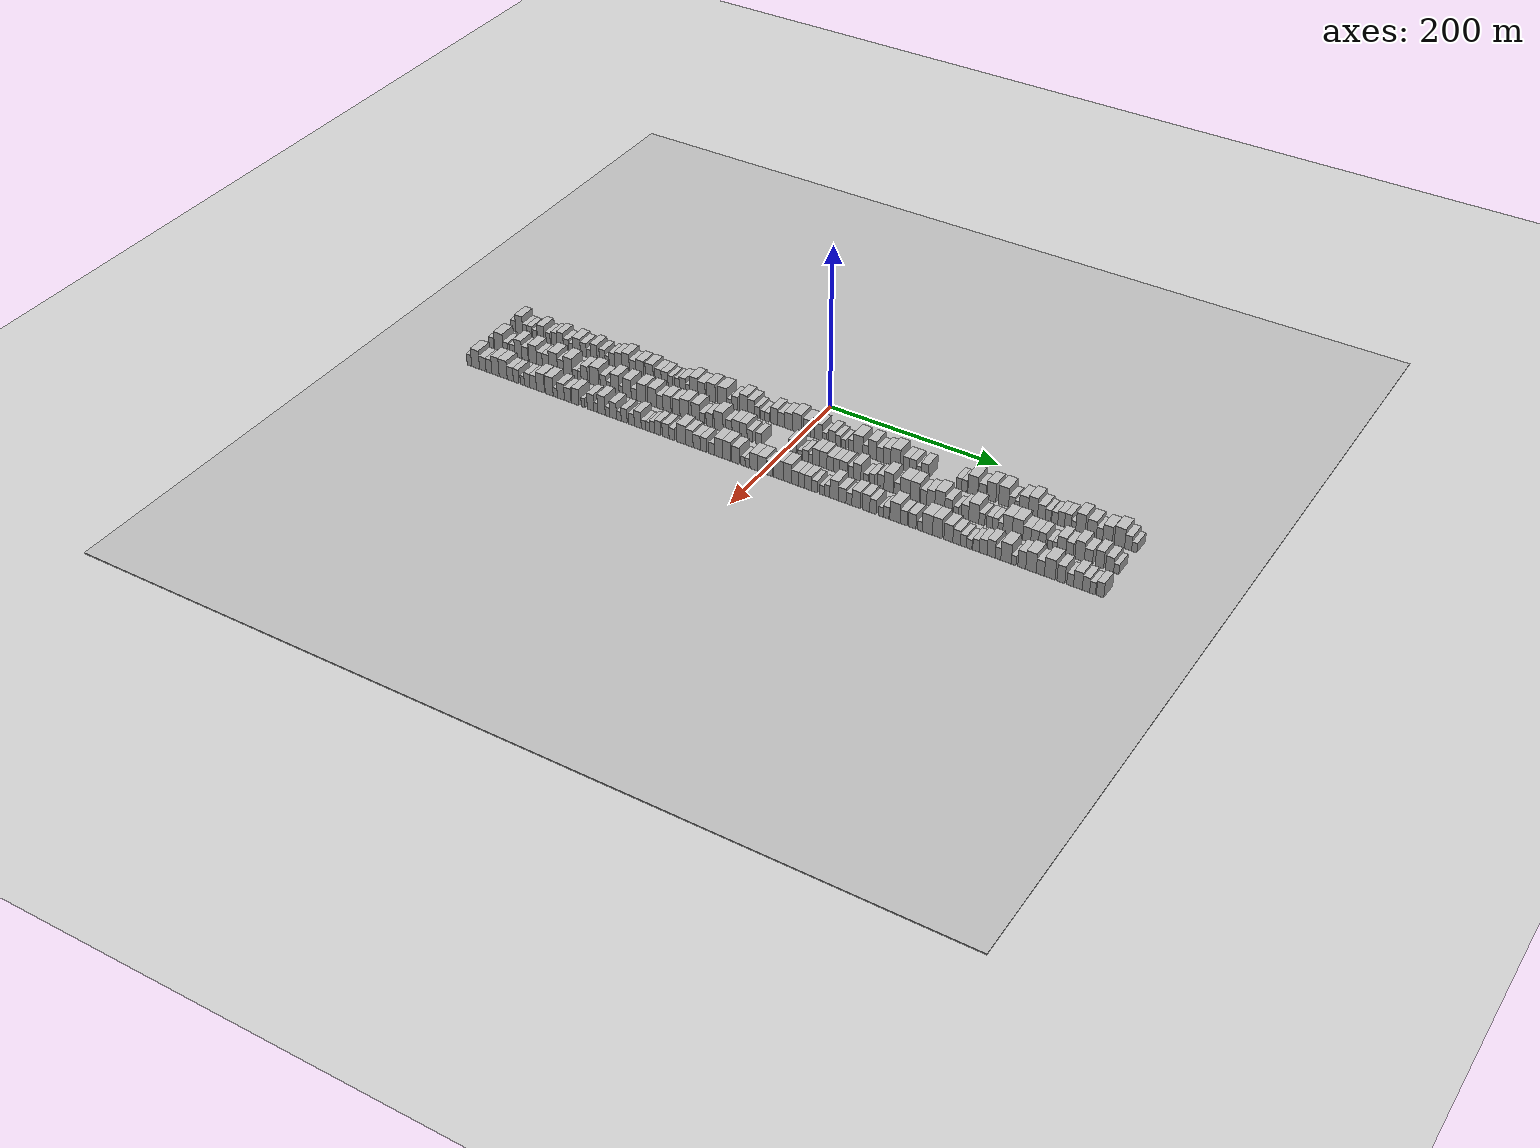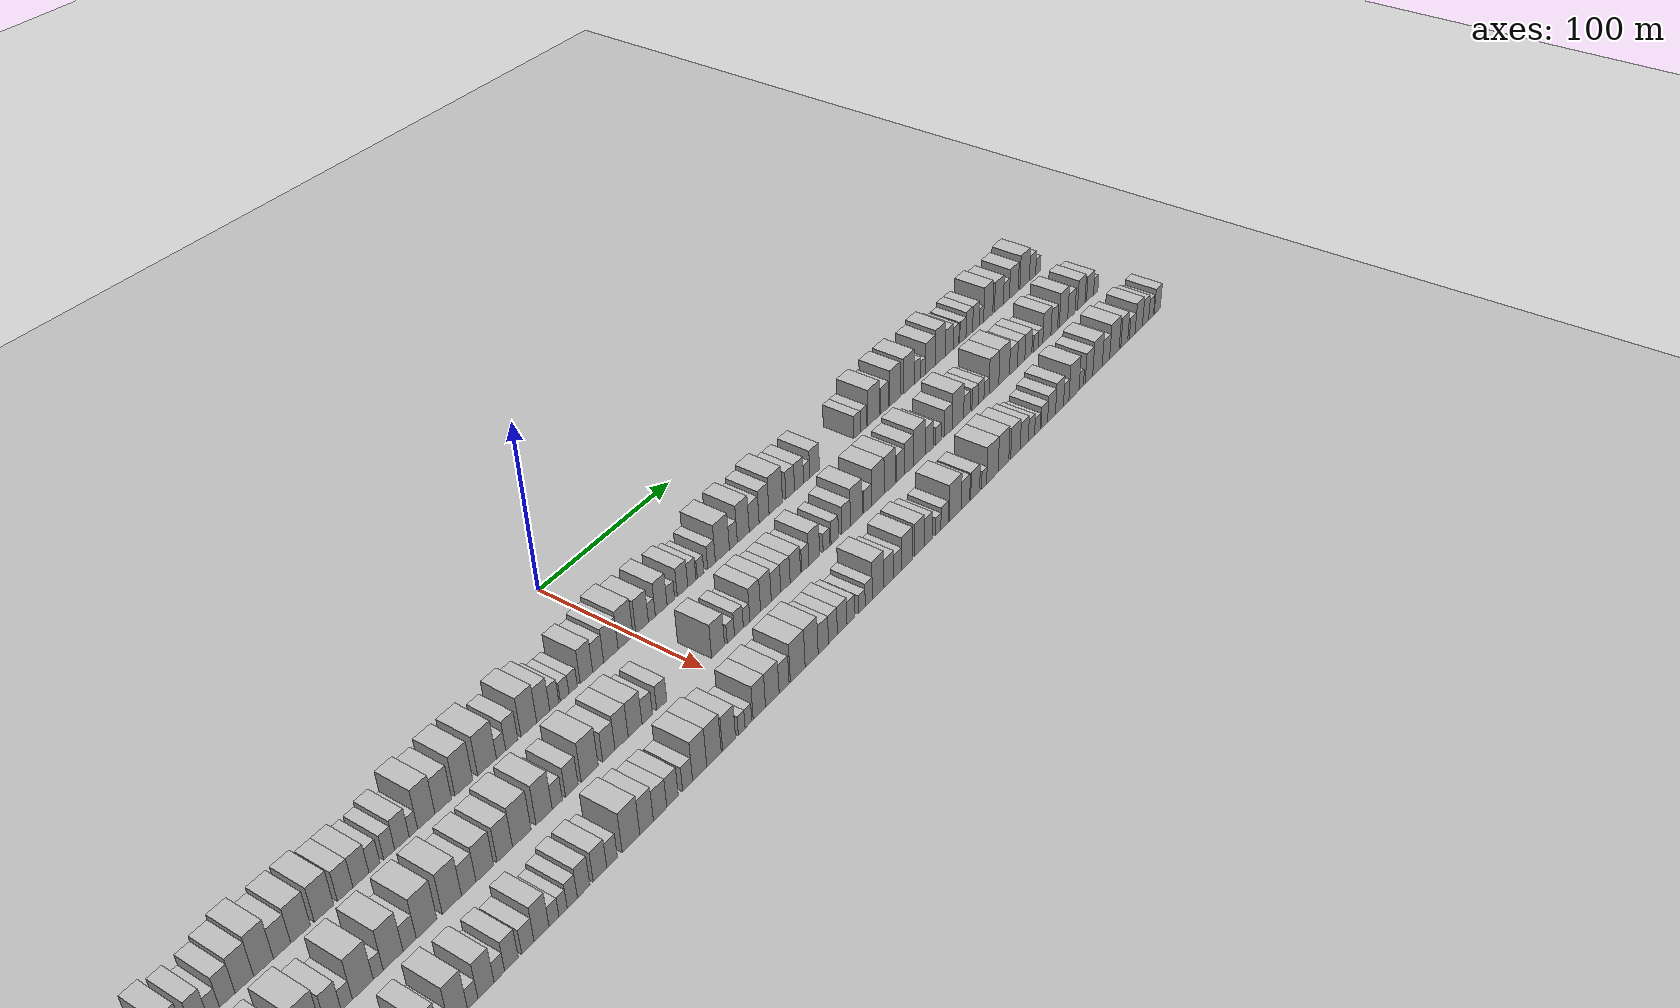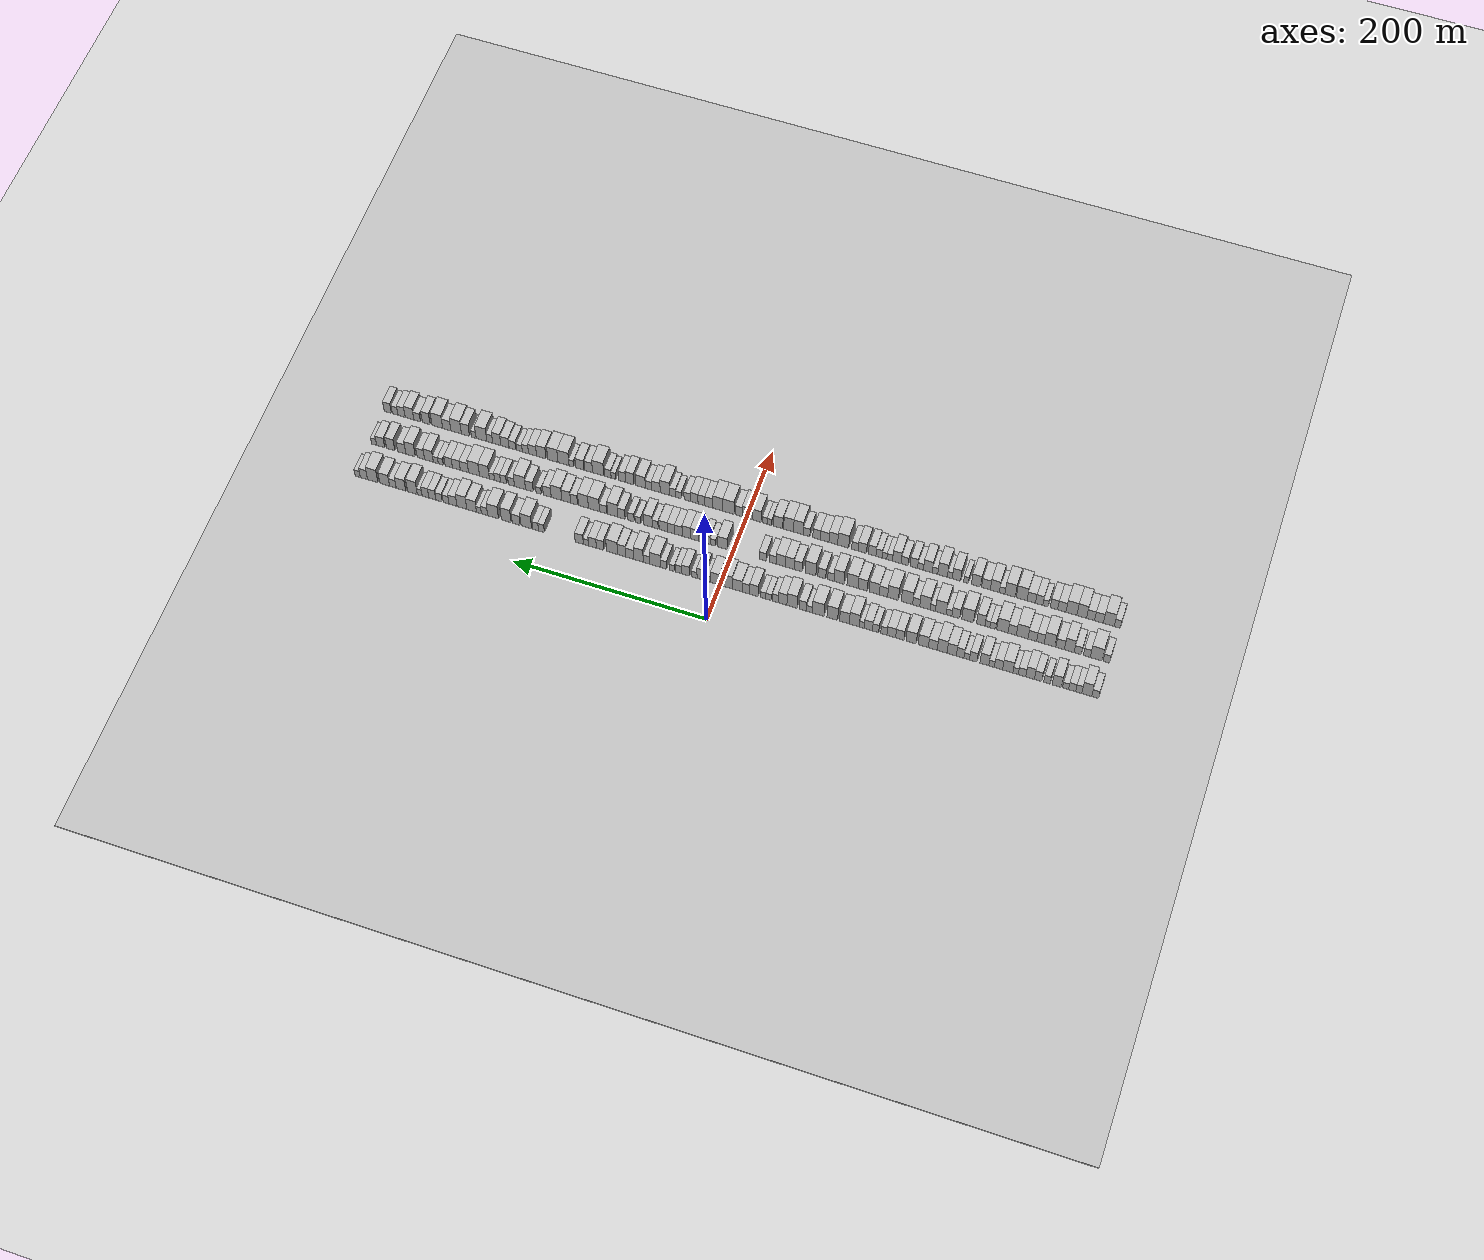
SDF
<?xml version="1.0" encoding="utf-8"?>

<sdf version="1.6">

   <world name="default">

      <gui fullscreen="0">

         <camera name="user_camera">

            <pose>-15 0 4.57585 0 0 0</pose>

            <view_controller>orbit</view_controller>

         </camera>

      </gui>

      <scene>

         <sky>

           <clouds>

             <speed>12</speed>

           </clouds>

         </sky>

         <ambient>0.4 0.4 0.4 1</ambient>

         <background>0.7 0.7 0.7 1</background>

         <shadows>1</shadows>

      </scene>

      <gravity>0 0 -9.8066</gravity>

      <magnetic_field>6e-06 2.3e-05 -4.2e-05</magnetic_field>

      <physics default="0" name="default_physics" type="ode">

         <ode>

            <solver>

               <type>quick</type>

               <iters>10</iters>

               <sor>1.0</sor>

               <use_dynamic_moi_rescaling>0</use_dynamic_moi_rescaling>

            </solver>

            <constraints>

               <cfm>0</cfm>

               <erp>0.2</erp>

               <contact_max_correcting_vel>100</contact_max_correcting_vel>

               <contact_surface_layer>0.001</contact_surface_layer>

            </constraints>

         </ode>

         <max_step_size>0.004</max_step_size>

         <real_time_factor>1</real_time_factor>

         <real_time_update_rate>250</real_time_update_rate>

      </physics>

      <light name="sun" type="directional">

         <cast_shadows>1</cast_shadows>

         <pose>0 0 10 0 0 0</pose>

         <diffuse>0.8 0.8 0.8 1</diffuse>

         <specular>0.2 0.2 0.2 1</specular>

         <attenuation>

            <range>1000</range>

            <constant>0.9</constant>

            <linear>0.01</linear>

            <quadratic>0.001</quadratic>

         </attenuation>

         <direction>-0.5 0.1 -0.9</direction>

      </light>

      <include>

         <name>ground_plane_1</name>

         <uri>model://HANNAS_ground_plane</uri>

         <pose>0 0 0  0 0 0</pose>

      </include>

      <include>

         <name>ground_plane_2</name>

         <uri>model://HANNAS_ground_plane</uri>

         <pose>100 0 0  0 0 0</pose>

      </include>

      <model name="building_1">

         <static>1</static>

         <pose frame="">50.0000 -376.5887 0 0.000000 0.000000 0.000000</pose>

         <link name="link">

            <pose frame="">0 0 7.50 0 0 0</pose>

            <collision name="collision">

               <geometry>

                  <box>

                     <size>20.0000 6.8225 15.0000</size>

                  </box>

               </geometry>

               <max_contacts>10</max_contacts>

               <surface>

                  <contact>

                     <ode/>

                  </contact>

                  <bounce/>

                  <friction>

                     <torsional>

                        <ode/>

                     </torsional>

                     <ode/>

                  </friction>

               </surface>

            </collision>

            <visual name="visual">

               <cast_shadows>0</cast_shadows>

               <geometry>

                  <box>

                     <size>20.0000 6.8225 15.0000</size>

                  </box>

               </geometry>

               <material>

                  <script>

                     <uri>model://HANNAS_wall/materials/scripts</uri>

                     <uri>model://HANNAS_wall/materials/textures</uri>

                     <name>vrc/HANNAS_wall</name>

                  </script>

               </material>

            </visual>

            <self_collide>0</self_collide>

            <enable_wind>0</enable_wind>

            <kinematic>0</kinematic>

         </link>

      </model>

      <model name="building_2">

         <static>1</static>

         <pose frame="">50.0000 -368.3572 0 0.000000 0.000000 0.000000</pose>

         <link name="link">

            <pose frame="">0 0 12.00 0 0 0</pose>

            <collision name="collision">

               <geometry>

                  <box>

                     <size>20.0000 9.6405 24.0000</size>

                  </box>

               </geometry>

               <max_contacts>10</max_contacts>

               <surface>

                  <contact>

                     <ode/>

                  </contact>

                  <bounce/>

                  <friction>

                     <torsional>

                        <ode/>

                     </torsional>

                     <ode/>

                  </friction>

               </surface>

            </collision>

            <visual name="visual">

               <cast_shadows>0</cast_shadows>

               <geometry>

                  <box>

                     <size>20.0000 9.6405 24.0000</size>

                  </box>

               </geometry>

               <material>

                  <script>

                     <uri>model://HANNAS_wall/materials/scripts</uri>

                     <uri>model://HANNAS_wall/materials/textures</uri>

                     <name>vrc/HANNAS_wall</name>

                  </script>

               </material>

            </visual>

            <self_collide>0</self_collide>

            <enable_wind>0</enable_wind>

            <kinematic>0</kinematic>

         </link>

      </model>

      <model name="building_3">

         <static>1</static>

         <pose frame="">50.0000 -360.4878 0 0.000000 0.000000 0.000000</pose>

         <link name="link">

            <pose frame="">0 0 7.50 0 0 0</pose>

            <collision name="collision">

               <geometry>

                  <box>

                     <size>20.0000 6.0983 15.0000</size>

                  </box>

               </geometry>

               <max_contacts>10</max_contacts>

               <surface>

                  <contact>

                     <ode/>

                  </contact>

                  <bounce/>

                  <friction>

                     <torsional>

                        <ode/>

                     </torsional>

                     <ode/>

                  </friction>

               </surface>

            </collision>

            <visual name="visual">

               <cast_shadows>0</cast_shadows>

               <geometry>

                  <box>

                     <size>20.0000 6.0983 15.0000</size>

                  </box>

               </geometry>

               <material>

                  <script>

                     <uri>model://HANNAS_wall/materials/scripts</uri>

                     <uri>model://HANNAS_wall/materials/textures</uri>

                     <name>vrc/HANNAS_wall</name>

                  </script>

               </material>

            </visual>

            <self_collide>0</self_collide>

            <enable_wind>0</enable_wind>

            <kinematic>0</kinematic>

         </link>

      </model>

      <model name="building_4">

         <static>1</static>

         <pose frame="">50.0000 -353.9359 0 0.000000 0.000000 0.000000</pose>

         <link name="link">

            <pose frame="">0 0 7.50 0 0 0</pose>

            <collision name="collision">

               <geometry>

                  <box>

                     <size>20.0000 7.0055 15.0000</size>

                  </box>

               </geometry>

               <max_contacts>10</max_contacts>

               <surface>

                  <contact>

                     <ode/>

                  </contact>

                  <bounce/>

                  <friction>

                     <torsional>

                        <ode/>

                     </torsional>

                     <ode/>

                  </friction>

               </surface>

            </collision>

            <visual name="visual">

               <cast_shadows>0</cast_shadows>

               <geometry>

                  <box>

                     <size>20.0000 7.0055 15.0000</size>

                  </box>

               </geometry>

               <material>

                  <script>

                     <uri>model://HANNAS_wall/materials/scripts</uri>

                     <uri>model://HANNAS_wall/materials/textures</uri>

                     <name>vrc/HANNAS_wall</name>

                  </script>

               </material>

            </visual>

            <self_collide>0</self_collide>

            <enable_wind>0</enable_wind>

            <kinematic>0</kinematic>

         </link>

      </model>

      <model name="building_5">

         <static>1</static>

         <pose frame="">50.0000 -347.4356 0 0.000000 0.000000 0.000000</pose>

         <link name="link">

            <pose frame="">0 0 6.00 0 0 0</pose>

            <collision name="collision">

               <geometry>

                  <box>

                     <size>20.0000 5.9953 12.0000</size>

                  </box>

               </geometry>

               <max_contacts>10</max_contacts>

               <surface>

                  <contact>

                     <ode/>

                  </contact>

                  <bounce/>

                  <friction>

                     <torsional>

                        <ode/>

                     </torsional>

                     <ode/>

                  </friction>

               </surface>

            </collision>

            <visual name="visual">

               <cast_shadows>0</cast_shadows>

               <geometry>

                  <box>

                     <size>20.0000 5.9953 12.0000</size>

                  </box>

               </geometry>

               <material>

                  <script>

                     <uri>model://HANNAS_wall/materials/scripts</uri>

                     <uri>model://HANNAS_wall/materials/textures</uri>

                     <name>vrc/HANNAS_wall</name>

                  </script>

               </material>

            </visual>

            <self_collide>0</self_collide>

            <enable_wind>0</enable_wind>

            <kinematic>0</kinematic>

         </link>

      </model>

      <model name="building_6">

         <static>1</static>

         <pose frame="">50.0000 -338.8548 0 0.000000 0.000000 0.000000</pose>

         <link name="link">

            <pose frame="">0 0 10.50 0 0 0</pose>

            <collision name="collision">

               <geometry>

                  <box>

                     <size>20.0000 9.1664 21.0000</size>

                  </box>

               </geometry>

               <max_contacts>10</max_contacts>

               <surface>

                  <contact>

                     <ode/>

                  </contact>

                  <bounce/>

                  <friction>

                     <torsional>

                        <ode/>

                     </torsional>

                     <ode/>

                  </friction>

               </surface>

            </collision>

            <visual name="visual">

               <cast_shadows>0</cast_shadows>

               <geometry>

                  <box>

                     <size>20.0000 9.1664 21.0000</size>

                  </box>

               </geometry>

               <material>

                  <script>

                     <uri>model://HANNAS_wall/materials/scripts</uri>

                     <uri>model://HANNAS_wall/materials/textures</uri>

                     <name>vrc/HANNAS_wall</name>

                  </script>

               </material>

            </visual>

            <self_collide>0</self_collide>

            <enable_wind>0</enable_wind>

            <kinematic>0</kinematic>

         </link>

      </model>

      <model name="building_7">

         <static>1</static>

         <pose frame="">50.0000 -329.1180 0 0.000000 0.000000 0.000000</pose>

         <link name="link">

            <pose frame="">0 0 7.50 0 0 0</pose>

            <collision name="collision">

               <geometry>

                  <box>

                     <size>20.0000 6.3071 15.0000</size>

                  </box>

               </geometry>

               <max_contacts>10</max_contacts>

               <surface>

                  <contact>

                     <ode/>

                  </contact>

                  <bounce/>

                  <friction>

                     <torsional>

                        <ode/>

                     </torsional>

                     <ode/>

                  </friction>

               </surface>

            </collision>

            <visual name="visual">

               <cast_shadows>0</cast_shadows>

               <geometry>

                  <box>

                     <size>20.0000 6.3071 15.0000</size>

                  </box>

               </geometry>

               <material>

                  <script>

                     <uri>model://HANNAS_wall/materials/scripts</uri>

                     <uri>model://HANNAS_wall/materials/textures</uri>

                     <name>vrc/HANNAS_wall</name>

                  </script>

               </material>

            </visual>

            <self_collide>0</self_collide>

            <enable_wind>0</enable_wind>

            <kinematic>0</kinematic>

         </link>

      </model>

      <model name="building_8">

         <static>1</static>

         <pose frame="">50.0000 -320.3116 0 0.000000 0.000000 0.000000</pose>

         <link name="link">

            <pose frame="">0 0 9.00 0 0 0</pose>

            <collision name="collision">

               <geometry>

                  <box>

                     <size>20.0000 7.3059 18.0000</size>

                  </box>

               </geometry>

               <max_contacts>10</max_contacts>

               <surface>

                  <contact>

                     <ode/>

                  </contact>

                  <bounce/>

                  <friction>

                     <torsional>

                        <ode/>

                     </torsional>

                     <ode/>

                  </friction>

               </surface>

            </collision>

            <visual name="visual">

               <cast_shadows>0</cast_shadows>

               <geometry>

                  <box>

                     <size>20.0000 7.3059 18.0000</size>

                  </box>

               </geometry>

               <material>

                  <script>

                     <uri>model://HANNAS_wall/materials/scripts</uri>

                     <uri>model://HANNAS_wall/materials/textures</uri>

                     <name>vrc/HANNAS_wall</name>

                  </script>

               </material>

            </visual>

            <self_collide>0</self_collide>

            <enable_wind>0</enable_wind>

            <kinematic>0</kinematic>

         </link>

      </model>

      <model name="building_9">

         <static>1</static>

         <pose frame="">50.0000 -312.3739 0 0.000000 0.000000 0.000000</pose>

         <link name="link">

            <pose frame="">0 0 10.50 0 0 0</pose>

            <collision name="collision">

               <geometry>

                  <box>

                     <size>20.0000 8.5694 21.0000</size>

                  </box>

               </geometry>

               <max_contacts>10</max_contacts>

               <surface>

                  <contact>

                     <ode/>

                  </contact>

                  <bounce/>

                  <friction>

                     <torsional>

                        <ode/>

                     </torsional>

                     <ode/>

                  </friction>

               </surface>

            </collision>

            <visual name="visual">

               <cast_shadows>0</cast_shadows>

               <geometry>

                  <box>

                     <size>20.0000 8.5694 21.0000</size>

                  </box>

               </geometry>

               <material>

                  <script>

                     <uri>model://HANNAS_wall/materials/scripts</uri>

                     <uri>model://HANNAS_wall/materials/textures</uri>

                     <name>vrc/HANNAS_wall</name>

                  </script>

               </material>

            </visual>

            <self_collide>0</self_collide>

            <enable_wind>0</enable_wind>

            <kinematic>0</kinematic>

         </link>

      </model>

      <model name="building_10">

         <static>1</static>

         <pose frame="">50.0000 -304.3528 0 0.000000 0.000000 0.000000</pose>

         <link name="link">

            <pose frame="">0 0 7.50 0 0 0</pose>

            <collision name="collision">

               <geometry>

                  <box>

                     <size>20.0000 7.4729 15.0000</size>

                  </box>

               </geometry>

               <max_contacts>10</max_contacts>

               <surface>

                  <contact>

                     <ode/>

                  </contact>

                  <bounce/>

                  <friction>

                     <torsional>

                        <ode/>

                     </torsional>

                     <ode/>

                  </friction>

               </surface>

            </collision>

            <visual name="visual">

               <cast_shadows>0</cast_shadows>

               <geometry>

                  <box>

                     <size>20.0000 7.4729 15.0000</size>

                  </box>

               </geometry>

               <material>

                  <script>

                     <uri>model://HANNAS_wall/materials/scripts</uri>

                     <uri>model://HANNAS_wall/materials/textures</uri>

                     <name>vrc/HANNAS_wall</name>

                  </script>

               </material>

            </visual>

            <self_collide>0</self_collide>

            <enable_wind>0</enable_wind>

            <kinematic>0</kinematic>

         </link>

      </model>

      <model name="building_11">

         <static>1</static>

         <pose frame="">50.0000 -298.0110 0 0.000000 0.000000 0.000000</pose>

         <link name="link">

            <pose frame="">0 0 6.00 0 0 0</pose>

            <collision name="collision">

               <geometry>

                  <box>

                     <size>20.0000 5.2107 12.0000</size>

                  </box>

               </geometry>

               <max_contacts>10</max_contacts>

               <surface>

                  <contact>

                     <ode/>

                  </contact>

                  <bounce/>

                  <friction>

                     <torsional>

                        <ode/>

                     </torsional>

                     <ode/>

                  </friction>

               </surface>

            </collision>

            <visual name="visual">

               <cast_shadows>0</cast_shadows>

               <geometry>

                  <box>

                     <size>20.0000 5.2107 12.0000</size>

                  </box>

               </geometry>

               <material>

                  <script>

                     <uri>model://HANNAS_wall/materials/scripts</uri>

                     <uri>model://HANNAS_wall/materials/textures</uri>

                     <name>vrc/HANNAS_wall</name>

                  </script>

               </material>

            </visual>

            <self_collide>0</self_collide>

            <enable_wind>0</enable_wind>

            <kinematic>0</kinematic>

         </link>

      </model>

      <model name="building_12">

         <static>1</static>

         <pose frame="">50.0000 -290.2466 0 0.000000 0.000000 0.000000</pose>

         <link name="link">

            <pose frame="">0 0 10.50 0 0 0</pose>

            <collision name="collision">

               <geometry>

                  <box>

                     <size>20.0000 10.3182 21.0000</size>

                  </box>

               </geometry>

               <max_contacts>10</max_contacts>

               <surface>

                  <contact>

                     <ode/>

                  </contact>

                  <bounce/>

                  <friction>

                     <torsional>

                        <ode/>

                     </torsional>

                     <ode/>

                  </friction>

               </surface>

            </collision>

            <visual name="visual">

               <cast_shadows>0</cast_shadows>

               <geometry>

                  <box>

                     <size>20.0000 10.3182 21.0000</size>

                  </box>

               </geometry>

               <material>

                  <script>

                     <uri>model://HANNAS_wall/materials/scripts</uri>

                     <uri>model://HANNAS_wall/materials/textures</uri>

                     <name>vrc/HANNAS_wall</name>

                  </script>

               </material>

            </visual>

            <self_collide>0</self_collide>

            <enable_wind>0</enable_wind>

            <kinematic>0</kinematic>

         </link>

      </model>

      <model name="building_13">

         <static>1</static>

         <pose frame="">50.0000 -281.0567 0 0.000000 0.000000 0.000000</pose>

         <link name="link">

            <pose frame="">0 0 9.00 0 0 0</pose>

            <collision name="collision">

               <geometry>

                  <box>

                     <size>20.0000 8.0616 18.0000</size>

                  </box>

               </geometry>

               <max_contacts>10</max_contacts>

               <surface>

                  <contact>

                     <ode/>

                  </contact>

                  <bounce/>

                  <friction>

                     <torsional>

                        <ode/>

                     </torsional>

                     <ode/>

                  </friction>

               </surface>

            </collision>

            <visual name="visual">

               <cast_shadows>0</cast_shadows>

               <geometry>

                  <box>

                     <size>20.0000 8.0616 18.0000</size>

                  </box>

               </geometry>

               <material>

                  <script>

                     <uri>model://HANNAS_wall/materials/scripts</uri>

                     <uri>model://HANNAS_wall/materials/textures</uri>

                     <name>vrc/HANNAS_wall</name>

                  </script>

               </material>

            </visual>

            <self_collide>0</self_collide>

            <enable_wind>0</enable_wind>

            <kinematic>0</kinematic>

         </link>

      </model>

      <model name="building_14">

         <static>1</static>

         <pose frame="">50.0000 -274.2364 0 0.000000 0.000000 0.000000</pose>

         <link name="link">

            <pose frame="">0 0 6.00 0 0 0</pose>

            <collision name="collision">

               <geometry>

                  <box>

                     <size>20.0000 5.5790 12.0000</size>

                  </box>

               </geometry>

               <max_contacts>10</max_contacts>

               <surface>

                  <contact>

                     <ode/>

                  </contact>

                  <bounce/>

                  <friction>

                     <torsional>

                        <ode/>

                     </torsional>

                     <ode/>

                  </friction>

               </surface>

            </collision>

            <visual name="visual">

               <cast_shadows>0</cast_shadows>

               <geometry>

                  <box>

                     <size>20.0000 5.5790 12.0000</size>

                  </box>

               </geometry>

               <material>

                  <script>

                     <uri>model://HANNAS_wall/materials/scripts</uri>

                     <uri>model://HANNAS_wall/materials/textures</uri>

                     <name>vrc/HANNAS_wall</name>

                  </script>

               </material>

            </visual>

            <self_collide>0</self_collide>

            <enable_wind>0</enable_wind>

            <kinematic>0</kinematic>

         </link>

      </model>

      <model name="building_15">

         <static>1</static>

         <pose frame="">50.0000 -267.0458 0 0.000000 0.000000 0.000000</pose>

         <link name="link">

            <pose frame="">0 0 10.50 0 0 0</pose>

            <collision name="collision">

               <geometry>

                  <box>

                     <size>20.0000 8.8021 21.0000</size>

                  </box>

               </geometry>

               <max_contacts>10</max_contacts>

               <surface>

                  <contact>

                     <ode/>

                  </contact>

                  <bounce/>

                  <friction>

                     <torsional>

                        <ode/>

                     </torsional>

                     <ode/>

                  </friction>

               </surface>

            </collision>

            <visual name="visual">

               <cast_shadows>0</cast_shadows>

               <geometry>

                  <box>

                     <size>20.0000 8.8021 21.0000</size>

                  </box>

               </geometry>

               <material>

                  <script>

                     <uri>model://HANNAS_wall/materials/scripts</uri>

                     <uri>model://HANNAS_wall/materials/textures</uri>

                     <name>vrc/HANNAS_wall</name>

                  </script>

               </material>

            </visual>

            <self_collide>0</self_collide>

            <enable_wind>0</enable_wind>

            <kinematic>0</kinematic>

         </link>

      </model>

      <model name="building_16">

         <static>1</static>

         <pose frame="">50.0000 -255.9481 0 0.000000 0.000000 0.000000</pose>

         <link name="link">

            <pose frame="">0 0 9.00 0 0 0</pose>

            <collision name="collision">

               <geometry>

                  <box>

                     <size>20.0000 7.3935 18.0000</size>

                  </box>

               </geometry>

               <max_contacts>10</max_contacts>

               <surface>

                  <contact>

                     <ode/>

                  </contact>

                  <bounce/>

                  <friction>

                     <torsional>

                        <ode/>

                     </torsional>

                     <ode/>

                  </friction>

               </surface>

            </collision>

            <visual name="visual">

               <cast_shadows>0</cast_shadows>

               <geometry>

                  <box>

                     <size>20.0000 7.3935 18.0000</size>

                  </box>

               </geometry>

               <material>

                  <script>

                     <uri>model://HANNAS_wall/materials/scripts</uri>

                     <uri>model://HANNAS_wall/materials/textures</uri>

                     <name>vrc/HANNAS_wall</name>

                  </script>

               </material>

            </visual>

            <self_collide>0</self_collide>

            <enable_wind>0</enable_wind>

            <kinematic>0</kinematic>

         </link>

      </model>

      <model name="building_17">

         <static>1</static>

         <pose frame="">50.0000 -249.4596 0 0.000000 0.000000 0.000000</pose>

         <link name="link">

            <pose frame="">0 0 6.00 0 0 0</pose>

            <collision name="collision">

               <geometry>

                  <box>

                     <size>20.0000 5.5834 12.0000</size>

                  </box>

               </geometry>

               <max_contacts>10</max_contacts>

               <surface>

                  <contact>

                     <ode/>

                  </contact>

                  <bounce/>

                  <friction>

                     <torsional>

                        <ode/>

                     </torsional>

                     <ode/>

                  </friction>

               </surface>

            </collision>

            <visual name="visual">

               <cast_shadows>0</cast_shadows>

               <geometry>

                  <box>

                     <size>20.0000 5.5834 12.0000</size>

                  </box>

               </geometry>

               <material>

                  <script>

                     <uri>model://HANNAS_wall/materials/scripts</uri>

                     <uri>model://HANNAS_wall/materials/textures</uri>

                     <name>vrc/HANNAS_wall</name>

                  </script>

               </material>

            </visual>

            <self_collide>0</self_collide>

            <enable_wind>0</enable_wind>

            <kinematic>0</kinematic>

         </link>

      </model>

      <model name="building_18">

         <static>1</static>

         <pose frame="">50.0000 -242.8671 0 0.000000 0.000000 0.000000</pose>

         <link name="link">

            <pose frame="">0 0 9.00 0 0 0</pose>

            <collision name="collision">

               <geometry>

                  <box>

                     <size>20.0000 7.6015 18.0000</size>

                  </box>

               </geometry>

               <max_contacts>10</max_contacts>

               <surface>

                  <contact>

                     <ode/>

                  </contact>

                  <bounce/>

                  <friction>

                     <torsional>

                        <ode/>

                     </torsional>

                     <ode/>

                  </friction>

               </surface>

            </collision>

            <visual name="visual">

               <cast_shadows>0</cast_shadows>

               <geometry>

                  <box>

                     <size>20.0000 7.6015 18.0000</size>

                  </box>

               </geometry>

               <material>

                  <script>

                     <uri>model://HANNAS_wall/materials/scripts</uri>

                     <uri>model://HANNAS_wall/materials/textures</uri>

                     <name>vrc/HANNAS_wall</name>

                  </script>

               </material>

            </visual>

            <self_collide>0</self_collide>

            <enable_wind>0</enable_wind>

            <kinematic>0</kinematic>

         </link>

      </model>

      <model name="building_19">

         <static>1</static>

         <pose frame="">50.0000 -234.4478 0 0.000000 0.000000 0.000000</pose>

         <link name="link">

            <pose frame="">0 0 10.50 0 0 0</pose>

            <collision name="collision">

               <geometry>

                  <box>

                     <size>20.0000 9.2371 21.0000</size>

                  </box>

               </geometry>

               <max_contacts>10</max_contacts>

               <surface>

                  <contact>

                     <ode/>

                  </contact>

                  <bounce/>

                  <friction>

                     <torsional>

                        <ode/>

                     </torsional>

                     <ode/>

                  </friction>

               </surface>

            </collision>

            <visual name="visual">

               <cast_shadows>0</cast_shadows>

               <geometry>

                  <box>

                     <size>20.0000 9.2371 21.0000</size>

                  </box>

               </geometry>

               <material>

                  <script>

                     <uri>model://HANNAS_wall/materials/scripts</uri>

                     <uri>model://HANNAS_wall/materials/textures</uri>

                     <name>vrc/HANNAS_wall</name>

                  </script>

               </material>

            </visual>

            <self_collide>0</self_collide>

            <enable_wind>0</enable_wind>

            <kinematic>0</kinematic>

         </link>

      </model>

      <model name="building_20">

         <static>1</static>

         <pose frame="">50.0000 -224.8944 0 0.000000 0.000000 0.000000</pose>

         <link name="link">

            <pose frame="">0 0 12.00 0 0 0</pose>

            <collision name="collision">

               <geometry>

                  <box>

                     <size>20.0000 9.8696 24.0000</size>

                  </box>

               </geometry>

               <max_contacts>10</max_contacts>

               <surface>

                  <contact>

                     <ode/>

                  </contact>

                  <bounce/>

                  <friction>

                     <torsional>

                        <ode/>

                     </torsional>

                     <ode/>

                  </friction>

               </surface>

            </collision>

            <visual name="visual">

               <cast_shadows>0</cast_shadows>

               <geometry>

                  <box>

                     <size>20.0000 9.8696 24.0000</size>

                  </box>

               </geometry>

               <material>

                  <script>

                     <uri>model://HANNAS_wall/materials/scripts</uri>

                     <uri>model://HANNAS_wall/materials/textures</uri>

                     <name>vrc/HANNAS_wall</name>

                  </script>

               </material>

            </visual>

            <self_collide>0</self_collide>

            <enable_wind>0</enable_wind>

            <kinematic>0</kinematic>

         </link>

      </model>

      <model name="building_21">

         <static>1</static>

         <pose frame="">50.0000 -215.5552 0 0.000000 0.000000 0.000000</pose>

         <link name="link">

            <pose frame="">0 0 9.00 0 0 0</pose>

            <collision name="collision">

               <geometry>

                  <box>

                     <size>20.0000 8.8090 18.0000</size>

                  </box>

               </geometry>

               <max_contacts>10</max_contacts>

               <surface>

                  <contact>

                     <ode/>

                  </contact>

                  <bounce/>

                  <friction>

                     <torsional>

                        <ode/>

                     </torsional>

                     <ode/>

                  </friction>

               </surface>

            </collision>

            <visual name="visual">

               <cast_shadows>0</cast_shadows>

               <geometry>

                  <box>

                     <size>20.0000 8.8090 18.0000</size>

                  </box>

               </geometry>

               <material>

                  <script>

                     <uri>model://HANNAS_wall/materials/scripts</uri>

                     <uri>model://HANNAS_wall/materials/textures</uri>

                     <name>vrc/HANNAS_wall</name>

                  </script>

               </material>

            </visual>

            <self_collide>0</self_collide>

            <enable_wind>0</enable_wind>

            <kinematic>0</kinematic>

         </link>

      </model>

      <model name="building_22">

         <static>1</static>

         <pose frame="">50.0000 -206.0367 0 0.000000 0.000000 0.000000</pose>

         <link name="link">

            <pose frame="">0 0 10.50 0 0 0</pose>

            <collision name="collision">

               <geometry>

                  <box>

                     <size>20.0000 10.2279 21.0000</size>

                  </box>

               </geometry>

               <max_contacts>10</max_contacts>

               <surface>

                  <contact>

                     <ode/>

                  </contact>

                  <bounce/>

                  <friction>

                     <torsional>

                        <ode/>

                     </torsional>

                     <ode/>

                  </friction>

               </surface>

            </collision>

            <visual name="visual">

               <cast_shadows>0</cast_shadows>

               <geometry>

                  <box>

                     <size>20.0000 10.2279 21.0000</size>

                  </box>

               </geometry>

               <material>

                  <script>

                     <uri>model://HANNAS_wall/materials/scripts</uri>

                     <uri>model://HANNAS_wall/materials/textures</uri>

                     <name>vrc/HANNAS_wall</name>

                  </script>

               </material>

            </visual>

            <self_collide>0</self_collide>

            <enable_wind>0</enable_wind>

            <kinematic>0</kinematic>

         </link>

      </model>

      <model name="building_23">

         <static>1</static>

         <pose frame="">50.0000 -193.7813 0 0.000000 0.000000 0.000000</pose>

         <link name="link">

            <pose frame="">0 0 10.50 0 0 0</pose>

            <collision name="collision">

               <geometry>

                  <box>

                     <size>20.0000 10.2829 21.0000</size>

                  </box>

               </geometry>

               <max_contacts>10</max_contacts>

               <surface>

                  <contact>

                     <ode/>

                  </contact>

                  <bounce/>

                  <friction>

                     <torsional>

                        <ode/>

                     </torsional>

                     <ode/>

                  </friction>

               </surface>

            </collision>

            <visual name="visual">

               <cast_shadows>0</cast_shadows>

               <geometry>

                  <box>

                     <size>20.0000 10.2829 21.0000</size>

                  </box>

               </geometry>

               <material>

                  <script>

                     <uri>model://HANNAS_wall/materials/scripts</uri>

                     <uri>model://HANNAS_wall/materials/textures</uri>

                     <name>vrc/HANNAS_wall</name>

                  </script>

               </material>

            </visual>

            <self_collide>0</self_collide>

            <enable_wind>0</enable_wind>

            <kinematic>0</kinematic>

         </link>

      </model>

      <model name="building_24">

         <static>1</static>

         <pose frame="">50.0000 -182.4330 0 0.000000 0.000000 0.000000</pose>

         <link name="link">

            <pose frame="">0 0 9.00 0 0 0</pose>

            <collision name="collision">

               <geometry>

                  <box>

                     <size>20.0000 8.4136 18.0000</size>

                  </box>

               </geometry>

               <max_contacts>10</max_contacts>

               <surface>

                  <contact>

                     <ode/>

                  </contact>

                  <bounce/>

                  <friction>

                     <torsional>

                        <ode/>

                     </torsional>

                     <ode/>

                  </friction>

               </surface>

            </collision>

            <visual name="visual">

               <cast_shadows>0</cast_shadows>

               <geometry>

                  <box>

                     <size>20.0000 8.4136 18.0000</size>

                  </box>

               </geometry>

               <material>

                  <script>

                     <uri>model://HANNAS_wall/materials/scripts</uri>

                     <uri>model://HANNAS_wall/materials/textures</uri>

                     <name>vrc/HANNAS_wall</name>

                  </script>

               </material>

            </visual>

            <self_collide>0</self_collide>

            <enable_wind>0</enable_wind>

            <kinematic>0</kinematic>

         </link>

      </model>

      <model name="building_25">

         <static>1</static>

         <pose frame="">50.0000 -173.8263 0 0.000000 0.000000 0.000000</pose>

         <link name="link">

            <pose frame="">0 0 9.00 0 0 0</pose>

            <collision name="collision">

               <geometry>

                  <box>

                     <size>20.0000 8.7998 18.0000</size>

                  </box>

               </geometry>

               <max_contacts>10</max_contacts>

               <surface>

                  <contact>

                     <ode/>

                  </contact>

                  <bounce/>

                  <friction>

                     <torsional>

                        <ode/>

                     </torsional>

                     <ode/>

                  </friction>

               </surface>

            </collision>

            <visual name="visual">

               <cast_shadows>0</cast_shadows>

               <geometry>

                  <box>

                     <size>20.0000 8.7998 18.0000</size>

                  </box>

               </geometry>

               <material>

                  <script>

                     <uri>model://HANNAS_wall/materials/scripts</uri>

                     <uri>model://HANNAS_wall/materials/textures</uri>

                     <name>vrc/HANNAS_wall</name>

                  </script>

               </material>

            </visual>

            <self_collide>0</self_collide>

            <enable_wind>0</enable_wind>

            <kinematic>0</kinematic>

         </link>

      </model>

      <model name="building_26">

         <static>1</static>

         <pose frame="">50.0000 -166.3230 0 0.000000 0.000000 0.000000</pose>

         <link name="link">

            <pose frame="">0 0 7.50 0 0 0</pose>

            <collision name="collision">

               <geometry>

                  <box>

                     <size>20.0000 6.2067 15.0000</size>

                  </box>

               </geometry>

               <max_contacts>10</max_contacts>

               <surface>

                  <contact>

                     <ode/>

                  </contact>

                  <bounce/>

                  <friction>

                     <torsional>

                        <ode/>

                     </torsional>

                     <ode/>

                  </friction>

               </surface>

            </collision>

            <visual name="visual">

               <cast_shadows>0</cast_shadows>

               <geometry>

                  <box>

                     <size>20.0000 6.2067 15.0000</size>

                  </box>

               </geometry>

               <material>

                  <script>

                     <uri>model://HANNAS_wall/materials/scripts</uri>

                     <uri>model://HANNAS_wall/materials/textures</uri>

                     <name>vrc/HANNAS_wall</name>

                  </script>

               </material>

            </visual>

            <self_collide>0</self_collide>

            <enable_wind>0</enable_wind>

            <kinematic>0</kinematic>

         </link>

      </model>

      <model name="building_27">

         <static>1</static>

         <pose frame="">50.0000 -158.0686 0 0.000000 0.000000 0.000000</pose>

         <link name="link">

            <pose frame="">0 0 7.50 0 0 0</pose>

            <collision name="collision">

               <geometry>

                  <box>

                     <size>20.0000 6.3021 15.0000</size>

                  </box>

               </geometry>

               <max_contacts>10</max_contacts>

               <surface>

                  <contact>

                     <ode/>

                  </contact>

                  <bounce/>

                  <friction>

                     <torsional>

                        <ode/>

                     </torsional>

                     <ode/>

                  </friction>

               </surface>

            </collision>

            <visual name="visual">

               <cast_shadows>0</cast_shadows>

               <geometry>

                  <box>

                     <size>20.0000 6.3021 15.0000</size>

                  </box>

               </geometry>

               <material>

                  <script>

                     <uri>model://HANNAS_wall/materials/scripts</uri>

                     <uri>model://HANNAS_wall/materials/textures</uri>

                     <name>vrc/HANNAS_wall</name>

                  </script>

               </material>

            </visual>

            <self_collide>0</self_collide>

            <enable_wind>0</enable_wind>

            <kinematic>0</kinematic>

         </link>

      </model>

      <model name="building_28">

         <static>1</static>

         <pose frame="">50.0000 -150.7782 0 0.000000 0.000000 0.000000</pose>

         <link name="link">

            <pose frame="">0 0 9.00 0 0 0</pose>

            <collision name="collision">

               <geometry>

                  <box>

                     <size>20.0000 8.2787 18.0000</size>

                  </box>

               </geometry>

               <max_contacts>10</max_contacts>

               <surface>

                  <contact>

                     <ode/>

                  </contact>

                  <bounce/>

                  <friction>

                     <torsional>

                        <ode/>

                     </torsional>

                     <ode/>

                  </friction>

               </surface>

            </collision>

            <visual name="visual">

               <cast_shadows>0</cast_shadows>

               <geometry>

                  <box>

                     <size>20.0000 8.2787 18.0000</size>

                  </box>

               </geometry>

               <material>

                  <script>

                     <uri>model://HANNAS_wall/materials/scripts</uri>

                     <uri>model://HANNAS_wall/materials/textures</uri>

                     <name>vrc/HANNAS_wall</name>

                  </script>

               </material>

            </visual>

            <self_collide>0</self_collide>

            <enable_wind>0</enable_wind>

            <kinematic>0</kinematic>

         </link>

      </model>

      <model name="building_29">

         <static>1</static>

         <pose frame="">50.0000 -144.1858 0 0.000000 0.000000 0.000000</pose>

         <link name="link">

            <pose frame="">0 0 6.00 0 0 0</pose>

            <collision name="collision">

               <geometry>

                  <box>

                     <size>20.0000 4.9062 12.0000</size>

                  </box>

               </geometry>

               <max_contacts>10</max_contacts>

               <surface>

                  <contact>

                     <ode/>

                  </contact>

                  <bounce/>

                  <friction>

                     <torsional>

                        <ode/>

                     </torsional>

                     <ode/>

                  </friction>

               </surface>

            </collision>

            <visual name="visual">

               <cast_shadows>0</cast_shadows>

               <geometry>

                  <box>

                     <size>20.0000 4.9062 12.0000</size>

                  </box>

               </geometry>

               <material>

                  <script>

                     <uri>model://HANNAS_wall/materials/scripts</uri>

                     <uri>model://HANNAS_wall/materials/textures</uri>

                     <name>vrc/HANNAS_wall</name>

                  </script>

               </material>

            </visual>

            <self_collide>0</self_collide>

            <enable_wind>0</enable_wind>

            <kinematic>0</kinematic>

         </link>

      </model>

      <model name="building_30">

         <static>1</static>

         <pose frame="">50.0000 -136.6641 0 0.000000 0.000000 0.000000</pose>

         <link name="link">

            <pose frame="">0 0 12.00 0 0 0</pose>

            <collision name="collision">

               <geometry>

                  <box>

                     <size>20.0000 10.1371 24.0000</size>

                  </box>

               </geometry>

               <max_contacts>10</max_contacts>

               <surface>

                  <contact>

                     <ode/>

                  </contact>

                  <bounce/>

                  <friction>

                     <torsional>

                        <ode/>

                     </torsional>

                     <ode/>

                  </friction>

               </surface>

            </collision>

            <visual name="visual">

               <cast_shadows>0</cast_shadows>

               <geometry>

                  <box>

                     <size>20.0000 10.1371 24.0000</size>

                  </box>

               </geometry>

               <material>

                  <script>

                     <uri>model://HANNAS_wall/materials/scripts</uri>

                     <uri>model://HANNAS_wall/materials/textures</uri>

                     <name>vrc/HANNAS_wall</name>

                  </script>

               </material>

            </visual>

            <self_collide>0</self_collide>

            <enable_wind>0</enable_wind>

            <kinematic>0</kinematic>

         </link>

      </model>

      <model name="building_31">

         <static>1</static>

         <pose frame="">50.0000 -126.6394 0 0.000000 0.000000 0.000000</pose>

         <link name="link">

            <pose frame="">0 0 10.50 0 0 0</pose>

            <collision name="collision">

               <geometry>

                  <box>

                     <size>20.0000 9.9122 21.0000</size>

                  </box>

               </geometry>

               <max_contacts>10</max_contacts>

               <surface>

                  <contact>

                     <ode/>

                  </contact>

                  <bounce/>

                  <friction>

                     <torsional>

                        <ode/>

                     </torsional>

                     <ode/>

                  </friction>

               </surface>

            </collision>

            <visual name="visual">

               <cast_shadows>0</cast_shadows>

               <geometry>

                  <box>

                     <size>20.0000 9.9122 21.0000</size>

                  </box>

               </geometry>

               <material>

                  <script>

                     <uri>model://HANNAS_wall/materials/scripts</uri>

                     <uri>model://HANNAS_wall/materials/textures</uri>

                     <name>vrc/HANNAS_wall</name>

                  </script>

               </material>

            </visual>

            <self_collide>0</self_collide>

            <enable_wind>0</enable_wind>

            <kinematic>0</kinematic>

         </link>

      </model>

      <model name="building_32">

         <static>1</static>

         <pose frame="">50.0000 -114.2487 0 0.000000 0.000000 0.000000</pose>

         <link name="link">

            <pose frame="">0 0 12.00 0 0 0</pose>

            <collision name="collision">

               <geometry>

                  <box>

                     <size>20.0000 10.8692 24.0000</size>

                  </box>

               </geometry>

               <max_contacts>10</max_contacts>

               <surface>

                  <contact>

                     <ode/>

                  </contact>

                  <bounce/>

                  <friction>

                     <torsional>

                        <ode/>

                     </torsional>

                     <ode/>

                  </friction>

               </surface>

            </collision>

            <visual name="visual">

               <cast_shadows>0</cast_shadows>

               <geometry>

                  <box>

                     <size>20.0000 10.8692 24.0000</size>

                  </box>

               </geometry>

               <material>

                  <script>

                     <uri>model://HANNAS_wall/materials/scripts</uri>

                     <uri>model://HANNAS_wall/materials/textures</uri>

                     <name>vrc/HANNAS_wall</name>

                  </script>

               </material>

            </visual>

            <self_collide>0</self_collide>

            <enable_wind>0</enable_wind>

            <kinematic>0</kinematic>

         </link>

      </model>

      <model name="building_33">

         <static>1</static>

         <pose frame="">50.0000 -99.9385 0 0.000000 0.000000 0.000000</pose>

         <link name="link">

            <pose frame="">0 0 12.00 0 0 0</pose>

            <collision name="collision">

               <geometry>

                  <box>

                     <size>20.0000 11.7513 24.0000</size>

                  </box>

               </geometry>

               <max_contacts>10</max_contacts>

               <surface>

                  <contact>

                     <ode/>

                  </contact>

                  <bounce/>

                  <friction>

                     <torsional>

                        <ode/>

                     </torsional>

                     <ode/>

                  </friction>

               </surface>

            </collision>

            <visual name="visual">

               <cast_shadows>0</cast_shadows>

               <geometry>

                  <box>

                     <size>20.0000 11.7513 24.0000</size>

                  </box>

               </geometry>

               <material>

                  <script>

                     <uri>model://HANNAS_wall/materials/scripts</uri>

                     <uri>model://HANNAS_wall/materials/textures</uri>

                     <name>vrc/HANNAS_wall</name>

                  </script>

               </material>

            </visual>

            <self_collide>0</self_collide>

            <enable_wind>0</enable_wind>

            <kinematic>0</kinematic>

         </link>

      </model>

      <model name="building_34">

         <static>1</static>

         <pose frame="">50.0000 -91.1195 0 0.000000 0.000000 0.000000</pose>

         <link name="link">

            <pose frame="">0 0 6.00 0 0 0</pose>

            <collision name="collision">

               <geometry>

                  <box>

                     <size>20.0000 5.8866 12.0000</size>

                  </box>

               </geometry>

               <max_contacts>10</max_contacts>

               <surface>

                  <contact>

                     <ode/>

                  </contact>

                  <bounce/>

                  <friction>

                     <torsional>

                        <ode/>

                     </torsional>

                     <ode/>

                  </friction>

               </surface>

            </collision>

            <visual name="visual">

               <cast_shadows>0</cast_shadows>

               <geometry>

                  <box>

                     <size>20.0000 5.8866 12.0000</size>

                  </box>

               </geometry>

               <material>

                  <script>

                     <uri>model://HANNAS_wall/materials/scripts</uri>

                     <uri>model://HANNAS_wall/materials/textures</uri>

                     <name>vrc/HANNAS_wall</name>

                  </script>

               </material>

            </visual>

            <self_collide>0</self_collide>

            <enable_wind>0</enable_wind>

            <kinematic>0</kinematic>

         </link>

      </model>

      <model name="building_35">

         <static>1</static>

         <pose frame="">50.0000 -84.2856 0 0.000000 0.000000 0.000000</pose>

         <link name="link">

            <pose frame="">0 0 9.00 0 0 0</pose>

            <collision name="collision">

               <geometry>

                  <box>

                     <size>20.0000 7.7811 18.0000</size>

                  </box>

               </geometry>

               <max_contacts>10</max_contacts>

               <surface>

                  <contact>

                     <ode/>

                  </contact>

                  <bounce/>

                  <friction>

                     <torsional>

                        <ode/>

                     </torsional>

                     <ode/>

                  </friction>

               </surface>

            </collision>

            <visual name="visual">

               <cast_shadows>0</cast_shadows>

               <geometry>

                  <box>

                     <size>20.0000 7.7811 18.0000</size>

                  </box>

               </geometry>

               <material>

                  <script>

                     <uri>model://HANNAS_wall/materials/scripts</uri>

                     <uri>model://HANNAS_wall/materials/textures</uri>

                     <name>vrc/HANNAS_wall</name>

                  </script>

               </material>

            </visual>

            <self_collide>0</self_collide>

            <enable_wind>0</enable_wind>

            <kinematic>0</kinematic>

         </link>

      </model>

      <model name="building_36">

         <static>1</static>

         <pose frame="">50.0000 -73.2545 0 0.000000 0.000000 0.000000</pose>

         <link name="link">

            <pose frame="">0 0 12.00 0 0 0</pose>

            <collision name="collision">

               <geometry>

                  <box>

                     <size>20.0000 10.2811 24.0000</size>

                  </box>

               </geometry>

               <max_contacts>10</max_contacts>

               <surface>

                  <contact>

                     <ode/>

                  </contact>

                  <bounce/>

                  <friction>

                     <torsional>

                        <ode/>

                     </torsional>

                     <ode/>

                  </friction>

               </surface>

            </collision>

            <visual name="visual">

               <cast_shadows>0</cast_shadows>

               <geometry>

                  <box>

                     <size>20.0000 10.2811 24.0000</size>

                  </box>

               </geometry>

               <material>

                  <script>

                     <uri>model://HANNAS_wall/materials/scripts</uri>

                     <uri>model://HANNAS_wall/materials/textures</uri>

                     <name>vrc/HANNAS_wall</name>

                  </script>

               </material>

            </visual>

            <self_collide>0</self_collide>

            <enable_wind>0</enable_wind>

            <kinematic>0</kinematic>

         </link>

      </model>

      <model name="building_37">

         <static>1</static>

         <pose frame="">50.0000 -63.7872 0 0.000000 0.000000 0.000000</pose>

         <link name="link">

            <pose frame="">0 0 10.50 0 0 0</pose>

            <collision name="collision">

               <geometry>

                  <box>

                     <size>20.0000 8.6535 21.0000</size>

                  </box>

               </geometry>

               <max_contacts>10</max_contacts>

               <surface>

                  <contact>

                     <ode/>

                  </contact>

                  <bounce/>

                  <friction>

                     <torsional>

                        <ode/>

                     </torsional>

                     <ode/>

                  </friction>

               </surface>

            </collision>

            <visual name="visual">

               <cast_shadows>0</cast_shadows>

               <geometry>

                  <box>

                     <size>20.0000 8.6535 21.0000</size>

                  </box>

               </geometry>

               <material>

                  <script>

                     <uri>model://HANNAS_wall/materials/scripts</uri>

                     <uri>model://HANNAS_wall/materials/textures</uri>

                     <name>vrc/HANNAS_wall</name>

                  </script>

               </material>

            </visual>

            <self_collide>0</self_collide>

            <enable_wind>0</enable_wind>

            <kinematic>0</kinematic>

         </link>

      </model>

      <model name="building_38">

         <static>1</static>

         <pose frame="">50.0000 -56.4158 0 0.000000 0.000000 0.000000</pose>

         <link name="link">

            <pose frame="">0 0 7.50 0 0 0</pose>

            <collision name="collision">

               <geometry>

                  <box>

                     <size>20.0000 6.0895 15.0000</size>

                  </box>

               </geometry>

               <max_contacts>10</max_contacts>

               <surface>

                  <contact>

                     <ode/>

                  </contact>

                  <bounce/>

                  <friction>

                     <torsional>

                        <ode/>

                     </torsional>

                     <ode/>

                  </friction>

               </surface>

            </collision>

            <visual name="visual">

               <cast_shadows>0</cast_shadows>

               <geometry>

                  <box>

                     <size>20.0000 6.0895 15.0000</size>

                  </box>

               </geometry>

               <material>

                  <script>

                     <uri>model://HANNAS_wall/materials/scripts</uri>

                     <uri>model://HANNAS_wall/materials/textures</uri>

                     <name>vrc/HANNAS_wall</name>

                  </script>

               </material>

            </visual>

            <self_collide>0</self_collide>

            <enable_wind>0</enable_wind>

            <kinematic>0</kinematic>

         </link>

      </model>

      <model name="building_39">

         <static>1</static>

         <pose frame="">50.0000 -49.4763 0 0.000000 0.000000 0.000000</pose>

         <link name="link">

            <pose frame="">0 0 6.00 0 0 0</pose>

            <collision name="collision">

               <geometry>

                  <box>

                     <size>20.0000 5.7894 12.0000</size>

                  </box>

               </geometry>

               <max_contacts>10</max_contacts>

               <surface>

                  <contact>

                     <ode/>

                  </contact>

                  <bounce/>

                  <friction>

                     <torsional>

                        <ode/>

                     </torsional>

                     <ode/>

                  </friction>

               </surface>

            </collision>

            <visual name="visual">

               <cast_shadows>0</cast_shadows>

               <geometry>

                  <box>

                     <size>20.0000 5.7894 12.0000</size>

                  </box>

               </geometry>

               <material>

                  <script>

                     <uri>model://HANNAS_wall/materials/scripts</uri>

                     <uri>model://HANNAS_wall/materials/textures</uri>

                     <name>vrc/HANNAS_wall</name>

                  </script>

               </material>

            </visual>

            <self_collide>0</self_collide>

            <enable_wind>0</enable_wind>

            <kinematic>0</kinematic>

         </link>

      </model>

      <model name="building_40">

         <static>1</static>

         <pose frame="">50.0000 -43.7081 0 0.000000 0.000000 0.000000</pose>

         <link name="link">

            <pose frame="">0 0 6.00 0 0 0</pose>

            <collision name="collision">

               <geometry>

                  <box>

                     <size>20.0000 5.7472 12.0000</size>

                  </box>

               </geometry>

               <max_contacts>10</max_contacts>

               <surface>

                  <contact>

                     <ode/>

                  </contact>

                  <bounce/>

                  <friction>

                     <torsional>

                        <ode/>

                     </torsional>

                     <ode/>

                  </friction>

               </surface>

            </collision>

            <visual name="visual">

               <cast_shadows>0</cast_shadows>

               <geometry>

                  <box>

                     <size>20.0000 5.7472 12.0000</size>

                  </box>

               </geometry>

               <material>

                  <script>

                     <uri>model://HANNAS_wall/materials/scripts</uri>

                     <uri>model://HANNAS_wall/materials/textures</uri>

                     <name>vrc/HANNAS_wall</name>

                  </script>

               </material>

            </visual>

            <self_collide>0</self_collide>

            <enable_wind>0</enable_wind>

            <kinematic>0</kinematic>

         </link>

      </model>

      <model name="building_41">

         <static>1</static>

         <pose frame="">50.0000 -34.5002 0 0.000000 0.000000 0.000000</pose>

         <link name="link">

            <pose frame="">0 0 10.50 0 0 0</pose>

            <collision name="collision">

               <geometry>

                  <box>

                     <size>20.0000 8.6686 21.0000</size>

                  </box>

               </geometry>

               <max_contacts>10</max_contacts>

               <surface>

                  <contact>

                     <ode/>

                  </contact>

                  <bounce/>

                  <friction>

                     <torsional>

                        <ode/>

                     </torsional>

                     <ode/>

                  </friction>

               </surface>

            </collision>

            <visual name="visual">

               <cast_shadows>0</cast_shadows>

               <geometry>

                  <box>

                     <size>20.0000 8.6686 21.0000</size>

                  </box>

               </geometry>

               <material>

                  <script>

                     <uri>model://HANNAS_wall/materials/scripts</uri>

                     <uri>model://HANNAS_wall/materials/textures</uri>

                     <name>vrc/HANNAS_wall</name>

                  </script>

               </material>

            </visual>

            <self_collide>0</self_collide>

            <enable_wind>0</enable_wind>

            <kinematic>0</kinematic>

         </link>

      </model>

      <model name="building_42">

         <static>1</static>

         <pose frame="">50.0000 -26.3095 0 0.000000 0.000000 0.000000</pose>

         <link name="link">

            <pose frame="">0 0 9.00 0 0 0</pose>

            <collision name="collision">

               <geometry>

                  <box>

                     <size>20.0000 7.7129 18.0000</size>

                  </box>

               </geometry>

               <max_contacts>10</max_contacts>

               <surface>

                  <contact>

                     <ode/>

                  </contact>

                  <bounce/>

                  <friction>

                     <torsional>

                        <ode/>

                     </torsional>

                     <ode/>

                  </friction>

               </surface>

            </collision>

            <visual name="visual">

               <cast_shadows>0</cast_shadows>

               <geometry>

                  <box>

                     <size>20.0000 7.7129 18.0000</size>

                  </box>

               </geometry>

               <material>

                  <script>

                     <uri>model://HANNAS_wall/materials/scripts</uri>

                     <uri>model://HANNAS_wall/materials/textures</uri>

                     <name>vrc/HANNAS_wall</name>

                  </script>

               </material>

            </visual>

            <self_collide>0</self_collide>

            <enable_wind>0</enable_wind>

            <kinematic>0</kinematic>

         </link>

      </model>

      <model name="building_43">

         <static>1</static>

         <pose frame="">50.0000 -17.3061 0 0.000000 0.000000 0.000000</pose>

         <link name="link">

            <pose frame="">0 0 10.50 0 0 0</pose>

            <collision name="collision">

               <geometry>

                  <box>

                     <size>20.0000 10.2939 21.0000</size>

                  </box>

               </geometry>

               <max_contacts>10</max_contacts>

               <surface>

                  <contact>

                     <ode/>

                  </contact>

                  <bounce/>

                  <friction>

                     <torsional>

                        <ode/>

                     </torsional>

                     <ode/>

                  </friction>

               </surface>

            </collision>

            <visual name="visual">

               <cast_shadows>0</cast_shadows>

               <geometry>

                  <box>

                     <size>20.0000 10.2939 21.0000</size>

                  </box>

               </geometry>

               <material>

                  <script>

                     <uri>model://HANNAS_wall/materials/scripts</uri>

                     <uri>model://HANNAS_wall/materials/textures</uri>

                     <name>vrc/HANNAS_wall</name>

                  </script>

               </material>

            </visual>

            <self_collide>0</self_collide>

            <enable_wind>0</enable_wind>

            <kinematic>0</kinematic>

         </link>

      </model>

      <model name="building_44">

         <static>1</static>

         <pose frame="">50.0000 -6.7332 0 0.000000 0.000000 0.000000</pose>

         <link name="link">

            <pose frame="">0 0 12.00 0 0 0</pose>

            <collision name="collision">

               <geometry>

                  <box>

                     <size>20.0000 10.8519 24.0000</size>

                  </box>

               </geometry>

               <max_contacts>10</max_contacts>

               <surface>

                  <contact>

                     <ode/>

                  </contact>

                  <bounce/>

                  <friction>

                     <torsional>

                        <ode/>

                     </torsional>

                     <ode/>

                  </friction>

               </surface>

            </collision>

            <visual name="visual">

               <cast_shadows>0</cast_shadows>

               <geometry>

                  <box>

                     <size>20.0000 10.8519 24.0000</size>

                  </box>

               </geometry>

               <material>

                  <script>

                     <uri>model://HANNAS_wall/materials/scripts</uri>

                     <uri>model://HANNAS_wall/materials/textures</uri>

                     <name>vrc/HANNAS_wall</name>

                  </script>

               </material>

            </visual>

            <self_collide>0</self_collide>

            <enable_wind>0</enable_wind>

            <kinematic>0</kinematic>

         </link>

      </model>

      <model name="building_45">

         <static>1</static>

         <pose frame="">50.0000 5.3530 0 0.000000 0.000000 0.000000</pose>

         <link name="link">

            <pose frame="">0 0 10.50 0 0 0</pose>

            <collision name="collision">

               <geometry>

                  <box>

                     <size>20.0000 9.3205 21.0000</size>

                  </box>

               </geometry>

               <max_contacts>10</max_contacts>

               <surface>

                  <contact>

                     <ode/>

                  </contact>

                  <bounce/>

                  <friction>

                     <torsional>

                        <ode/>

                     </torsional>

                     <ode/>

                  </friction>

               </surface>

            </collision>

            <visual name="visual">

               <cast_shadows>0</cast_shadows>

               <geometry>

                  <box>

                     <size>20.0000 9.3205 21.0000</size>

                  </box>

               </geometry>

               <material>

                  <script>

                     <uri>model://HANNAS_wall/materials/scripts</uri>

                     <uri>model://HANNAS_wall/materials/textures</uri>

                     <name>vrc/HANNAS_wall</name>

                  </script>

               </material>

            </visual>

            <self_collide>0</self_collide>

            <enable_wind>0</enable_wind>

            <kinematic>0</kinematic>

         </link>

      </model>

      <model name="building_46">

         <static>1</static>

         <pose frame="">50.0000 12.5879 0 0.000000 0.000000 0.000000</pose>

         <link name="link">

            <pose frame="">0 0 6.00 0 0 0</pose>

            <collision name="collision">

               <geometry>

                  <box>

                     <size>20.0000 5.1493 12.0000</size>

                  </box>

               </geometry>

               <max_contacts>10</max_contacts>

               <surface>

                  <contact>

                     <ode/>

                  </contact>

                  <bounce/>

                  <friction>

                     <torsional>

                        <ode/>

                     </torsional>

                     <ode/>

                  </friction>

               </surface>

            </collision>

            <visual name="visual">

               <cast_shadows>0</cast_shadows>

               <geometry>

                  <box>

                     <size>20.0000 5.1493 12.0000</size>

                  </box>

               </geometry>

               <material>

                  <script>

                     <uri>model://HANNAS_wall/materials/scripts</uri>

                     <uri>model://HANNAS_wall/materials/textures</uri>

                     <name>vrc/HANNAS_wall</name>

                  </script>

               </material>

            </visual>

            <self_collide>0</self_collide>

            <enable_wind>0</enable_wind>

            <kinematic>0</kinematic>

         </link>

      </model>

      <model name="building_47">

         <static>1</static>

         <pose frame="">50.0000 19.5929 0 0.000000 0.000000 0.000000</pose>

         <link name="link">

            <pose frame="">0 0 10.50 0 0 0</pose>

            <collision name="collision">

               <geometry>

                  <box>

                     <size>20.0000 8.8607 21.0000</size>

                  </box>

               </geometry>

               <max_contacts>10</max_contacts>

               <surface>

                  <contact>

                     <ode/>

                  </contact>

                  <bounce/>

                  <friction>

                     <torsional>

                        <ode/>

                     </torsional>

                     <ode/>

                  </friction>

               </surface>

            </collision>

            <visual name="visual">

               <cast_shadows>0</cast_shadows>

               <geometry>

                  <box>

                     <size>20.0000 8.8607 21.0000</size>

                  </box>

               </geometry>

               <material>

                  <script>

                     <uri>model://HANNAS_wall/materials/scripts</uri>

                     <uri>model://HANNAS_wall/materials/textures</uri>

                     <name>vrc/HANNAS_wall</name>

                  </script>

               </material>

            </visual>

            <self_collide>0</self_collide>

            <enable_wind>0</enable_wind>

            <kinematic>0</kinematic>

         </link>

      </model>

      <model name="building_48">

         <static>1</static>

         <pose frame="">50.0000 26.9151 0 0.000000 0.000000 0.000000</pose>

         <link name="link">

            <pose frame="">0 0 6.00 0 0 0</pose>

            <collision name="collision">

               <geometry>

                  <box>

                     <size>20.0000 5.7836 12.0000</size>

                  </box>

               </geometry>

               <max_contacts>10</max_contacts>

               <surface>

                  <contact>

                     <ode/>

                  </contact>

                  <bounce/>

                  <friction>

                     <torsional>

                        <ode/>

                     </torsional>

                     <ode/>

                  </friction>

               </surface>

            </collision>

            <visual name="visual">

               <cast_shadows>0</cast_shadows>

               <geometry>

                  <box>

                     <size>20.0000 5.7836 12.0000</size>

                  </box>

               </geometry>

               <material>

                  <script>

                     <uri>model://HANNAS_wall/materials/scripts</uri>

                     <uri>model://HANNAS_wall/materials/textures</uri>

                     <name>vrc/HANNAS_wall</name>

                  </script>

               </material>

            </visual>

            <self_collide>0</self_collide>

            <enable_wind>0</enable_wind>

            <kinematic>0</kinematic>

         </link>

      </model>

      <model name="building_49">

         <static>1</static>

         <pose frame="">50.0000 35.8668 0 0.000000 0.000000 0.000000</pose>

         <link name="link">

            <pose frame="">0 0 9.00 0 0 0</pose>

            <collision name="collision">

               <geometry>

                  <box>

                     <size>20.0000 8.1198 18.0000</size>

                  </box>

               </geometry>

               <max_contacts>10</max_contacts>

               <surface>

                  <contact>

                     <ode/>

                  </contact>

                  <bounce/>

                  <friction>

                     <torsional>

                        <ode/>

                     </torsional>

                     <ode/>

                  </friction>

               </surface>

            </collision>

            <visual name="visual">

               <cast_shadows>0</cast_shadows>

               <geometry>

                  <box>

                     <size>20.0000 8.1198 18.0000</size>

                  </box>

               </geometry>

               <material>

                  <script>

                     <uri>model://HANNAS_wall/materials/scripts</uri>

                     <uri>model://HANNAS_wall/materials/textures</uri>

                     <name>vrc/HANNAS_wall</name>

                  </script>

               </material>

            </visual>

            <self_collide>0</self_collide>

            <enable_wind>0</enable_wind>

            <kinematic>0</kinematic>

         </link>

      </model>

      <model name="building_50">

         <static>1</static>

         <pose frame="">50.0000 43.1250 0 0.000000 0.000000 0.000000</pose>

         <link name="link">

            <pose frame="">0 0 7.50 0 0 0</pose>

            <collision name="collision">

               <geometry>

                  <box>

                     <size>20.0000 6.3967 15.0000</size>

                  </box>

               </geometry>

               <max_contacts>10</max_contacts>

               <surface>

                  <contact>

                     <ode/>

                  </contact>

                  <bounce/>

                  <friction>

                     <torsional>

                        <ode/>

                     </torsional>

                     <ode/>

                  </friction>

               </surface>

            </collision>

            <visual name="visual">

               <cast_shadows>0</cast_shadows>

               <geometry>

                  <box>

                     <size>20.0000 6.3967 15.0000</size>

                  </box>

               </geometry>

               <material>

                  <script>

                     <uri>model://HANNAS_wall/materials/scripts</uri>

                     <uri>model://HANNAS_wall/materials/textures</uri>

                     <name>vrc/HANNAS_wall</name>

                  </script>

               </material>

            </visual>

            <self_collide>0</self_collide>

            <enable_wind>0</enable_wind>

            <kinematic>0</kinematic>

         </link>

      </model>

      <model name="building_51">

         <static>1</static>

         <pose frame="">50.0000 49.9456 0 0.000000 0.000000 0.000000</pose>

         <link name="link">

            <pose frame="">0 0 6.00 0 0 0</pose>

            <collision name="collision">

               <geometry>

                  <box>

                     <size>20.0000 5.2446 12.0000</size>

                  </box>

               </geometry>

               <max_contacts>10</max_contacts>

               <surface>

                  <contact>

                     <ode/>

                  </contact>

                  <bounce/>

                  <friction>

                     <torsional>

                        <ode/>

                     </torsional>

                     <ode/>

                  </friction>

               </surface>

            </collision>

            <visual name="visual">

               <cast_shadows>0</cast_shadows>

               <geometry>

                  <box>

                     <size>20.0000 5.2446 12.0000</size>

                  </box>

               </geometry>

               <material>

                  <script>

                     <uri>model://HANNAS_wall/materials/scripts</uri>

                     <uri>model://HANNAS_wall/materials/textures</uri>

                     <name>vrc/HANNAS_wall</name>

                  </script>

               </material>

            </visual>

            <self_collide>0</self_collide>

            <enable_wind>0</enable_wind>

            <kinematic>0</kinematic>

         </link>

      </model>

      <model name="building_52">

         <static>1</static>

         <pose frame="">50.0000 58.6440 0 0.000000 0.000000 0.000000</pose>

         <link name="link">

            <pose frame="">0 0 7.50 0 0 0</pose>

            <collision name="collision">

               <geometry>

                  <box>

                     <size>20.0000 6.1522 15.0000</size>

                  </box>

               </geometry>

               <max_contacts>10</max_contacts>

               <surface>

                  <contact>

                     <ode/>

                  </contact>

                  <bounce/>

                  <friction>

                     <torsional>

                        <ode/>

                     </torsional>

                     <ode/>

                  </friction>

               </surface>

            </collision>

            <visual name="visual">

               <cast_shadows>0</cast_shadows>

               <geometry>

                  <box>

                     <size>20.0000 6.1522 15.0000</size>

                  </box>

               </geometry>

               <material>

                  <script>

                     <uri>model://HANNAS_wall/materials/scripts</uri>

                     <uri>model://HANNAS_wall/materials/textures</uri>

                     <name>vrc/HANNAS_wall</name>

                  </script>

               </material>

            </visual>

            <self_collide>0</self_collide>

            <enable_wind>0</enable_wind>

            <kinematic>0</kinematic>

         </link>

      </model>

      <model name="building_53">

         <static>1</static>

         <pose frame="">50.0000 67.4244 0 0.000000 0.000000 0.000000</pose>

         <link name="link">

            <pose frame="">0 0 12.00 0 0 0</pose>

            <collision name="collision">

               <geometry>

                  <box>

                     <size>20.0000 11.4087 24.0000</size>

                  </box>

               </geometry>

               <max_contacts>10</max_contacts>

               <surface>

                  <contact>

                     <ode/>

                  </contact>

                  <bounce/>

                  <friction>

                     <torsional>

                        <ode/>

                     </torsional>

                     <ode/>

                  </friction>

               </surface>

            </collision>

            <visual name="visual">

               <cast_shadows>0</cast_shadows>

               <geometry>

                  <box>

                     <size>20.0000 11.4087 24.0000</size>

                  </box>

               </geometry>

               <material>

                  <script>

                     <uri>model://HANNAS_wall/materials/scripts</uri>

                     <uri>model://HANNAS_wall/materials/textures</uri>

                     <name>vrc/HANNAS_wall</name>

                  </script>

               </material>

            </visual>

            <self_collide>0</self_collide>

            <enable_wind>0</enable_wind>

            <kinematic>0</kinematic>

         </link>

      </model>

      <model name="building_54">

         <static>1</static>

         <pose frame="">50.0000 76.3654 0 0.000000 0.000000 0.000000</pose>

         <link name="link">

            <pose frame="">0 0 7.50 0 0 0</pose>

            <collision name="collision">

               <geometry>

                  <box>

                     <size>20.0000 6.4732 15.0000</size>

                  </box>

               </geometry>

               <max_contacts>10</max_contacts>

               <surface>

                  <contact>

                     <ode/>

                  </contact>

                  <bounce/>

                  <friction>

                     <torsional>

                        <ode/>

                     </torsional>

                     <ode/>

                  </friction>

               </surface>

            </collision>

            <visual name="visual">

               <cast_shadows>0</cast_shadows>

               <geometry>

                  <box>

                     <size>20.0000 6.4732 15.0000</size>

                  </box>

               </geometry>

               <material>

                  <script>

                     <uri>model://HANNAS_wall/materials/scripts</uri>

                     <uri>model://HANNAS_wall/materials/textures</uri>

                     <name>vrc/HANNAS_wall</name>

                  </script>

               </material>

            </visual>

            <self_collide>0</self_collide>

            <enable_wind>0</enable_wind>

            <kinematic>0</kinematic>

         </link>

      </model>

      <model name="building_55">

         <static>1</static>

         <pose frame="">50.0000 84.5318 0 0.000000 0.000000 0.000000</pose>

         <link name="link">

            <pose frame="">0 0 12.00 0 0 0</pose>

            <collision name="collision">

               <geometry>

                  <box>

                     <size>20.0000 9.8596 24.0000</size>

                  </box>

               </geometry>

               <max_contacts>10</max_contacts>

               <surface>

                  <contact>

                     <ode/>

                  </contact>

                  <bounce/>

                  <friction>

                     <torsional>

                        <ode/>

                     </torsional>

                     <ode/>

                  </friction>

               </surface>

            </collision>

            <visual name="visual">

               <cast_shadows>0</cast_shadows>

               <geometry>

                  <box>

                     <size>20.0000 9.8596 24.0000</size>

                  </box>

               </geometry>

               <material>

                  <script>

                     <uri>model://HANNAS_wall/materials/scripts</uri>

                     <uri>model://HANNAS_wall/materials/textures</uri>

                     <name>vrc/HANNAS_wall</name>

                  </script>

               </material>

            </visual>

            <self_collide>0</self_collide>

            <enable_wind>0</enable_wind>

            <kinematic>0</kinematic>

         </link>

      </model>

      <model name="building_56">

         <static>1</static>

         <pose frame="">50.0000 93.6151 0 0.000000 0.000000 0.000000</pose>

         <link name="link">

            <pose frame="">0 0 9.00 0 0 0</pose>

            <collision name="collision">

               <geometry>

                  <box>

                     <size>20.0000 8.3070 18.0000</size>

                  </box>

               </geometry>

               <max_contacts>10</max_contacts>

               <surface>

                  <contact>

                     <ode/>

                  </contact>

                  <bounce/>

                  <friction>

                     <torsional>

                        <ode/>

                     </torsional>

                     <ode/>

                  </friction>

               </surface>

            </collision>

            <visual name="visual">

               <cast_shadows>0</cast_shadows>

               <geometry>

                  <box>

                     <size>20.0000 8.3070 18.0000</size>

                  </box>

               </geometry>

               <material>

                  <script>

                     <uri>model://HANNAS_wall/materials/scripts</uri>

                     <uri>model://HANNAS_wall/materials/textures</uri>

                     <name>vrc/HANNAS_wall</name>

                  </script>

               </material>

            </visual>

            <self_collide>0</self_collide>

            <enable_wind>0</enable_wind>

            <kinematic>0</kinematic>

         </link>

      </model>

      <model name="building_57">

         <static>1</static>

         <pose frame="">50.0000 101.9975 0 0.000000 0.000000 0.000000</pose>

         <link name="link">

            <pose frame="">0 0 10.50 0 0 0</pose>

            <collision name="collision">

               <geometry>

                  <box>

                     <size>20.0000 8.4578 21.0000</size>

                  </box>

               </geometry>

               <max_contacts>10</max_contacts>

               <surface>

                  <contact>

                     <ode/>

                  </contact>

                  <bounce/>

                  <friction>

                     <torsional>

                        <ode/>

                     </torsional>

                     <ode/>

                  </friction>

               </surface>

            </collision>

            <visual name="visual">

               <cast_shadows>0</cast_shadows>

               <geometry>

                  <box>

                     <size>20.0000 8.4578 21.0000</size>

                  </box>

               </geometry>

               <material>

                  <script>

                     <uri>model://HANNAS_wall/materials/scripts</uri>

                     <uri>model://HANNAS_wall/materials/textures</uri>

                     <name>vrc/HANNAS_wall</name>

                  </script>

               </material>

            </visual>

            <self_collide>0</self_collide>

            <enable_wind>0</enable_wind>

            <kinematic>0</kinematic>

         </link>

      </model>

      <model name="building_58">

         <static>1</static>

         <pose frame="">50.0000 112.0544 0 0.000000 0.000000 0.000000</pose>

         <link name="link">

            <pose frame="">0 0 12.00 0 0 0</pose>

            <collision name="collision">

               <geometry>

                  <box>

                     <size>20.0000 11.6560 24.0000</size>

                  </box>

               </geometry>

               <max_contacts>10</max_contacts>

               <surface>

                  <contact>

                     <ode/>

                  </contact>

                  <bounce/>

                  <friction>

                     <torsional>

                        <ode/>

                     </torsional>

                     <ode/>

                  </friction>

               </surface>

            </collision>

            <visual name="visual">

               <cast_shadows>0</cast_shadows>

               <geometry>

                  <box>

                     <size>20.0000 11.6560 24.0000</size>

                  </box>

               </geometry>

               <material>

                  <script>

                     <uri>model://HANNAS_wall/materials/scripts</uri>

                     <uri>model://HANNAS_wall/materials/textures</uri>

                     <name>vrc/HANNAS_wall</name>

                  </script>

               </material>

            </visual>

            <self_collide>0</self_collide>

            <enable_wind>0</enable_wind>

            <kinematic>0</kinematic>

         </link>

      </model>

      <model name="building_59">

         <static>1</static>

         <pose frame="">50.0000 124.6748 0 0.000000 0.000000 0.000000</pose>

         <link name="link">

            <pose frame="">0 0 9.00 0 0 0</pose>

            <collision name="collision">

               <geometry>

                  <box>

                     <size>20.0000 7.5849 18.0000</size>

                  </box>

               </geometry>

               <max_contacts>10</max_contacts>

               <surface>

                  <contact>

                     <ode/>

                  </contact>

                  <bounce/>

                  <friction>

                     <torsional>

                        <ode/>

                     </torsional>

                     <ode/>

                  </friction>

               </surface>

            </collision>

            <visual name="visual">

               <cast_shadows>0</cast_shadows>

               <geometry>

                  <box>

                     <size>20.0000 7.5849 18.0000</size>

                  </box>

               </geometry>

               <material>

                  <script>

                     <uri>model://HANNAS_wall/materials/scripts</uri>

                     <uri>model://HANNAS_wall/materials/textures</uri>

                     <name>vrc/HANNAS_wall</name>

                  </script>

               </material>

            </visual>

            <self_collide>0</self_collide>

            <enable_wind>0</enable_wind>

            <kinematic>0</kinematic>

         </link>

      </model>

      <model name="building_60">

         <static>1</static>

         <pose frame="">50.0000 132.5144 0 0.000000 0.000000 0.000000</pose>

         <link name="link">

            <pose frame="">0 0 9.00 0 0 0</pose>

            <collision name="collision">

               <geometry>

                  <box>

                     <size>20.0000 8.0943 18.0000</size>

                  </box>

               </geometry>

               <max_contacts>10</max_contacts>

               <surface>

                  <contact>

                     <ode/>

                  </contact>

                  <bounce/>

                  <friction>

                     <torsional>

                        <ode/>

                     </torsional>

                     <ode/>

                  </friction>

               </surface>

            </collision>

            <visual name="visual">

               <cast_shadows>0</cast_shadows>

               <geometry>

                  <box>

                     <size>20.0000 8.0943 18.0000</size>

                  </box>

               </geometry>

               <material>

                  <script>

                     <uri>model://HANNAS_wall/materials/scripts</uri>

                     <uri>model://HANNAS_wall/materials/textures</uri>

                     <name>vrc/HANNAS_wall</name>

                  </script>

               </material>

            </visual>

            <self_collide>0</self_collide>

            <enable_wind>0</enable_wind>

            <kinematic>0</kinematic>

         </link>

      </model>

      <model name="building_61">

         <static>1</static>

         <pose frame="">50.0000 139.3153 0 0.000000 0.000000 0.000000</pose>

         <link name="link">

            <pose frame="">0 0 6.00 0 0 0</pose>

            <collision name="collision">

               <geometry>

                  <box>

                     <size>20.0000 5.5074 12.0000</size>

                  </box>

               </geometry>

               <max_contacts>10</max_contacts>

               <surface>

                  <contact>

                     <ode/>

                  </contact>

                  <bounce/>

                  <friction>

                     <torsional>

                        <ode/>

                     </torsional>

                     <ode/>

                  </friction>

               </surface>

            </collision>

            <visual name="visual">

               <cast_shadows>0</cast_shadows>

               <geometry>

                  <box>

                     <size>20.0000 5.5074 12.0000</size>

                  </box>

               </geometry>

               <material>

                  <script>

                     <uri>model://HANNAS_wall/materials/scripts</uri>

                     <uri>model://HANNAS_wall/materials/textures</uri>

                     <name>vrc/HANNAS_wall</name>

                  </script>

               </material>

            </visual>

            <self_collide>0</self_collide>

            <enable_wind>0</enable_wind>

            <kinematic>0</kinematic>

         </link>

      </model>

      <model name="building_62">

         <static>1</static>

         <pose frame="">50.0000 146.3744 0 0.000000 0.000000 0.000000</pose>

         <link name="link">

            <pose frame="">0 0 9.00 0 0 0</pose>

            <collision name="collision">

               <geometry>

                  <box>

                     <size>20.0000 8.6107 18.0000</size>

                  </box>

               </geometry>

               <max_contacts>10</max_contacts>

               <surface>

                  <contact>

                     <ode/>

                  </contact>

                  <bounce/>

                  <friction>

                     <torsional>

                        <ode/>

                     </torsional>

                     <ode/>

                  </friction>

               </surface>

            </collision>

            <visual name="visual">

               <cast_shadows>0</cast_shadows>

               <geometry>

                  <box>

                     <size>20.0000 8.6107 18.0000</size>

                  </box>

               </geometry>

               <material>

                  <script>

                     <uri>model://HANNAS_wall/materials/scripts</uri>

                     <uri>model://HANNAS_wall/materials/textures</uri>

                     <name>vrc/HANNAS_wall</name>

                  </script>

               </material>

            </visual>

            <self_collide>0</self_collide>

            <enable_wind>0</enable_wind>

            <kinematic>0</kinematic>

         </link>

      </model>

      <model name="building_63">

         <static>1</static>

         <pose frame="">50.0000 185.9854 0 0.000000 0.000000 0.000000</pose>

         <link name="link">

            <pose frame="">0 0 7.50 0 0 0</pose>

            <collision name="collision">

               <geometry>

                  <box>

                     <size>20.0000 6.2037 15.0000</size>

                  </box>

               </geometry>

               <max_contacts>10</max_contacts>

               <surface>

                  <contact>

                     <ode/>

                  </contact>

                  <bounce/>

                  <friction>

                     <torsional>

                        <ode/>

                     </torsional>

                     <ode/>

                  </friction>

               </surface>

            </collision>

            <visual name="visual">

               <cast_shadows>0</cast_shadows>

               <geometry>

                  <box>

                     <size>20.0000 6.2037 15.0000</size>

                  </box>

               </geometry>

               <material>

                  <script>

                     <uri>model://HANNAS_wall/materials/scripts</uri>

                     <uri>model://HANNAS_wall/materials/textures</uri>

                     <name>vrc/HANNAS_wall</name>

                  </script>

               </material>

            </visual>

            <self_collide>0</self_collide>

            <enable_wind>0</enable_wind>

            <kinematic>0</kinematic>

         </link>

      </model>

      <model name="building_64">

         <static>1</static>

         <pose frame="">50.0000 192.1753 0 0.000000 0.000000 0.000000</pose>

         <link name="link">

            <pose frame="">0 0 7.50 0 0 0</pose>

            <collision name="collision">

               <geometry>

                  <box>

                     <size>20.0000 6.1762 15.0000</size>

                  </box>

               </geometry>

               <max_contacts>10</max_contacts>

               <surface>

                  <contact>

                     <ode/>

                  </contact>

                  <bounce/>

                  <friction>

                     <torsional>

                        <ode/>

                     </torsional>

                     <ode/>

                  </friction>

               </surface>

            </collision>

            <visual name="visual">

               <cast_shadows>0</cast_shadows>

               <geometry>

                  <box>

                     <size>20.0000 6.1762 15.0000</size>

                  </box>

               </geometry>

               <material>

                  <script>

                     <uri>model://HANNAS_wall/materials/scripts</uri>

                     <uri>model://HANNAS_wall/materials/textures</uri>

                     <name>vrc/HANNAS_wall</name>

                  </script>

               </material>

            </visual>

            <self_collide>0</self_collide>

            <enable_wind>0</enable_wind>

            <kinematic>0</kinematic>

         </link>

      </model>

      <model name="building_65">

         <static>1</static>

         <pose frame="">50.0000 201.8939 0 0.000000 0.000000 0.000000</pose>

         <link name="link">

            <pose frame="">0 0 12.00 0 0 0</pose>

            <collision name="collision">

               <geometry>

                  <box>

                     <size>20.0000 11.2611 24.0000</size>

                  </box>

               </geometry>

               <max_contacts>10</max_contacts>

               <surface>

                  <contact>

                     <ode/>

                  </contact>

                  <bounce/>

                  <friction>

                     <torsional>

                        <ode/>

                     </torsional>

                     <ode/>

                  </friction>

               </surface>

            </collision>

            <visual name="visual">

               <cast_shadows>0</cast_shadows>

               <geometry>

                  <box>

                     <size>20.0000 11.2611 24.0000</size>

                  </box>

               </geometry>

               <material>

                  <script>

                     <uri>model://HANNAS_wall/materials/scripts</uri>

                     <uri>model://HANNAS_wall/materials/textures</uri>

                     <name>vrc/HANNAS_wall</name>

                  </script>

               </material>

            </visual>

            <self_collide>0</self_collide>

            <enable_wind>0</enable_wind>

            <kinematic>0</kinematic>

         </link>

      </model>

      <model name="building_66">

         <static>1</static>

         <pose frame="">50.0000 212.6798 0 0.000000 0.000000 0.000000</pose>

         <link name="link">

            <pose frame="">0 0 9.00 0 0 0</pose>

            <collision name="collision">

               <geometry>

                  <box>

                     <size>20.0000 8.3106 18.0000</size>

                  </box>

               </geometry>

               <max_contacts>10</max_contacts>

               <surface>

                  <contact>

                     <ode/>

                  </contact>

                  <bounce/>

                  <friction>

                     <torsional>

                        <ode/>

                     </torsional>

                     <ode/>

                  </friction>

               </surface>

            </collision>

            <visual name="visual">

               <cast_shadows>0</cast_shadows>

               <geometry>

                  <box>

                     <size>20.0000 8.3106 18.0000</size>

                  </box>

               </geometry>

               <material>

                  <script>

                     <uri>model://HANNAS_wall/materials/scripts</uri>

                     <uri>model://HANNAS_wall/materials/textures</uri>

                     <name>vrc/HANNAS_wall</name>

                  </script>

               </material>

            </visual>

            <self_collide>0</self_collide>

            <enable_wind>0</enable_wind>

            <kinematic>0</kinematic>

         </link>

      </model>

      <model name="building_67">

         <static>1</static>

         <pose frame="">50.0000 223.0413 0 0.000000 0.000000 0.000000</pose>

         <link name="link">

            <pose frame="">0 0 12.00 0 0 0</pose>

            <collision name="collision">

               <geometry>

                  <box>

                     <size>20.0000 10.4125 24.0000</size>

                  </box>

               </geometry>

               <max_contacts>10</max_contacts>

               <surface>

                  <contact>

                     <ode/>

                  </contact>

                  <bounce/>

                  <friction>

                     <torsional>

                        <ode/>

                     </torsional>

                     <ode/>

                  </friction>

               </surface>

            </collision>

            <visual name="visual">

               <cast_shadows>0</cast_shadows>

               <geometry>

                  <box>

                     <size>20.0000 10.4125 24.0000</size>

                  </box>

               </geometry>

               <material>

                  <script>

                     <uri>model://HANNAS_wall/materials/scripts</uri>

                     <uri>model://HANNAS_wall/materials/textures</uri>

                     <name>vrc/HANNAS_wall</name>

                  </script>

               </material>

            </visual>

            <self_collide>0</self_collide>

            <enable_wind>0</enable_wind>

            <kinematic>0</kinematic>

         </link>

      </model>

      <model name="building_68">

         <static>1</static>

         <pose frame="">50.0000 236.9898 0 0.000000 0.000000 0.000000</pose>

         <link name="link">

            <pose frame="">0 0 12.00 0 0 0</pose>

            <collision name="collision">

               <geometry>

                  <box>

                     <size>20.0000 11.4845 24.0000</size>

                  </box>

               </geometry>

               <max_contacts>10</max_contacts>

               <surface>

                  <contact>

                     <ode/>

                  </contact>

                  <bounce/>

                  <friction>

                     <torsional>

                        <ode/>

                     </torsional>

                     <ode/>

                  </friction>

               </surface>

            </collision>

            <visual name="visual">

               <cast_shadows>0</cast_shadows>

               <geometry>

                  <box>

                     <size>20.0000 11.4845 24.0000</size>

                  </box>

               </geometry>

               <material>

                  <script>

                     <uri>model://HANNAS_wall/materials/scripts</uri>

                     <uri>model://HANNAS_wall/materials/textures</uri>

                     <name>vrc/HANNAS_wall</name>

                  </script>

               </material>

            </visual>

            <self_collide>0</self_collide>

            <enable_wind>0</enable_wind>

            <kinematic>0</kinematic>

         </link>

      </model>

      <model name="building_69">

         <static>1</static>

         <pose frame="">50.0000 246.0879 0 0.000000 0.000000 0.000000</pose>

         <link name="link">

            <pose frame="">0 0 7.50 0 0 0</pose>

            <collision name="collision">

               <geometry>

                  <box>

                     <size>20.0000 6.7117 15.0000</size>

                  </box>

               </geometry>

               <max_contacts>10</max_contacts>

               <surface>

                  <contact>

                     <ode/>

                  </contact>

                  <bounce/>

                  <friction>

                     <torsional>

                        <ode/>

                     </torsional>

                     <ode/>

                  </friction>

               </surface>

            </collision>

            <visual name="visual">

               <cast_shadows>0</cast_shadows>

               <geometry>

                  <box>

                     <size>20.0000 6.7117 15.0000</size>

                  </box>

               </geometry>

               <material>

                  <script>

                     <uri>model://HANNAS_wall/materials/scripts</uri>

                     <uri>model://HANNAS_wall/materials/textures</uri>

                     <name>vrc/HANNAS_wall</name>

                  </script>

               </material>

            </visual>

            <self_collide>0</self_collide>

            <enable_wind>0</enable_wind>

            <kinematic>0</kinematic>

         </link>

      </model>

      <model name="building_70">

         <static>1</static>

         <pose frame="">50.0000 251.9867 0 0.000000 0.000000 0.000000</pose>

         <link name="link">

            <pose frame="">0 0 6.00 0 0 0</pose>

            <collision name="collision">

               <geometry>

                  <box>

                     <size>20.0000 5.0857 12.0000</size>

                  </box>

               </geometry>

               <max_contacts>10</max_contacts>

               <surface>

                  <contact>

                     <ode/>

                  </contact>

                  <bounce/>

                  <friction>

                     <torsional>

                        <ode/>

                     </torsional>

                     <ode/>

                  </friction>

               </surface>

            </collision>

            <visual name="visual">

               <cast_shadows>0</cast_shadows>

               <geometry>

                  <box>

                     <size>20.0000 5.0857 12.0000</size>

                  </box>

               </geometry>

               <material>

                  <script>

                     <uri>model://HANNAS_wall/materials/scripts</uri>

                     <uri>model://HANNAS_wall/materials/textures</uri>

                     <name>vrc/HANNAS_wall</name>

                  </script>

               </material>

            </visual>

            <self_collide>0</self_collide>

            <enable_wind>0</enable_wind>

            <kinematic>0</kinematic>

         </link>

      </model>

      <model name="building_71">

         <static>1</static>

         <pose frame="">50.0000 259.6445 0 0.000000 0.000000 0.000000</pose>

         <link name="link">

            <pose frame="">0 0 10.50 0 0 0</pose>

            <collision name="collision">

               <geometry>

                  <box>

                     <size>20.0000 10.2299 21.0000</size>

                  </box>

               </geometry>

               <max_contacts>10</max_contacts>

               <surface>

                  <contact>

                     <ode/>

                  </contact>

                  <bounce/>

                  <friction>

                     <torsional>

                        <ode/>

                     </torsional>

                     <ode/>

                  </friction>

               </surface>

            </collision>

            <visual name="visual">

               <cast_shadows>0</cast_shadows>

               <geometry>

                  <box>

                     <size>20.0000 10.2299 21.0000</size>

                  </box>

               </geometry>

               <material>

                  <script>

                     <uri>model://HANNAS_wall/materials/scripts</uri>

                     <uri>model://HANNAS_wall/materials/textures</uri>

                     <name>vrc/HANNAS_wall</name>

                  </script>

               </material>

            </visual>

            <self_collide>0</self_collide>

            <enable_wind>0</enable_wind>

            <kinematic>0</kinematic>

         </link>

      </model>

      <model name="building_72">

         <static>1</static>

         <pose frame="">50.0000 270.0130 0 0.000000 0.000000 0.000000</pose>

         <link name="link">

            <pose frame="">0 0 12.00 0 0 0</pose>

            <collision name="collision">

               <geometry>

                  <box>

                     <size>20.0000 10.5072 24.0000</size>

                  </box>

               </geometry>

               <max_contacts>10</max_contacts>

               <surface>

                  <contact>

                     <ode/>

                  </contact>

                  <bounce/>

                  <friction>

                     <torsional>

                        <ode/>

                     </torsional>

                     <ode/>

                  </friction>

               </surface>

            </collision>

            <visual name="visual">

               <cast_shadows>0</cast_shadows>

               <geometry>

                  <box>

                     <size>20.0000 10.5072 24.0000</size>

                  </box>

               </geometry>

               <material>

                  <script>

                     <uri>model://HANNAS_wall/materials/scripts</uri>

                     <uri>model://HANNAS_wall/materials/textures</uri>

                     <name>vrc/HANNAS_wall</name>

                  </script>

               </material>

            </visual>

            <self_collide>0</self_collide>

            <enable_wind>0</enable_wind>

            <kinematic>0</kinematic>

         </link>

      </model>

      <model name="building_73">

         <static>1</static>

         <pose frame="">50.0000 279.5497 0 0.000000 0.000000 0.000000</pose>

         <link name="link">

            <pose frame="">0 0 9.00 0 0 0</pose>

            <collision name="collision">

               <geometry>

                  <box>

                     <size>20.0000 8.5662 18.0000</size>

                  </box>

               </geometry>

               <max_contacts>10</max_contacts>

               <surface>

                  <contact>

                     <ode/>

                  </contact>

                  <bounce/>

                  <friction>

                     <torsional>

                        <ode/>

                     </torsional>

                     <ode/>

                  </friction>

               </surface>

            </collision>

            <visual name="visual">

               <cast_shadows>0</cast_shadows>

               <geometry>

                  <box>

                     <size>20.0000 8.5662 18.0000</size>

                  </box>

               </geometry>

               <material>

                  <script>

                     <uri>model://HANNAS_wall/materials/scripts</uri>

                     <uri>model://HANNAS_wall/materials/textures</uri>

                     <name>vrc/HANNAS_wall</name>

                  </script>

               </material>

            </visual>

            <self_collide>0</self_collide>

            <enable_wind>0</enable_wind>

            <kinematic>0</kinematic>

         </link>

      </model>

      <model name="building_74">

         <static>1</static>

         <pose frame="">50.0000 286.8619 0 0.000000 0.000000 0.000000</pose>

         <link name="link">

            <pose frame="">0 0 7.50 0 0 0</pose>

            <collision name="collision">

               <geometry>

                  <box>

                     <size>20.0000 6.0583 15.0000</size>

                  </box>

               </geometry>

               <max_contacts>10</max_contacts>

               <surface>

                  <contact>

                     <ode/>

                  </contact>

                  <bounce/>

                  <friction>

                     <torsional>

                        <ode/>

                     </torsional>

                     <ode/>

                  </friction>

               </surface>

            </collision>

            <visual name="visual">

               <cast_shadows>0</cast_shadows>

               <geometry>

                  <box>

                     <size>20.0000 6.0583 15.0000</size>

                  </box>

               </geometry>

               <material>

                  <script>

                     <uri>model://HANNAS_wall/materials/scripts</uri>

                     <uri>model://HANNAS_wall/materials/textures</uri>

                     <name>vrc/HANNAS_wall</name>

                  </script>

               </material>

            </visual>

            <self_collide>0</self_collide>

            <enable_wind>0</enable_wind>

            <kinematic>0</kinematic>

         </link>

      </model>

      <model name="building_75">

         <static>1</static>

         <pose frame="">50.0000 294.2836 0 0.000000 0.000000 0.000000</pose>

         <link name="link">

            <pose frame="">0 0 7.50 0 0 0</pose>

            <collision name="collision">

               <geometry>

                  <box>

                     <size>20.0000 6.7849 15.0000</size>

                  </box>

               </geometry>

               <max_contacts>10</max_contacts>

               <surface>

                  <contact>

                     <ode/>

                  </contact>

                  <bounce/>

                  <friction>

                     <torsional>

                        <ode/>

                     </torsional>

                     <ode/>

                  </friction>

               </surface>

            </collision>

            <visual name="visual">

               <cast_shadows>0</cast_shadows>

               <geometry>

                  <box>

                     <size>20.0000 6.7849 15.0000</size>

                  </box>

               </geometry>

               <material>

                  <script>

                     <uri>model://HANNAS_wall/materials/scripts</uri>

                     <uri>model://HANNAS_wall/materials/textures</uri>

                     <name>vrc/HANNAS_wall</name>

                  </script>

               </material>

            </visual>

            <self_collide>0</self_collide>

            <enable_wind>0</enable_wind>

            <kinematic>0</kinematic>

         </link>

      </model>

      <model name="building_76">

         <static>1</static>

         <pose frame="">50.0000 301.4086 0 0.000000 0.000000 0.000000</pose>

         <link name="link">

            <pose frame="">0 0 9.00 0 0 0</pose>

            <collision name="collision">

               <geometry>

                  <box>

                     <size>20.0000 7.4652 18.0000</size>

                  </box>

               </geometry>

               <max_contacts>10</max_contacts>

               <surface>

                  <contact>

                     <ode/>

                  </contact>

                  <bounce/>

                  <friction>

                     <torsional>

                        <ode/>

                     </torsional>

                     <ode/>

                  </friction>

               </surface>

            </collision>

            <visual name="visual">

               <cast_shadows>0</cast_shadows>

               <geometry>

                  <box>

                     <size>20.0000 7.4652 18.0000</size>

                  </box>

               </geometry>

               <material>

                  <script>

                     <uri>model://HANNAS_wall/materials/scripts</uri>

                     <uri>model://HANNAS_wall/materials/textures</uri>

                     <name>vrc/HANNAS_wall</name>

                  </script>

               </material>

            </visual>

            <self_collide>0</self_collide>

            <enable_wind>0</enable_wind>

            <kinematic>0</kinematic>

         </link>

      </model>

      <model name="building_77">

         <static>1</static>

         <pose frame="">50.0000 308.7556 0 0.000000 0.000000 0.000000</pose>

         <link name="link">

            <pose frame="">0 0 9.00 0 0 0</pose>

            <collision name="collision">

               <geometry>

                  <box>

                     <size>20.0000 7.2288 18.0000</size>

                  </box>

               </geometry>

               <max_contacts>10</max_contacts>

               <surface>

                  <contact>

                     <ode/>

                  </contact>

                  <bounce/>

                  <friction>

                     <torsional>

                        <ode/>

                     </torsional>

                     <ode/>

                  </friction>

               </surface>

            </collision>

            <visual name="visual">

               <cast_shadows>0</cast_shadows>

               <geometry>

                  <box>

                     <size>20.0000 7.2288 18.0000</size>

                  </box>

               </geometry>

               <material>

                  <script>

                     <uri>model://HANNAS_wall/materials/scripts</uri>

                     <uri>model://HANNAS_wall/materials/textures</uri>

                     <name>vrc/HANNAS_wall</name>

                  </script>

               </material>

            </visual>

            <self_collide>0</self_collide>

            <enable_wind>0</enable_wind>

            <kinematic>0</kinematic>

         </link>

      </model>

      <model name="building_78">

         <static>1</static>

         <pose frame="">50.0000 314.9421 0 0.000000 0.000000 0.000000</pose>

         <link name="link">

            <pose frame="">0 0 6.00 0 0 0</pose>

            <collision name="collision">

               <geometry>

                  <box>

                     <size>20.0000 5.1442 12.0000</size>

                  </box>

               </geometry>

               <max_contacts>10</max_contacts>

               <surface>

                  <contact>

                     <ode/>

                  </contact>

                  <bounce/>

                  <friction>

                     <torsional>

                        <ode/>

                     </torsional>

                     <ode/>

                  </friction>

               </surface>

            </collision>

            <visual name="visual">

               <cast_shadows>0</cast_shadows>

               <geometry>

                  <box>

                     <size>20.0000 5.1442 12.0000</size>

                  </box>

               </geometry>

               <material>

                  <script>

                     <uri>model://HANNAS_wall/materials/scripts</uri>

                     <uri>model://HANNAS_wall/materials/textures</uri>

                     <name>vrc/HANNAS_wall</name>

                  </script>

               </material>

            </visual>

            <self_collide>0</self_collide>

            <enable_wind>0</enable_wind>

            <kinematic>0</kinematic>

         </link>

      </model>

      <model name="building_79">

         <static>1</static>

         <pose frame="">50.0000 322.6762 0 0.000000 0.000000 0.000000</pose>

         <link name="link">

            <pose frame="">0 0 12.00 0 0 0</pose>

            <collision name="collision">

               <geometry>

                  <box>

                     <size>20.0000 10.3239 24.0000</size>

                  </box>

               </geometry>

               <max_contacts>10</max_contacts>

               <surface>

                  <contact>

                     <ode/>

                  </contact>

                  <bounce/>

                  <friction>

                     <torsional>

                        <ode/>

                     </torsional>

                     <ode/>

                  </friction>

               </surface>

            </collision>

            <visual name="visual">

               <cast_shadows>0</cast_shadows>

               <geometry>

                  <box>

                     <size>20.0000 10.3239 24.0000</size>

                  </box>

               </geometry>

               <material>

                  <script>

                     <uri>model://HANNAS_wall/materials/scripts</uri>

                     <uri>model://HANNAS_wall/materials/textures</uri>

                     <name>vrc/HANNAS_wall</name>

                  </script>

               </material>

            </visual>

            <self_collide>0</self_collide>

            <enable_wind>0</enable_wind>

            <kinematic>0</kinematic>

         </link>

      </model>

      <model name="building_80">

         <static>1</static>

         <pose frame="">50.0000 334.9730 0 0.000000 0.000000 0.000000</pose>

         <link name="link">

            <pose frame="">0 0 10.50 0 0 0</pose>

            <collision name="collision">

               <geometry>

                  <box>

                     <size>20.0000 10.2697 21.0000</size>

                  </box>

               </geometry>

               <max_contacts>10</max_contacts>

               <surface>

                  <contact>

                     <ode/>

                  </contact>

                  <bounce/>

                  <friction>

                     <torsional>

                        <ode/>

                     </torsional>

                     <ode/>

                  </friction>

               </surface>

            </collision>

            <visual name="visual">

               <cast_shadows>0</cast_shadows>

               <geometry>

                  <box>

                     <size>20.0000 10.2697 21.0000</size>

                  </box>

               </geometry>

               <material>

                  <script>

                     <uri>model://HANNAS_wall/materials/scripts</uri>

                     <uri>model://HANNAS_wall/materials/textures</uri>

                     <name>vrc/HANNAS_wall</name>

                  </script>

               </material>

            </visual>

            <self_collide>0</self_collide>

            <enable_wind>0</enable_wind>

            <kinematic>0</kinematic>

         </link>

      </model>

      <model name="building_81">

         <static>1</static>

         <pose frame="">50.0000 343.6365 0 0.000000 0.000000 0.000000</pose>

         <link name="link">

            <pose frame="">0 0 7.50 0 0 0</pose>

            <collision name="collision">

               <geometry>

                  <box>

                     <size>20.0000 7.0573 15.0000</size>

                  </box>

               </geometry>

               <max_contacts>10</max_contacts>

               <surface>

                  <contact>

                     <ode/>

                  </contact>

                  <bounce/>

                  <friction>

                     <torsional>

                        <ode/>

                     </torsional>

                     <ode/>

                  </friction>

               </surface>

            </collision>

            <visual name="visual">

               <cast_shadows>0</cast_shadows>

               <geometry>

                  <box>

                     <size>20.0000 7.0573 15.0000</size>

                  </box>

               </geometry>

               <material>

                  <script>

                     <uri>model://HANNAS_wall/materials/scripts</uri>

                     <uri>model://HANNAS_wall/materials/textures</uri>

                     <name>vrc/HANNAS_wall</name>

                  </script>

               </material>

            </visual>

            <self_collide>0</self_collide>

            <enable_wind>0</enable_wind>

            <kinematic>0</kinematic>

         </link>

      </model>

      <model name="building_82">

         <static>1</static>

         <pose frame="">50.0000 352.3466 0 0.000000 0.000000 0.000000</pose>

         <link name="link">

            <pose frame="">0 0 10.50 0 0 0</pose>

            <collision name="collision">

               <geometry>

                  <box>

                     <size>20.0000 10.3629 21.0000</size>

                  </box>

               </geometry>

               <max_contacts>10</max_contacts>

               <surface>

                  <contact>

                     <ode/>

                  </contact>

                  <bounce/>

                  <friction>

                     <torsional>

                        <ode/>

                     </torsional>

                     <ode/>

                  </friction>

               </surface>

            </collision>

            <visual name="visual">

               <cast_shadows>0</cast_shadows>

               <geometry>

                  <box>

                     <size>20.0000 10.3629 21.0000</size>

                  </box>

               </geometry>

               <material>

                  <script>

                     <uri>model://HANNAS_wall/materials/scripts</uri>

                     <uri>model://HANNAS_wall/materials/textures</uri>

                     <name>vrc/HANNAS_wall</name>

                  </script>

               </material>

            </visual>

            <self_collide>0</self_collide>

            <enable_wind>0</enable_wind>

            <kinematic>0</kinematic>

         </link>

      </model>

      <model name="building_83">

         <static>1</static>

         <pose frame="">50.0000 365.1858 0 0.000000 0.000000 0.000000</pose>

         <link name="link">

            <pose frame="">0 0 12.00 0 0 0</pose>

            <collision name="collision">

               <geometry>

                  <box>

                     <size>20.0000 11.3154 24.0000</size>

                  </box>

               </geometry>

               <max_contacts>10</max_contacts>

               <surface>

                  <contact>

                     <ode/>

                  </contact>

                  <bounce/>

                  <friction>

                     <torsional>

                        <ode/>

                     </torsional>

                     <ode/>

                  </friction>

               </surface>

            </collision>

            <visual name="visual">

               <cast_shadows>0</cast_shadows>

               <geometry>

                  <box>

                     <size>20.0000 11.3154 24.0000</size>

                  </box>

               </geometry>

               <material>

                  <script>

                     <uri>model://HANNAS_wall/materials/scripts</uri>

                     <uri>model://HANNAS_wall/materials/textures</uri>

                     <name>vrc/HANNAS_wall</name>

                  </script>

               </material>

            </visual>

            <self_collide>0</self_collide>

            <enable_wind>0</enable_wind>

            <kinematic>0</kinematic>

         </link>

      </model>

      <model name="building_84">

         <static>1</static>

         <pose frame="">50.0000 374.6880 0 0.000000 0.000000 0.000000</pose>

         <link name="link">

            <pose frame="">0 0 9.00 0 0 0</pose>

            <collision name="collision">

               <geometry>

                  <box>

                     <size>20.0000 7.6889 18.0000</size>

                  </box>

               </geometry>

               <max_contacts>10</max_contacts>

               <surface>

                  <contact>

                     <ode/>

                  </contact>

                  <bounce/>

                  <friction>

                     <torsional>

                        <ode/>

                     </torsional>

                     <ode/>

                  </friction>

               </surface>

            </collision>

            <visual name="visual">

               <cast_shadows>0</cast_shadows>

               <geometry>

                  <box>

                     <size>20.0000 7.6889 18.0000</size>

                  </box>

               </geometry>

               <material>

                  <script>

                     <uri>model://HANNAS_wall/materials/scripts</uri>

                     <uri>model://HANNAS_wall/materials/textures</uri>

                     <name>vrc/HANNAS_wall</name>

                  </script>

               </material>

            </visual>

            <self_collide>0</self_collide>

            <enable_wind>0</enable_wind>

            <kinematic>0</kinematic>

         </link>

      </model>

      <model name="building_85">

         <static>1</static>

         <pose frame="">50.0000 381.3923 0 0.000000 0.000000 0.000000</pose>

         <link name="link">

            <pose frame="">0 0 6.00 0 0 0</pose>

            <collision name="collision">

               <geometry>

                  <box>

                     <size>20.0000 5.7198 12.0000</size>

                  </box>

               </geometry>

               <max_contacts>10</max_contacts>

               <surface>

                  <contact>

                     <ode/>

                  </contact>

                  <bounce/>

                  <friction>

                     <torsional>

                        <ode/>

                     </torsional>

                     <ode/>

                  </friction>

               </surface>

            </collision>

            <visual name="visual">

               <cast_shadows>0</cast_shadows>

               <geometry>

                  <box>

                     <size>20.0000 5.7198 12.0000</size>

                  </box>

               </geometry>

               <material>

                  <script>

                     <uri>model://HANNAS_wall/materials/scripts</uri>

                     <uri>model://HANNAS_wall/materials/textures</uri>

                     <name>vrc/HANNAS_wall</name>

                  </script>

               </material>

            </visual>

            <self_collide>0</self_collide>

            <enable_wind>0</enable_wind>

            <kinematic>0</kinematic>

         </link>

      </model>

      <model name="building_86">

         <static>1</static>

         <pose frame="">90.0000 -376.8003 0 0.000000 0.000000 0.000000</pose>

         <link name="link">

            <pose frame="">0 0 7.50 0 0 0</pose>

            <collision name="collision">

               <geometry>

                  <box>

                     <size>20.0000 6.3994 15.0000</size>

                  </box>

               </geometry>

               <max_contacts>10</max_contacts>

               <surface>

                  <contact>

                     <ode/>

                  </contact>

                  <bounce/>

                  <friction>

                     <torsional>

                        <ode/>

                     </torsional>

                     <ode/>

                  </friction>

               </surface>

            </collision>

            <visual name="visual">

               <cast_shadows>0</cast_shadows>

               <geometry>

                  <box>

                     <size>20.0000 6.3994 15.0000</size>

                  </box>

               </geometry>

               <material>

                  <script>

                     <uri>model://HANNAS_wall/materials/scripts</uri>

                     <uri>model://HANNAS_wall/materials/textures</uri>

                     <name>vrc/HANNAS_wall</name>

                  </script>

               </material>

            </visual>

            <self_collide>0</self_collide>

            <enable_wind>0</enable_wind>

            <kinematic>0</kinematic>

         </link>

      </model>

      <model name="building_87">

         <static>1</static>

         <pose frame="">90.0000 -366.7264 0 0.000000 0.000000 0.000000</pose>

         <link name="link">

            <pose frame="">0 0 12.00 0 0 0</pose>

            <collision name="collision">

               <geometry>

                  <box>

                     <size>20.0000 11.7484 24.0000</size>

                  </box>

               </geometry>

               <max_contacts>10</max_contacts>

               <surface>

                  <contact>

                     <ode/>

                  </contact>

                  <bounce/>

                  <friction>

                     <torsional>

                        <ode/>

                     </torsional>

                     <ode/>

                  </friction>

               </surface>

            </collision>

            <visual name="visual">

               <cast_shadows>0</cast_shadows>

               <geometry>

                  <box>

                     <size>20.0000 11.7484 24.0000</size>

                  </box>

               </geometry>

               <material>

                  <script>

                     <uri>model://HANNAS_wall/materials/scripts</uri>

                     <uri>model://HANNAS_wall/materials/textures</uri>

                     <name>vrc/HANNAS_wall</name>

                  </script>

               </material>

            </visual>

            <self_collide>0</self_collide>

            <enable_wind>0</enable_wind>

            <kinematic>0</kinematic>

         </link>

      </model>

      <model name="building_88">

         <static>1</static>

         <pose frame="">90.0000 -357.4056 0 0.000000 0.000000 0.000000</pose>

         <link name="link">

            <pose frame="">0 0 7.50 0 0 0</pose>

            <collision name="collision">

               <geometry>

                  <box>

                     <size>20.0000 6.8931 15.0000</size>

                  </box>

               </geometry>

               <max_contacts>10</max_contacts>

               <surface>

                  <contact>

                     <ode/>

                  </contact>

                  <bounce/>

                  <friction>

                     <torsional>

                        <ode/>

                     </torsional>

                     <ode/>

                  </friction>

               </surface>

            </collision>

            <visual name="visual">

               <cast_shadows>0</cast_shadows>

               <geometry>

                  <box>

                     <size>20.0000 6.8931 15.0000</size>

                  </box>

               </geometry>

               <material>

                  <script>

                     <uri>model://HANNAS_wall/materials/scripts</uri>

                     <uri>model://HANNAS_wall/materials/textures</uri>

                     <name>vrc/HANNAS_wall</name>

                  </script>

               </material>

            </visual>

            <self_collide>0</self_collide>

            <enable_wind>0</enable_wind>

            <kinematic>0</kinematic>

         </link>

      </model>

      <model name="building_89">

         <static>1</static>

         <pose frame="">90.0000 -348.3918 0 0.000000 0.000000 0.000000</pose>

         <link name="link">

            <pose frame="">0 0 7.50 0 0 0</pose>

            <collision name="collision">

               <geometry>

                  <box>

                     <size>20.0000 7.1345 15.0000</size>

                  </box>

               </geometry>

               <max_contacts>10</max_contacts>

               <surface>

                  <contact>

                     <ode/>

                  </contact>

                  <bounce/>

                  <friction>

                     <torsional>

                        <ode/>

                     </torsional>

                     <ode/>

                  </friction>

               </surface>

            </collision>

            <visual name="visual">

               <cast_shadows>0</cast_shadows>

               <geometry>

                  <box>

                     <size>20.0000 7.1345 15.0000</size>

                  </box>

               </geometry>

               <material>

                  <script>

                     <uri>model://HANNAS_wall/materials/scripts</uri>

                     <uri>model://HANNAS_wall/materials/textures</uri>

                     <name>vrc/HANNAS_wall</name>

                  </script>

               </material>

            </visual>

            <self_collide>0</self_collide>

            <enable_wind>0</enable_wind>

            <kinematic>0</kinematic>

         </link>

      </model>

      <model name="building_90">

         <static>1</static>

         <pose frame="">90.0000 -340.0204 0 0.000000 0.000000 0.000000</pose>

         <link name="link">

            <pose frame="">0 0 12.00 0 0 0</pose>

            <collision name="collision">

               <geometry>

                  <box>

                     <size>20.0000 9.6082 24.0000</size>

                  </box>

               </geometry>

               <max_contacts>10</max_contacts>

               <surface>

                  <contact>

                     <ode/>

                  </contact>

                  <bounce/>

                  <friction>

                     <torsional>

                        <ode/>

                     </torsional>

                     <ode/>

                  </friction>

               </surface>

            </collision>

            <visual name="visual">

               <cast_shadows>0</cast_shadows>

               <geometry>

                  <box>

                     <size>20.0000 9.6082 24.0000</size>

                  </box>

               </geometry>

               <material>

                  <script>

                     <uri>model://HANNAS_wall/materials/scripts</uri>

                     <uri>model://HANNAS_wall/materials/textures</uri>

                     <name>vrc/HANNAS_wall</name>

                  </script>

               </material>

            </visual>

            <self_collide>0</self_collide>

            <enable_wind>0</enable_wind>

            <kinematic>0</kinematic>

         </link>

      </model>

      <model name="building_91">

         <static>1</static>

         <pose frame="">90.0000 -330.9586 0 0.000000 0.000000 0.000000</pose>

         <link name="link">

            <pose frame="">0 0 9.00 0 0 0</pose>

            <collision name="collision">

               <geometry>

                  <box>

                     <size>20.0000 8.5153 18.0000</size>

                  </box>

               </geometry>

               <max_contacts>10</max_contacts>

               <surface>

                  <contact>

                     <ode/>

                  </contact>

                  <bounce/>

                  <friction>

                     <torsional>

                        <ode/>

                     </torsional>

                     <ode/>

                  </friction>

               </surface>

            </collision>

            <visual name="visual">

               <cast_shadows>0</cast_shadows>

               <geometry>

                  <box>

                     <size>20.0000 8.5153 18.0000</size>

                  </box>

               </geometry>

               <material>

                  <script>

                     <uri>model://HANNAS_wall/materials/scripts</uri>

                     <uri>model://HANNAS_wall/materials/textures</uri>

                     <name>vrc/HANNAS_wall</name>

                  </script>

               </material>

            </visual>

            <self_collide>0</self_collide>

            <enable_wind>0</enable_wind>

            <kinematic>0</kinematic>

         </link>

      </model>

      <model name="building_92">

         <static>1</static>

         <pose frame="">90.0000 -320.3709 0 0.000000 0.000000 0.000000</pose>

         <link name="link">

            <pose frame="">0 0 12.00 0 0 0</pose>

            <collision name="collision">

               <geometry>

                  <box>

                     <size>20.0000 10.6602 24.0000</size>

                  </box>

               </geometry>

               <max_contacts>10</max_contacts>

               <surface>

                  <contact>

                     <ode/>

                  </contact>

                  <bounce/>

                  <friction>

                     <torsional>

                        <ode/>

                     </torsional>

                     <ode/>

                  </friction>

               </surface>

            </collision>

            <visual name="visual">

               <cast_shadows>0</cast_shadows>

               <geometry>

                  <box>

                     <size>20.0000 10.6602 24.0000</size>

                  </box>

               </geometry>

               <material>

                  <script>

                     <uri>model://HANNAS_wall/materials/scripts</uri>

                     <uri>model://HANNAS_wall/materials/textures</uri>

                     <name>vrc/HANNAS_wall</name>

                  </script>

               </material>

            </visual>

            <self_collide>0</self_collide>

            <enable_wind>0</enable_wind>

            <kinematic>0</kinematic>

         </link>

      </model>

      <model name="building_93">

         <static>1</static>

         <pose frame="">90.0000 -311.3164 0 0.000000 0.000000 0.000000</pose>

         <link name="link">

            <pose frame="">0 0 9.00 0 0 0</pose>

            <collision name="collision">

               <geometry>

                  <box>

                     <size>20.0000 7.4488 18.0000</size>

                  </box>

               </geometry>

               <max_contacts>10</max_contacts>

               <surface>

                  <contact>

                     <ode/>

                  </contact>

                  <bounce/>

                  <friction>

                     <torsional>

                        <ode/>

                     </torsional>

                     <ode/>

                  </friction>

               </surface>

            </collision>

            <visual name="visual">

               <cast_shadows>0</cast_shadows>

               <geometry>

                  <box>

                     <size>20.0000 7.4488 18.0000</size>

                  </box>

               </geometry>

               <material>

                  <script>

                     <uri>model://HANNAS_wall/materials/scripts</uri>

                     <uri>model://HANNAS_wall/materials/textures</uri>

                     <name>vrc/HANNAS_wall</name>

                  </script>

               </material>

            </visual>

            <self_collide>0</self_collide>

            <enable_wind>0</enable_wind>

            <kinematic>0</kinematic>

         </link>

      </model>

      <model name="building_94">

         <static>1</static>

         <pose frame="">90.0000 -303.2216 0 0.000000 0.000000 0.000000</pose>

         <link name="link">

            <pose frame="">0 0 9.00 0 0 0</pose>

            <collision name="collision">

               <geometry>

                  <box>

                     <size>20.0000 8.7408 18.0000</size>

                  </box>

               </geometry>

               <max_contacts>10</max_contacts>

               <surface>

                  <contact>

                     <ode/>

                  </contact>

                  <bounce/>

                  <friction>

                     <torsional>

                        <ode/>

                     </torsional>

                     <ode/>

                  </friction>

               </surface>

            </collision>

            <visual name="visual">

               <cast_shadows>0</cast_shadows>

               <geometry>

                  <box>

                     <size>20.0000 8.7408 18.0000</size>

                  </box>

               </geometry>

               <material>

                  <script>

                     <uri>model://HANNAS_wall/materials/scripts</uri>

                     <uri>model://HANNAS_wall/materials/textures</uri>

                     <name>vrc/HANNAS_wall</name>

                  </script>

               </material>

            </visual>

            <self_collide>0</self_collide>

            <enable_wind>0</enable_wind>

            <kinematic>0</kinematic>

         </link>

      </model>

      <model name="building_95">

         <static>1</static>

         <pose frame="">90.0000 -293.0494 0 0.000000 0.000000 0.000000</pose>

         <link name="link">

            <pose frame="">0 0 12.00 0 0 0</pose>

            <collision name="collision">

               <geometry>

                  <box>

                     <size>20.0000 11.6035 24.0000</size>

                  </box>

               </geometry>

               <max_contacts>10</max_contacts>

               <surface>

                  <contact>

                     <ode/>

                  </contact>

                  <bounce/>

                  <friction>

                     <torsional>

                        <ode/>

                     </torsional>

                     <ode/>

                  </friction>

               </surface>

            </collision>

            <visual name="visual">

               <cast_shadows>0</cast_shadows>

               <geometry>

                  <box>

                     <size>20.0000 11.6035 24.0000</size>

                  </box>

               </geometry>

               <material>

                  <script>

                     <uri>model://HANNAS_wall/materials/scripts</uri>

                     <uri>model://HANNAS_wall/materials/textures</uri>

                     <name>vrc/HANNAS_wall</name>

                  </script>

               </material>

            </visual>

            <self_collide>0</self_collide>

            <enable_wind>0</enable_wind>

            <kinematic>0</kinematic>

         </link>

      </model>

      <model name="building_96">

         <static>1</static>

         <pose frame="">90.0000 -283.0969 0 0.000000 0.000000 0.000000</pose>

         <link name="link">

            <pose frame="">0 0 9.00 0 0 0</pose>

            <collision name="collision">

               <geometry>

                  <box>

                     <size>20.0000 8.3014 18.0000</size>

                  </box>

               </geometry>

               <max_contacts>10</max_contacts>

               <surface>

                  <contact>

                     <ode/>

                  </contact>

                  <bounce/>

                  <friction>

                     <torsional>

                        <ode/>

                     </torsional>

                     <ode/>

                  </friction>

               </surface>

            </collision>

            <visual name="visual">

               <cast_shadows>0</cast_shadows>

               <geometry>

                  <box>

                     <size>20.0000 8.3014 18.0000</size>

                  </box>

               </geometry>

               <material>

                  <script>

                     <uri>model://HANNAS_wall/materials/scripts</uri>

                     <uri>model://HANNAS_wall/materials/textures</uri>

                     <name>vrc/HANNAS_wall</name>

                  </script>

               </material>

            </visual>

            <self_collide>0</self_collide>

            <enable_wind>0</enable_wind>

            <kinematic>0</kinematic>

         </link>

      </model>

      <model name="building_97">

         <static>1</static>

         <pose frame="">90.0000 -273.3204 0 0.000000 0.000000 0.000000</pose>

         <link name="link">

            <pose frame="">0 0 12.00 0 0 0</pose>

            <collision name="collision">

               <geometry>

                  <box>

                     <size>20.0000 11.2514 24.0000</size>

                  </box>

               </geometry>

               <max_contacts>10</max_contacts>

               <surface>

                  <contact>

                     <ode/>

                  </contact>

                  <bounce/>

                  <friction>

                     <torsional>

                        <ode/>

                     </torsional>

                     <ode/>

                  </friction>

               </surface>

            </collision>

            <visual name="visual">

               <cast_shadows>0</cast_shadows>

               <geometry>

                  <box>

                     <size>20.0000 11.2514 24.0000</size>

                  </box>

               </geometry>

               <material>

                  <script>

                     <uri>model://HANNAS_wall/materials/scripts</uri>

                     <uri>model://HANNAS_wall/materials/textures</uri>

                     <name>vrc/HANNAS_wall</name>

                  </script>

               </material>

            </visual>

            <self_collide>0</self_collide>

            <enable_wind>0</enable_wind>

            <kinematic>0</kinematic>

         </link>

      </model>

      <model name="building_98">

         <static>1</static>

         <pose frame="">90.0000 -263.7369 0 0.000000 0.000000 0.000000</pose>

         <link name="link">

            <pose frame="">0 0 6.00 0 0 0</pose>

            <collision name="collision">

               <geometry>

                  <box>

                     <size>20.0000 5.9156 12.0000</size>

                  </box>

               </geometry>

               <max_contacts>10</max_contacts>

               <surface>

                  <contact>

                     <ode/>

                  </contact>

                  <bounce/>

                  <friction>

                     <torsional>

                        <ode/>

                     </torsional>

                     <ode/>

                  </friction>

               </surface>

            </collision>

            <visual name="visual">

               <cast_shadows>0</cast_shadows>

               <geometry>

                  <box>

                     <size>20.0000 5.9156 12.0000</size>

                  </box>

               </geometry>

               <material>

                  <script>

                     <uri>model://HANNAS_wall/materials/scripts</uri>

                     <uri>model://HANNAS_wall/materials/textures</uri>

                     <name>vrc/HANNAS_wall</name>

                  </script>

               </material>

            </visual>

            <self_collide>0</self_collide>

            <enable_wind>0</enable_wind>

            <kinematic>0</kinematic>

         </link>

      </model>

      <model name="building_99">

         <static>1</static>

         <pose frame="">90.0000 -258.3542 0 0.000000 0.000000 0.000000</pose>

         <link name="link">

            <pose frame="">0 0 6.00 0 0 0</pose>

            <collision name="collision">

               <geometry>

                  <box>

                     <size>20.0000 4.8498 12.0000</size>

                  </box>

               </geometry>

               <max_contacts>10</max_contacts>

               <surface>

                  <contact>

                     <ode/>

                  </contact>

                  <bounce/>

                  <friction>

                     <torsional>

                        <ode/>

                     </torsional>

                     <ode/>

                  </friction>

               </surface>

            </collision>

            <visual name="visual">

               <cast_shadows>0</cast_shadows>

               <geometry>

                  <box>

                     <size>20.0000 4.8498 12.0000</size>

                  </box>

               </geometry>

               <material>

                  <script>

                     <uri>model://HANNAS_wall/materials/scripts</uri>

                     <uri>model://HANNAS_wall/materials/textures</uri>

                     <name>vrc/HANNAS_wall</name>

                  </script>

               </material>

            </visual>

            <self_collide>0</self_collide>

            <enable_wind>0</enable_wind>

            <kinematic>0</kinematic>

         </link>

      </model>

      <model name="building_100">

         <static>1</static>

         <pose frame="">90.0000 -251.6720 0 0.000000 0.000000 0.000000</pose>

         <link name="link">

            <pose frame="">0 0 10.50 0 0 0</pose>

            <collision name="collision">

               <geometry>

                  <box>

                     <size>20.0000 8.5146 21.0000</size>

                  </box>

               </geometry>

               <max_contacts>10</max_contacts>

               <surface>

                  <contact>

                     <ode/>

                  </contact>

                  <bounce/>

                  <friction>

                     <torsional>

                        <ode/>

                     </torsional>

                     <ode/>

                  </friction>

               </surface>

            </collision>

            <visual name="visual">

               <cast_shadows>0</cast_shadows>

               <geometry>

                  <box>

                     <size>20.0000 8.5146 21.0000</size>

                  </box>

               </geometry>

               <material>

                  <script>

                     <uri>model://HANNAS_wall/materials/scripts</uri>

                     <uri>model://HANNAS_wall/materials/textures</uri>

                     <name>vrc/HANNAS_wall</name>

                  </script>

               </material>

            </visual>

            <self_collide>0</self_collide>

            <enable_wind>0</enable_wind>

            <kinematic>0</kinematic>

         </link>

      </model>

      <model name="building_101">

         <static>1</static>

         <pose frame="">90.0000 -238.4926 0 0.000000 0.000000 0.000000</pose>

         <link name="link">

            <pose frame="">0 0 12.00 0 0 0</pose>

            <collision name="collision">

               <geometry>

                  <box>

                     <size>20.0000 11.8440 24.0000</size>

                  </box>

               </geometry>

               <max_contacts>10</max_contacts>

               <surface>

                  <contact>

                     <ode/>

                  </contact>

                  <bounce/>

                  <friction>

                     <torsional>

                        <ode/>

                     </torsional>

                     <ode/>

                  </friction>

               </surface>

            </collision>

            <visual name="visual">

               <cast_shadows>0</cast_shadows>

               <geometry>

                  <box>

                     <size>20.0000 11.8440 24.0000</size>

                  </box>

               </geometry>

               <material>

                  <script>

                     <uri>model://HANNAS_wall/materials/scripts</uri>

                     <uri>model://HANNAS_wall/materials/textures</uri>

                     <name>vrc/HANNAS_wall</name>

                  </script>

               </material>

            </visual>

            <self_collide>0</self_collide>

            <enable_wind>0</enable_wind>

            <kinematic>0</kinematic>

         </link>

      </model>

      <model name="building_102">

         <static>1</static>

         <pose frame="">90.0000 -226.6006 0 0.000000 0.000000 0.000000</pose>

         <link name="link">

            <pose frame="">0 0 9.00 0 0 0</pose>

            <collision name="collision">

               <geometry>

                  <box>

                     <size>20.0000 7.9400 18.0000</size>

                  </box>

               </geometry>

               <max_contacts>10</max_contacts>

               <surface>

                  <contact>

                     <ode/>

                  </contact>

                  <bounce/>

                  <friction>

                     <torsional>

                        <ode/>

                     </torsional>

                     <ode/>

                  </friction>

               </surface>

            </collision>

            <visual name="visual">

               <cast_shadows>0</cast_shadows>

               <geometry>

                  <box>

                     <size>20.0000 7.9400 18.0000</size>

                  </box>

               </geometry>

               <material>

                  <script>

                     <uri>model://HANNAS_wall/materials/scripts</uri>

                     <uri>model://HANNAS_wall/materials/textures</uri>

                     <name>vrc/HANNAS_wall</name>

                  </script>

               </material>

            </visual>

            <self_collide>0</self_collide>

            <enable_wind>0</enable_wind>

            <kinematic>0</kinematic>

         </link>

      </model>

      <model name="building_103">

         <static>1</static>

         <pose frame="">90.0000 -219.7716 0 0.000000 0.000000 0.000000</pose>

         <link name="link">

            <pose frame="">0 0 6.00 0 0 0</pose>

            <collision name="collision">

               <geometry>

                  <box>

                     <size>20.0000 5.7180 12.0000</size>

                  </box>

               </geometry>

               <max_contacts>10</max_contacts>

               <surface>

                  <contact>

                     <ode/>

                  </contact>

                  <bounce/>

                  <friction>

                     <torsional>

                        <ode/>

                     </torsional>

                     <ode/>

                  </friction>

               </surface>

            </collision>

            <visual name="visual">

               <cast_shadows>0</cast_shadows>

               <geometry>

                  <box>

                     <size>20.0000 5.7180 12.0000</size>

                  </box>

               </geometry>

               <material>

                  <script>

                     <uri>model://HANNAS_wall/materials/scripts</uri>

                     <uri>model://HANNAS_wall/materials/textures</uri>

                     <name>vrc/HANNAS_wall</name>

                  </script>

               </material>

            </visual>

            <self_collide>0</self_collide>

            <enable_wind>0</enable_wind>

            <kinematic>0</kinematic>

         </link>

      </model>

      <model name="building_104">

         <static>1</static>

         <pose frame="">90.0000 -211.4752 0 0.000000 0.000000 0.000000</pose>

         <link name="link">

            <pose frame="">0 0 12.00 0 0 0</pose>

            <collision name="collision">

               <geometry>

                  <box>

                     <size>20.0000 10.8749 24.0000</size>

                  </box>

               </geometry>

               <max_contacts>10</max_contacts>

               <surface>

                  <contact>

                     <ode/>

                  </contact>

                  <bounce/>

                  <friction>

                     <torsional>

                        <ode/>

                     </torsional>

                     <ode/>

                  </friction>

               </surface>

            </collision>

            <visual name="visual">

               <cast_shadows>0</cast_shadows>

               <geometry>

                  <box>

                     <size>20.0000 10.8749 24.0000</size>

                  </box>

               </geometry>

               <material>

                  <script>

                     <uri>model://HANNAS_wall/materials/scripts</uri>

                     <uri>model://HANNAS_wall/materials/textures</uri>

                     <name>vrc/HANNAS_wall</name>

                  </script>

               </material>

            </visual>

            <self_collide>0</self_collide>

            <enable_wind>0</enable_wind>

            <kinematic>0</kinematic>

         </link>

      </model>

      <model name="building_105">

         <static>1</static>

         <pose frame="">90.0000 -203.4209 0 0.000000 0.000000 0.000000</pose>

         <link name="link">

            <pose frame="">0 0 6.00 0 0 0</pose>

            <collision name="collision">

               <geometry>

                  <box>

                     <size>20.0000 5.2337 12.0000</size>

                  </box>

               </geometry>

               <max_contacts>10</max_contacts>

               <surface>

                  <contact>

                     <ode/>

                  </contact>

                  <bounce/>

                  <friction>

                     <torsional>

                        <ode/>

                     </torsional>

                     <ode/>

                  </friction>

               </surface>

            </collision>

            <visual name="visual">

               <cast_shadows>0</cast_shadows>

               <geometry>

                  <box>

                     <size>20.0000 5.2337 12.0000</size>

                  </box>

               </geometry>

               <material>

                  <script>

                     <uri>model://HANNAS_wall/materials/scripts</uri>

                     <uri>model://HANNAS_wall/materials/textures</uri>

                     <name>vrc/HANNAS_wall</name>

                  </script>

               </material>

            </visual>

            <self_collide>0</self_collide>

            <enable_wind>0</enable_wind>

            <kinematic>0</kinematic>

         </link>

      </model>

      <model name="building_106">

         <static>1</static>

         <pose frame="">90.0000 -195.5051 0 0.000000 0.000000 0.000000</pose>

         <link name="link">

            <pose frame="">0 0 12.00 0 0 0</pose>

            <collision name="collision">

               <geometry>

                  <box>

                     <size>20.0000 10.5979 24.0000</size>

                  </box>

               </geometry>

               <max_contacts>10</max_contacts>

               <surface>

                  <contact>

                     <ode/>

                  </contact>

                  <bounce/>

                  <friction>

                     <torsional>

                        <ode/>

                     </torsional>

                     <ode/>

                  </friction>

               </surface>

            </collision>

            <visual name="visual">

               <cast_shadows>0</cast_shadows>

               <geometry>

                  <box>

                     <size>20.0000 10.5979 24.0000</size>

                  </box>

               </geometry>

               <material>

                  <script>

                     <uri>model://HANNAS_wall/materials/scripts</uri>

                     <uri>model://HANNAS_wall/materials/textures</uri>

                     <name>vrc/HANNAS_wall</name>

                  </script>

               </material>

            </visual>

            <self_collide>0</self_collide>

            <enable_wind>0</enable_wind>

            <kinematic>0</kinematic>

         </link>

      </model>

      <model name="building_107">

         <static>1</static>

         <pose frame="">90.0000 -186.5978 0 0.000000 0.000000 0.000000</pose>

         <link name="link">

            <pose frame="">0 0 7.50 0 0 0</pose>

            <collision name="collision">

               <geometry>

                  <box>

                     <size>20.0000 7.2169 15.0000</size>

                  </box>

               </geometry>

               <max_contacts>10</max_contacts>

               <surface>

                  <contact>

                     <ode/>

                  </contact>

                  <bounce/>

                  <friction>

                     <torsional>

                        <ode/>

                     </torsional>

                     <ode/>

                  </friction>

               </surface>

            </collision>

            <visual name="visual">

               <cast_shadows>0</cast_shadows>

               <geometry>

                  <box>

                     <size>20.0000 7.2169 15.0000</size>

                  </box>

               </geometry>

               <material>

                  <script>

                     <uri>model://HANNAS_wall/materials/scripts</uri>

                     <uri>model://HANNAS_wall/materials/textures</uri>

                     <name>vrc/HANNAS_wall</name>

                  </script>

               </material>

            </visual>

            <self_collide>0</self_collide>

            <enable_wind>0</enable_wind>

            <kinematic>0</kinematic>

         </link>

      </model>

      <model name="building_108">

         <static>1</static>

         <pose frame="">90.0000 -177.2753 0 0.000000 0.000000 0.000000</pose>

         <link name="link">

            <pose frame="">0 0 12.00 0 0 0</pose>

            <collision name="collision">

               <geometry>

                  <box>

                     <size>20.0000 11.4280 24.0000</size>

                  </box>

               </geometry>

               <max_contacts>10</max_contacts>

               <surface>

                  <contact>

                     <ode/>

                  </contact>

                  <bounce/>

                  <friction>

                     <torsional>

                        <ode/>

                     </torsional>

                     <ode/>

                  </friction>

               </surface>

            </collision>

            <visual name="visual">

               <cast_shadows>0</cast_shadows>

               <geometry>

                  <box>

                     <size>20.0000 11.4280 24.0000</size>

                  </box>

               </geometry>

               <material>

                  <script>

                     <uri>model://HANNAS_wall/materials/scripts</uri>

                     <uri>model://HANNAS_wall/materials/textures</uri>

                     <name>vrc/HANNAS_wall</name>

                  </script>

               </material>

            </visual>

            <self_collide>0</self_collide>

            <enable_wind>0</enable_wind>

            <kinematic>0</kinematic>

         </link>

      </model>

      <model name="building_109">

         <static>1</static>

         <pose frame="">90.0000 -163.1067 0 0.000000 0.000000 0.000000</pose>

         <link name="link">

            <pose frame="">0 0 12.00 0 0 0</pose>

            <collision name="collision">

               <geometry>

                  <box>

                     <size>20.0000 10.9094 24.0000</size>

                  </box>

               </geometry>

               <max_contacts>10</max_contacts>

               <surface>

                  <contact>

                     <ode/>

                  </contact>

                  <bounce/>

                  <friction>

                     <torsional>

                        <ode/>

                     </torsional>

                     <ode/>

                  </friction>

               </surface>

            </collision>

            <visual name="visual">

               <cast_shadows>0</cast_shadows>

               <geometry>

                  <box>

                     <size>20.0000 10.9094 24.0000</size>

                  </box>

               </geometry>

               <material>

                  <script>

                     <uri>model://HANNAS_wall/materials/scripts</uri>

                     <uri>model://HANNAS_wall/materials/textures</uri>

                     <name>vrc/HANNAS_wall</name>

                  </script>

               </material>

            </visual>

            <self_collide>0</self_collide>

            <enable_wind>0</enable_wind>

            <kinematic>0</kinematic>

         </link>

      </model>

      <model name="building_110">

         <static>1</static>

         <pose frame="">90.0000 -153.4467 0 0.000000 0.000000 0.000000</pose>

         <link name="link">

            <pose frame="">0 0 9.00 0 0 0</pose>

            <collision name="collision">

               <geometry>

                  <box>

                     <size>20.0000 8.4106 18.0000</size>

                  </box>

               </geometry>

               <max_contacts>10</max_contacts>

               <surface>

                  <contact>

                     <ode/>

                  </contact>

                  <bounce/>

                  <friction>

                     <torsional>

                        <ode/>

                     </torsional>

                     <ode/>

                  </friction>

               </surface>

            </collision>

            <visual name="visual">

               <cast_shadows>0</cast_shadows>

               <geometry>

                  <box>

                     <size>20.0000 8.4106 18.0000</size>

                  </box>

               </geometry>

               <material>

                  <script>

                     <uri>model://HANNAS_wall/materials/scripts</uri>

                     <uri>model://HANNAS_wall/materials/textures</uri>

                     <name>vrc/HANNAS_wall</name>

                  </script>

               </material>

            </visual>

            <self_collide>0</self_collide>

            <enable_wind>0</enable_wind>

            <kinematic>0</kinematic>

         </link>

      </model>

      <model name="building_111">

         <static>1</static>

         <pose frame="">90.0000 -144.0956 0 0.000000 0.000000 0.000000</pose>

         <link name="link">

            <pose frame="">0 0 10.50 0 0 0</pose>

            <collision name="collision">

               <geometry>

                  <box>

                     <size>20.0000 10.2915 21.0000</size>

                  </box>

               </geometry>

               <max_contacts>10</max_contacts>

               <surface>

                  <contact>

                     <ode/>

                  </contact>

                  <bounce/>

                  <friction>

                     <torsional>

                        <ode/>

                     </torsional>

                     <ode/>

                  </friction>

               </surface>

            </collision>

            <visual name="visual">

               <cast_shadows>0</cast_shadows>

               <geometry>

                  <box>

                     <size>20.0000 10.2915 21.0000</size>

                  </box>

               </geometry>

               <material>

                  <script>

                     <uri>model://HANNAS_wall/materials/scripts</uri>

                     <uri>model://HANNAS_wall/materials/textures</uri>

                     <name>vrc/HANNAS_wall</name>

                  </script>

               </material>

            </visual>

            <self_collide>0</self_collide>

            <enable_wind>0</enable_wind>

            <kinematic>0</kinematic>

         </link>

      </model>

      <model name="building_112">

         <static>1</static>

         <pose frame="">90.0000 -132.2715 0 0.000000 0.000000 0.000000</pose>

         <link name="link">

            <pose frame="">0 0 10.50 0 0 0</pose>

            <collision name="collision">

               <geometry>

                  <box>

                     <size>20.0000 9.3566 21.0000</size>

                  </box>

               </geometry>

               <max_contacts>10</max_contacts>

               <surface>

                  <contact>

                     <ode/>

                  </contact>

                  <bounce/>

                  <friction>

                     <torsional>

                        <ode/>

                     </torsional>

                     <ode/>

                  </friction>

               </surface>

            </collision>

            <visual name="visual">

               <cast_shadows>0</cast_shadows>

               <geometry>

                  <box>

                     <size>20.0000 9.3566 21.0000</size>

                  </box>

               </geometry>

               <material>

                  <script>

                     <uri>model://HANNAS_wall/materials/scripts</uri>

                     <uri>model://HANNAS_wall/materials/textures</uri>

                     <name>vrc/HANNAS_wall</name>

                  </script>

               </material>

            </visual>

            <self_collide>0</self_collide>

            <enable_wind>0</enable_wind>

            <kinematic>0</kinematic>

         </link>

      </model>

      <model name="building_113">

         <static>1</static>

         <pose frame="">90.0000 -121.9136 0 0.000000 0.000000 0.000000</pose>

         <link name="link">

            <pose frame="">0 0 12.00 0 0 0</pose>

            <collision name="collision">

               <geometry>

                  <box>

                     <size>20.0000 11.3593 24.0000</size>

                  </box>

               </geometry>

               <max_contacts>10</max_contacts>

               <surface>

                  <contact>

                     <ode/>

                  </contact>

                  <bounce/>

                  <friction>

                     <torsional>

                        <ode/>

                     </torsional>

                     <ode/>

                  </friction>

               </surface>

            </collision>

            <visual name="visual">

               <cast_shadows>0</cast_shadows>

               <geometry>

                  <box>

                     <size>20.0000 11.3593 24.0000</size>

                  </box>

               </geometry>

               <material>

                  <script>

                     <uri>model://HANNAS_wall/materials/scripts</uri>

                     <uri>model://HANNAS_wall/materials/textures</uri>

                     <name>vrc/HANNAS_wall</name>

                  </script>

               </material>

            </visual>

            <self_collide>0</self_collide>

            <enable_wind>0</enable_wind>

            <kinematic>0</kinematic>

         </link>

      </model>

      <model name="building_114">

         <static>1</static>

         <pose frame="">90.0000 -108.1599 0 0.000000 0.000000 0.000000</pose>

         <link name="link">

            <pose frame="">0 0 12.00 0 0 0</pose>

            <collision name="collision">

               <geometry>

                  <box>

                     <size>20.0000 10.1482 24.0000</size>

                  </box>

               </geometry>

               <max_contacts>10</max_contacts>

               <surface>

                  <contact>

                     <ode/>

                  </contact>

                  <bounce/>

                  <friction>

                     <torsional>

                        <ode/>

                     </torsional>

                     <ode/>

                  </friction>

               </surface>

            </collision>

            <visual name="visual">

               <cast_shadows>0</cast_shadows>

               <geometry>

                  <box>

                     <size>20.0000 10.1482 24.0000</size>

                  </box>

               </geometry>

               <material>

                  <script>

                     <uri>model://HANNAS_wall/materials/scripts</uri>

                     <uri>model://HANNAS_wall/materials/textures</uri>

                     <name>vrc/HANNAS_wall</name>

                  </script>

               </material>

            </visual>

            <self_collide>0</self_collide>

            <enable_wind>0</enable_wind>

            <kinematic>0</kinematic>

         </link>

      </model>

      <model name="building_115">

         <static>1</static>

         <pose frame="">90.0000 -99.8527 0 0.000000 0.000000 0.000000</pose>

         <link name="link">

            <pose frame="">0 0 7.50 0 0 0</pose>

            <collision name="collision">

               <geometry>

                  <box>

                     <size>20.0000 6.4661 15.0000</size>

                  </box>

               </geometry>

               <max_contacts>10</max_contacts>

               <surface>

                  <contact>

                     <ode/>

                  </contact>

                  <bounce/>

                  <friction>

                     <torsional>

                        <ode/>

                     </torsional>

                     <ode/>

                  </friction>

               </surface>

            </collision>

            <visual name="visual">

               <cast_shadows>0</cast_shadows>

               <geometry>

                  <box>

                     <size>20.0000 6.4661 15.0000</size>

                  </box>

               </geometry>

               <material>

                  <script>

                     <uri>model://HANNAS_wall/materials/scripts</uri>

                     <uri>model://HANNAS_wall/materials/textures</uri>

                     <name>vrc/HANNAS_wall</name>

                  </script>

               </material>

            </visual>

            <self_collide>0</self_collide>

            <enable_wind>0</enable_wind>

            <kinematic>0</kinematic>

         </link>

      </model>

      <model name="building_116">

         <static>1</static>

         <pose frame="">90.0000 -90.5655 0 0.000000 0.000000 0.000000</pose>

         <link name="link">

            <pose frame="">0 0 9.00 0 0 0</pose>

            <collision name="collision">

               <geometry>

                  <box>

                     <size>20.0000 8.1085 18.0000</size>

                  </box>

               </geometry>

               <max_contacts>10</max_contacts>

               <surface>

                  <contact>

                     <ode/>

                  </contact>

                  <bounce/>

                  <friction>

                     <torsional>

                        <ode/>

                     </torsional>

                     <ode/>

                  </friction>

               </surface>

            </collision>

            <visual name="visual">

               <cast_shadows>0</cast_shadows>

               <geometry>

                  <box>

                     <size>20.0000 8.1085 18.0000</size>

                  </box>

               </geometry>

               <material>

                  <script>

                     <uri>model://HANNAS_wall/materials/scripts</uri>

                     <uri>model://HANNAS_wall/materials/textures</uri>

                     <name>vrc/HANNAS_wall</name>

                  </script>

               </material>

            </visual>

            <self_collide>0</self_collide>

            <enable_wind>0</enable_wind>

            <kinematic>0</kinematic>

         </link>

      </model>

      <model name="building_117">

         <static>1</static>

         <pose frame="">90.0000 -78.9314 0 0.000000 0.000000 0.000000</pose>

         <link name="link">

            <pose frame="">0 0 12.00 0 0 0</pose>

            <collision name="collision">

               <geometry>

                  <box>

                     <size>20.0000 11.1597 24.0000</size>

                  </box>

               </geometry>

               <max_contacts>10</max_contacts>

               <surface>

                  <contact>

                     <ode/>

                  </contact>

                  <bounce/>

                  <friction>

                     <torsional>

                        <ode/>

                     </torsional>

                     <ode/>

                  </friction>

               </surface>

            </collision>

            <visual name="visual">

               <cast_shadows>0</cast_shadows>

               <geometry>

                  <box>

                     <size>20.0000 11.1597 24.0000</size>

                  </box>

               </geometry>

               <material>

                  <script>

                     <uri>model://HANNAS_wall/materials/scripts</uri>

                     <uri>model://HANNAS_wall/materials/textures</uri>

                     <name>vrc/HANNAS_wall</name>

                  </script>

               </material>

            </visual>

            <self_collide>0</self_collide>

            <enable_wind>0</enable_wind>

            <kinematic>0</kinematic>

         </link>

      </model>

      <model name="building_118">

         <static>1</static>

         <pose frame="">90.0000 -66.2445 0 0.000000 0.000000 0.000000</pose>

         <link name="link">

            <pose frame="">0 0 9.00 0 0 0</pose>

            <collision name="collision">

               <geometry>

                  <box>

                     <size>20.0000 8.2140 18.0000</size>

                  </box>

               </geometry>

               <max_contacts>10</max_contacts>

               <surface>

                  <contact>

                     <ode/>

                  </contact>

                  <bounce/>

                  <friction>

                     <torsional>

                        <ode/>

                     </torsional>

                     <ode/>

                  </friction>

               </surface>

            </collision>

            <visual name="visual">

               <cast_shadows>0</cast_shadows>

               <geometry>

                  <box>

                     <size>20.0000 8.2140 18.0000</size>

                  </box>

               </geometry>

               <material>

                  <script>

                     <uri>model://HANNAS_wall/materials/scripts</uri>

                     <uri>model://HANNAS_wall/materials/textures</uri>

                     <name>vrc/HANNAS_wall</name>

                  </script>

               </material>

            </visual>

            <self_collide>0</self_collide>

            <enable_wind>0</enable_wind>

            <kinematic>0</kinematic>

         </link>

      </model>

      <model name="building_119">

         <static>1</static>

         <pose frame="">90.0000 -57.6435 0 0.000000 0.000000 0.000000</pose>

         <link name="link">

            <pose frame="">0 0 10.50 0 0 0</pose>

            <collision name="collision">

               <geometry>

                  <box>

                     <size>20.0000 8.9881 21.0000</size>

                  </box>

               </geometry>

               <max_contacts>10</max_contacts>

               <surface>

                  <contact>

                     <ode/>

                  </contact>

                  <bounce/>

                  <friction>

                     <torsional>

                        <ode/>

                     </torsional>

                     <ode/>

                  </friction>

               </surface>

            </collision>

            <visual name="visual">

               <cast_shadows>0</cast_shadows>

               <geometry>

                  <box>

                     <size>20.0000 8.9881 21.0000</size>

                  </box>

               </geometry>

               <material>

                  <script>

                     <uri>model://HANNAS_wall/materials/scripts</uri>

                     <uri>model://HANNAS_wall/materials/textures</uri>

                     <name>vrc/HANNAS_wall</name>

                  </script>

               </material>

            </visual>

            <self_collide>0</self_collide>

            <enable_wind>0</enable_wind>

            <kinematic>0</kinematic>

         </link>

      </model>

      <model name="building_120">

         <static>1</static>

         <pose frame="">90.0000 -48.3693 0 0.000000 0.000000 0.000000</pose>

         <link name="link">

            <pose frame="">0 0 10.50 0 0 0</pose>

            <collision name="collision">

               <geometry>

                  <box>

                     <size>20.0000 9.5602 21.0000</size>

                  </box>

               </geometry>

               <max_contacts>10</max_contacts>

               <surface>

                  <contact>

                     <ode/>

                  </contact>

                  <bounce/>

                  <friction>

                     <torsional>

                        <ode/>

                     </torsional>

                     <ode/>

                  </friction>

               </surface>

            </collision>

            <visual name="visual">

               <cast_shadows>0</cast_shadows>

               <geometry>

                  <box>

                     <size>20.0000 9.5602 21.0000</size>

                  </box>

               </geometry>

               <material>

                  <script>

                     <uri>model://HANNAS_wall/materials/scripts</uri>

                     <uri>model://HANNAS_wall/materials/textures</uri>

                     <name>vrc/HANNAS_wall</name>

                  </script>

               </material>

            </visual>

            <self_collide>0</self_collide>

            <enable_wind>0</enable_wind>

            <kinematic>0</kinematic>

         </link>

      </model>

      <model name="building_121">

         <static>1</static>

         <pose frame="">90.0000 -39.9691 0 0.000000 0.000000 0.000000</pose>

         <link name="link">

            <pose frame="">0 0 7.50 0 0 0</pose>

            <collision name="collision">

               <geometry>

                  <box>

                     <size>20.0000 7.2403 15.0000</size>

                  </box>

               </geometry>

               <max_contacts>10</max_contacts>

               <surface>

                  <contact>

                     <ode/>

                  </contact>

                  <bounce/>

                  <friction>

                     <torsional>

                        <ode/>

                     </torsional>

                     <ode/>

                  </friction>

               </surface>

            </collision>

            <visual name="visual">

               <cast_shadows>0</cast_shadows>

               <geometry>

                  <box>

                     <size>20.0000 7.2403 15.0000</size>

                  </box>

               </geometry>

               <material>

                  <script>

                     <uri>model://HANNAS_wall/materials/scripts</uri>

                     <uri>model://HANNAS_wall/materials/textures</uri>

                     <name>vrc/HANNAS_wall</name>

                  </script>

               </material>

            </visual>

            <self_collide>0</self_collide>

            <enable_wind>0</enable_wind>

            <kinematic>0</kinematic>

         </link>

      </model>

      <model name="building_122">

         <static>1</static>

         <pose frame="">90.0000 -29.7372 0 0.000000 0.000000 0.000000</pose>

         <link name="link">

            <pose frame="">0 0 7.50 0 0 0</pose>

            <collision name="collision">

               <geometry>

                  <box>

                     <size>20.0000 7.2234 15.0000</size>

                  </box>

               </geometry>

               <max_contacts>10</max_contacts>

               <surface>

                  <contact>

                     <ode/>

                  </contact>

                  <bounce/>

                  <friction>

                     <torsional>

                        <ode/>

                     </torsional>

                     <ode/>

                  </friction>

               </surface>

            </collision>

            <visual name="visual">

               <cast_shadows>0</cast_shadows>

               <geometry>

                  <box>

                     <size>20.0000 7.2234 15.0000</size>

                  </box>

               </geometry>

               <material>

                  <script>

                     <uri>model://HANNAS_wall/materials/scripts</uri>

                     <uri>model://HANNAS_wall/materials/textures</uri>

                     <name>vrc/HANNAS_wall</name>

                  </script>

               </material>

            </visual>

            <self_collide>0</self_collide>

            <enable_wind>0</enable_wind>

            <kinematic>0</kinematic>

         </link>

      </model>

      <model name="building_123">

         <static>1</static>

         <pose frame="">90.0000 11.7126 0 0.000000 0.000000 0.000000</pose>

         <link name="link">

            <pose frame="">0 0 10.50 0 0 0</pose>

            <collision name="collision">

               <geometry>

                  <box>

                     <size>20.0000 9.8920 21.0000</size>

                  </box>

               </geometry>

               <max_contacts>10</max_contacts>

               <surface>

                  <contact>

                     <ode/>

                  </contact>

                  <bounce/>

                  <friction>

                     <torsional>

                        <ode/>

                     </torsional>

                     <ode/>

                  </friction>

               </surface>

            </collision>

            <visual name="visual">

               <cast_shadows>0</cast_shadows>

               <geometry>

                  <box>

                     <size>20.0000 9.8920 21.0000</size>

                  </box>

               </geometry>

               <material>

                  <script>

                     <uri>model://HANNAS_wall/materials/scripts</uri>

                     <uri>model://HANNAS_wall/materials/textures</uri>

                     <name>vrc/HANNAS_wall</name>

                  </script>

               </material>

            </visual>

            <self_collide>0</self_collide>

            <enable_wind>0</enable_wind>

            <kinematic>0</kinematic>

         </link>

      </model>

      <model name="building_124">

         <static>1</static>

         <pose frame="">90.0000 21.4859 0 0.000000 0.000000 0.000000</pose>

         <link name="link">

            <pose frame="">0 0 6.00 0 0 0</pose>

            <collision name="collision">

               <geometry>

                  <box>

                     <size>20.0000 5.6545 12.0000</size>

                  </box>

               </geometry>

               <max_contacts>10</max_contacts>

               <surface>

                  <contact>

                     <ode/>

                  </contact>

                  <bounce/>

                  <friction>

                     <torsional>

                        <ode/>

                     </torsional>

                     <ode/>

                  </friction>

               </surface>

            </collision>

            <visual name="visual">

               <cast_shadows>0</cast_shadows>

               <geometry>

                  <box>

                     <size>20.0000 5.6545 12.0000</size>

                  </box>

               </geometry>

               <material>

                  <script>

                     <uri>model://HANNAS_wall/materials/scripts</uri>

                     <uri>model://HANNAS_wall/materials/textures</uri>

                     <name>vrc/HANNAS_wall</name>

                  </script>

               </material>

            </visual>

            <self_collide>0</self_collide>

            <enable_wind>0</enable_wind>

            <kinematic>0</kinematic>

         </link>

      </model>

      <model name="building_125">

         <static>1</static>

         <pose frame="">90.0000 27.7591 0 0.000000 0.000000 0.000000</pose>

         <link name="link">

            <pose frame="">0 0 7.50 0 0 0</pose>

            <collision name="collision">

               <geometry>

                  <box>

                     <size>20.0000 6.8920 15.0000</size>

                  </box>

               </geometry>

               <max_contacts>10</max_contacts>

               <surface>

                  <contact>

                     <ode/>

                  </contact>

                  <bounce/>

                  <friction>

                     <torsional>

                        <ode/>

                     </torsional>

                     <ode/>

                  </friction>

               </surface>

            </collision>

            <visual name="visual">

               <cast_shadows>0</cast_shadows>

               <geometry>

                  <box>

                     <size>20.0000 6.8920 15.0000</size>

                  </box>

               </geometry>

               <material>

                  <script>

                     <uri>model://HANNAS_wall/materials/scripts</uri>

                     <uri>model://HANNAS_wall/materials/textures</uri>

                     <name>vrc/HANNAS_wall</name>

                  </script>

               </material>

            </visual>

            <self_collide>0</self_collide>

            <enable_wind>0</enable_wind>

            <kinematic>0</kinematic>

         </link>

      </model>

      <model name="building_126">

         <static>1</static>

         <pose frame="">90.0000 33.7719 0 0.000000 0.000000 0.000000</pose>

         <link name="link">

            <pose frame="">0 0 6.00 0 0 0</pose>

            <collision name="collision">

               <geometry>

                  <box>

                     <size>20.0000 5.1335 12.0000</size>

                  </box>

               </geometry>

               <max_contacts>10</max_contacts>

               <surface>

                  <contact>

                     <ode/>

                  </contact>

                  <bounce/>

                  <friction>

                     <torsional>

                        <ode/>

                     </torsional>

                     <ode/>

                  </friction>

               </surface>

            </collision>

            <visual name="visual">

               <cast_shadows>0</cast_shadows>

               <geometry>

                  <box>

                     <size>20.0000 5.1335 12.0000</size>

                  </box>

               </geometry>

               <material>

                  <script>

                     <uri>model://HANNAS_wall/materials/scripts</uri>

                     <uri>model://HANNAS_wall/materials/textures</uri>

                     <name>vrc/HANNAS_wall</name>

                  </script>

               </material>

            </visual>

            <self_collide>0</self_collide>

            <enable_wind>0</enable_wind>

            <kinematic>0</kinematic>

         </link>

      </model>

      <model name="building_127">

         <static>1</static>

         <pose frame="">90.0000 40.6064 0 0.000000 0.000000 0.000000</pose>

         <link name="link">

            <pose frame="">0 0 10.50 0 0 0</pose>

            <collision name="collision">

               <geometry>

                  <box>

                     <size>20.0000 8.5354 21.0000</size>

                  </box>

               </geometry>

               <max_contacts>10</max_contacts>

               <surface>

                  <contact>

                     <ode/>

                  </contact>

                  <bounce/>

                  <friction>

                     <torsional>

                        <ode/>

                     </torsional>

                     <ode/>

                  </friction>

               </surface>

            </collision>

            <visual name="visual">

               <cast_shadows>0</cast_shadows>

               <geometry>

                  <box>

                     <size>20.0000 8.5354 21.0000</size>

                  </box>

               </geometry>

               <material>

                  <script>

                     <uri>model://HANNAS_wall/materials/scripts</uri>

                     <uri>model://HANNAS_wall/materials/textures</uri>

                     <name>vrc/HANNAS_wall</name>

                  </script>

               </material>

            </visual>

            <self_collide>0</self_collide>

            <enable_wind>0</enable_wind>

            <kinematic>0</kinematic>

         </link>

      </model>

      <model name="building_128">

         <static>1</static>

         <pose frame="">90.0000 49.1750 0 0.000000 0.000000 0.000000</pose>

         <link name="link">

            <pose frame="">0 0 10.50 0 0 0</pose>

            <collision name="collision">

               <geometry>

                  <box>

                     <size>20.0000 8.6019 21.0000</size>

                  </box>

               </geometry>

               <max_contacts>10</max_contacts>

               <surface>

                  <contact>

                     <ode/>

                  </contact>

                  <bounce/>

                  <friction>

                     <torsional>

                        <ode/>

                     </torsional>

                     <ode/>

                  </friction>

               </surface>

            </collision>

            <visual name="visual">

               <cast_shadows>0</cast_shadows>

               <geometry>

                  <box>

                     <size>20.0000 8.6019 21.0000</size>

                  </box>

               </geometry>

               <material>

                  <script>

                     <uri>model://HANNAS_wall/materials/scripts</uri>

                     <uri>model://HANNAS_wall/materials/textures</uri>

                     <name>vrc/HANNAS_wall</name>

                  </script>

               </material>

            </visual>

            <self_collide>0</self_collide>

            <enable_wind>0</enable_wind>

            <kinematic>0</kinematic>

         </link>

      </model>

      <model name="building_129">

         <static>1</static>

         <pose frame="">90.0000 57.3554 0 0.000000 0.000000 0.000000</pose>

         <link name="link">

            <pose frame="">0 0 9.00 0 0 0</pose>

            <collision name="collision">

               <geometry>

                  <box>

                     <size>20.0000 7.7589 18.0000</size>

                  </box>

               </geometry>

               <max_contacts>10</max_contacts>

               <surface>

                  <contact>

                     <ode/>

                  </contact>

                  <bounce/>

                  <friction>

                     <torsional>

                        <ode/>

                     </torsional>

                     <ode/>

                  </friction>

               </surface>

            </collision>

            <visual name="visual">

               <cast_shadows>0</cast_shadows>

               <geometry>

                  <box>

                     <size>20.0000 7.7589 18.0000</size>

                  </box>

               </geometry>

               <material>

                  <script>

                     <uri>model://HANNAS_wall/materials/scripts</uri>

                     <uri>model://HANNAS_wall/materials/textures</uri>

                     <name>vrc/HANNAS_wall</name>

                  </script>

               </material>

            </visual>

            <self_collide>0</self_collide>

            <enable_wind>0</enable_wind>

            <kinematic>0</kinematic>

         </link>

      </model>

      <model name="building_130">

         <static>1</static>

         <pose frame="">90.0000 65.0699 0 0.000000 0.000000 0.000000</pose>

         <link name="link">

            <pose frame="">0 0 9.00 0 0 0</pose>

            <collision name="collision">

               <geometry>

                  <box>

                     <size>20.0000 7.6700 18.0000</size>

                  </box>

               </geometry>

               <max_contacts>10</max_contacts>

               <surface>

                  <contact>

                     <ode/>

                  </contact>

                  <bounce/>

                  <friction>

                     <torsional>

                        <ode/>

                     </torsional>

                     <ode/>

                  </friction>

               </surface>

            </collision>

            <visual name="visual">

               <cast_shadows>0</cast_shadows>

               <geometry>

                  <box>

                     <size>20.0000 7.6700 18.0000</size>

                  </box>

               </geometry>

               <material>

                  <script>

                     <uri>model://HANNAS_wall/materials/scripts</uri>

                     <uri>model://HANNAS_wall/materials/textures</uri>

                     <name>vrc/HANNAS_wall</name>

                  </script>

               </material>

            </visual>

            <self_collide>0</self_collide>

            <enable_wind>0</enable_wind>

            <kinematic>0</kinematic>

         </link>

      </model>

      <model name="building_131">

         <static>1</static>

         <pose frame="">90.0000 73.2366 0 0.000000 0.000000 0.000000</pose>

         <link name="link">

            <pose frame="">0 0 9.00 0 0 0</pose>

            <collision name="collision">

               <geometry>

                  <box>

                     <size>20.0000 8.6634 18.0000</size>

                  </box>

               </geometry>

               <max_contacts>10</max_contacts>

               <surface>

                  <contact>

                     <ode/>

                  </contact>

                  <bounce/>

                  <friction>

                     <torsional>

                        <ode/>

                     </torsional>

                     <ode/>

                  </friction>

               </surface>

            </collision>

            <visual name="visual">

               <cast_shadows>0</cast_shadows>

               <geometry>

                  <box>

                     <size>20.0000 8.6634 18.0000</size>

                  </box>

               </geometry>

               <material>

                  <script>

                     <uri>model://HANNAS_wall/materials/scripts</uri>

                     <uri>model://HANNAS_wall/materials/textures</uri>

                     <name>vrc/HANNAS_wall</name>

                  </script>

               </material>

            </visual>

            <self_collide>0</self_collide>

            <enable_wind>0</enable_wind>

            <kinematic>0</kinematic>

         </link>

      </model>

      <model name="building_132">

         <static>1</static>

         <pose frame="">90.0000 81.5780 0 0.000000 0.000000 0.000000</pose>

         <link name="link">

            <pose frame="">0 0 7.50 0 0 0</pose>

            <collision name="collision">

               <geometry>

                  <box>

                     <size>20.0000 6.0194 15.0000</size>

                  </box>

               </geometry>

               <max_contacts>10</max_contacts>

               <surface>

                  <contact>

                     <ode/>

                  </contact>

                  <bounce/>

                  <friction>

                     <torsional>

                        <ode/>

                     </torsional>

                     <ode/>

                  </friction>

               </surface>

            </collision>

            <visual name="visual">

               <cast_shadows>0</cast_shadows>

               <geometry>

                  <box>

                     <size>20.0000 6.0194 15.0000</size>

                  </box>

               </geometry>

               <material>

                  <script>

                     <uri>model://HANNAS_wall/materials/scripts</uri>

                     <uri>model://HANNAS_wall/materials/textures</uri>

                     <name>vrc/HANNAS_wall</name>

                  </script>

               </material>

            </visual>

            <self_collide>0</self_collide>

            <enable_wind>0</enable_wind>

            <kinematic>0</kinematic>

         </link>

      </model>

      <model name="building_133">

         <static>1</static>

         <pose frame="">90.0000 89.1979 0 0.000000 0.000000 0.000000</pose>

         <link name="link">

            <pose frame="">0 0 10.50 0 0 0</pose>

            <collision name="collision">

               <geometry>

                  <box>

                     <size>20.0000 9.2203 21.0000</size>

                  </box>

               </geometry>

               <max_contacts>10</max_contacts>

               <surface>

                  <contact>

                     <ode/>

                  </contact>

                  <bounce/>

                  <friction>

                     <torsional>

                        <ode/>

                     </torsional>

                     <ode/>

                  </friction>

               </surface>

            </collision>

            <visual name="visual">

               <cast_shadows>0</cast_shadows>

               <geometry>

                  <box>

                     <size>20.0000 9.2203 21.0000</size>

                  </box>

               </geometry>

               <material>

                  <script>

                     <uri>model://HANNAS_wall/materials/scripts</uri>

                     <uri>model://HANNAS_wall/materials/textures</uri>

                     <name>vrc/HANNAS_wall</name>

                  </script>

               </material>

            </visual>

            <self_collide>0</self_collide>

            <enable_wind>0</enable_wind>

            <kinematic>0</kinematic>

         </link>

      </model>

      <model name="building_134">

         <static>1</static>

         <pose frame="">90.0000 99.7313 0 0.000000 0.000000 0.000000</pose>

         <link name="link">

            <pose frame="">0 0 6.00 0 0 0</pose>

            <collision name="collision">

               <geometry>

                  <box>

                     <size>20.0000 5.8465 12.0000</size>

                  </box>

               </geometry>

               <max_contacts>10</max_contacts>

               <surface>

                  <contact>

                     <ode/>

                  </contact>

                  <bounce/>

                  <friction>

                     <torsional>

                        <ode/>

                     </torsional>

                     <ode/>

                  </friction>

               </surface>

            </collision>

            <visual name="visual">

               <cast_shadows>0</cast_shadows>

               <geometry>

                  <box>

                     <size>20.0000 5.8465 12.0000</size>

                  </box>

               </geometry>

               <material>

                  <script>

                     <uri>model://HANNAS_wall/materials/scripts</uri>

                     <uri>model://HANNAS_wall/materials/textures</uri>

                     <name>vrc/HANNAS_wall</name>

                  </script>

               </material>

            </visual>

            <self_collide>0</self_collide>

            <enable_wind>0</enable_wind>

            <kinematic>0</kinematic>

         </link>

      </model>

      <model name="building_135">

         <static>1</static>

         <pose frame="">90.0000 106.9139 0 0.000000 0.000000 0.000000</pose>

         <link name="link">

            <pose frame="">0 0 7.50 0 0 0</pose>

            <collision name="collision">

               <geometry>

                  <box>

                     <size>20.0000 6.5187 15.0000</size>

                  </box>

               </geometry>

               <max_contacts>10</max_contacts>

               <surface>

                  <contact>

                     <ode/>

                  </contact>

                  <bounce/>

                  <friction>

                     <torsional>

                        <ode/>

                     </torsional>

                     <ode/>

                  </friction>

               </surface>

            </collision>

            <visual name="visual">

               <cast_shadows>0</cast_shadows>

               <geometry>

                  <box>

                     <size>20.0000 6.5187 15.0000</size>

                  </box>

               </geometry>

               <material>

                  <script>

                     <uri>model://HANNAS_wall/materials/scripts</uri>

                     <uri>model://HANNAS_wall/materials/textures</uri>

                     <name>vrc/HANNAS_wall</name>

                  </script>

               </material>

            </visual>

            <self_collide>0</self_collide>

            <enable_wind>0</enable_wind>

            <kinematic>0</kinematic>

         </link>

      </model>

      <model name="building_136">

         <static>1</static>

         <pose frame="">90.0000 117.0229 0 0.000000 0.000000 0.000000</pose>

         <link name="link">

            <pose frame="">0 0 9.00 0 0 0</pose>

            <collision name="collision">

               <geometry>

                  <box>

                     <size>20.0000 7.6993 18.0000</size>

                  </box>

               </geometry>

               <max_contacts>10</max_contacts>

               <surface>

                  <contact>

                     <ode/>

                  </contact>

                  <bounce/>

                  <friction>

                     <torsional>

                        <ode/>

                     </torsional>

                     <ode/>

                  </friction>

               </surface>

            </collision>

            <visual name="visual">

               <cast_shadows>0</cast_shadows>

               <geometry>

                  <box>

                     <size>20.0000 7.6993 18.0000</size>

                  </box>

               </geometry>

               <material>

                  <script>

                     <uri>model://HANNAS_wall/materials/scripts</uri>

                     <uri>model://HANNAS_wall/materials/textures</uri>

                     <name>vrc/HANNAS_wall</name>

                  </script>

               </material>

            </visual>

            <self_collide>0</self_collide>

            <enable_wind>0</enable_wind>

            <kinematic>0</kinematic>

         </link>

      </model>

      <model name="building_137">

         <static>1</static>

         <pose frame="">90.0000 126.2163 0 0.000000 0.000000 0.000000</pose>

         <link name="link">

            <pose frame="">0 0 12.00 0 0 0</pose>

            <collision name="collision">

               <geometry>

                  <box>

                     <size>20.0000 10.6875 24.0000</size>

                  </box>

               </geometry>

               <max_contacts>10</max_contacts>

               <surface>

                  <contact>

                     <ode/>

                  </contact>

                  <bounce/>

                  <friction>

                     <torsional>

                        <ode/>

                     </torsional>

                     <ode/>

                  </friction>

               </surface>

            </collision>

            <visual name="visual">

               <cast_shadows>0</cast_shadows>

               <geometry>

                  <box>

                     <size>20.0000 10.6875 24.0000</size>

                  </box>

               </geometry>

               <material>

                  <script>

                     <uri>model://HANNAS_wall/materials/scripts</uri>

                     <uri>model://HANNAS_wall/materials/textures</uri>

                     <name>vrc/HANNAS_wall</name>

                  </script>

               </material>

            </visual>

            <self_collide>0</self_collide>

            <enable_wind>0</enable_wind>

            <kinematic>0</kinematic>

         </link>

      </model>

      <model name="building_138">

         <static>1</static>

         <pose frame="">90.0000 136.2413 0 0.000000 0.000000 0.000000</pose>

         <link name="link">

            <pose frame="">0 0 7.50 0 0 0</pose>

            <collision name="collision">

               <geometry>

                  <box>

                     <size>20.0000 7.3627 15.0000</size>

                  </box>

               </geometry>

               <max_contacts>10</max_contacts>

               <surface>

                  <contact>

                     <ode/>

                  </contact>

                  <bounce/>

                  <friction>

                     <torsional>

                        <ode/>

                     </torsional>

                     <ode/>

                  </friction>

               </surface>

            </collision>

            <visual name="visual">

               <cast_shadows>0</cast_shadows>

               <geometry>

                  <box>

                     <size>20.0000 7.3627 15.0000</size>

                  </box>

               </geometry>

               <material>

                  <script>

                     <uri>model://HANNAS_wall/materials/scripts</uri>

                     <uri>model://HANNAS_wall/materials/textures</uri>

                     <name>vrc/HANNAS_wall</name>

                  </script>

               </material>

            </visual>

            <self_collide>0</self_collide>

            <enable_wind>0</enable_wind>

            <kinematic>0</kinematic>

         </link>

      </model>

      <model name="building_139">

         <static>1</static>

         <pose frame="">90.0000 145.8304 0 0.000000 0.000000 0.000000</pose>

         <link name="link">

            <pose frame="">0 0 12.00 0 0 0</pose>

            <collision name="collision">

               <geometry>

                  <box>

                     <size>20.0000 11.8154 24.0000</size>

                  </box>

               </geometry>

               <max_contacts>10</max_contacts>

               <surface>

                  <contact>

                     <ode/>

                  </contact>

                  <bounce/>

                  <friction>

                     <torsional>

                        <ode/>

                     </torsional>

                     <ode/>

                  </friction>

               </surface>

            </collision>

            <visual name="visual">

               <cast_shadows>0</cast_shadows>

               <geometry>

                  <box>

                     <size>20.0000 11.8154 24.0000</size>

                  </box>

               </geometry>

               <material>

                  <script>

                     <uri>model://HANNAS_wall/materials/scripts</uri>

                     <uri>model://HANNAS_wall/materials/textures</uri>

                     <name>vrc/HANNAS_wall</name>

                  </script>

               </material>

            </visual>

            <self_collide>0</self_collide>

            <enable_wind>0</enable_wind>

            <kinematic>0</kinematic>

         </link>

      </model>

      <model name="building_140">

         <static>1</static>

         <pose frame="">90.0000 156.9617 0 0.000000 0.000000 0.000000</pose>

         <link name="link">

            <pose frame="">0 0 12.00 0 0 0</pose>

            <collision name="collision">

               <geometry>

                  <box>

                     <size>20.0000 10.4473 24.0000</size>

                  </box>

               </geometry>

               <max_contacts>10</max_contacts>

               <surface>

                  <contact>

                     <ode/>

                  </contact>

                  <bounce/>

                  <friction>

                     <torsional>

                        <ode/>

                     </torsional>

                     <ode/>

                  </friction>

               </surface>

            </collision>

            <visual name="visual">

               <cast_shadows>0</cast_shadows>

               <geometry>

                  <box>

                     <size>20.0000 10.4473 24.0000</size>

                  </box>

               </geometry>

               <material>

                  <script>

                     <uri>model://HANNAS_wall/materials/scripts</uri>

                     <uri>model://HANNAS_wall/materials/textures</uri>

                     <name>vrc/HANNAS_wall</name>

                  </script>

               </material>

            </visual>

            <self_collide>0</self_collide>

            <enable_wind>0</enable_wind>

            <kinematic>0</kinematic>

         </link>

      </model>

      <model name="building_141">

         <static>1</static>

         <pose frame="">90.0000 166.8057 0 0.000000 0.000000 0.000000</pose>

         <link name="link">

            <pose frame="">0 0 9.00 0 0 0</pose>

            <collision name="collision">

               <geometry>

                  <box>

                     <size>20.0000 7.2407 18.0000</size>

                  </box>

               </geometry>

               <max_contacts>10</max_contacts>

               <surface>

                  <contact>

                     <ode/>

                  </contact>

                  <bounce/>

                  <friction>

                     <torsional>

                        <ode/>

                     </torsional>

                     <ode/>

                  </friction>

               </surface>

            </collision>

            <visual name="visual">

               <cast_shadows>0</cast_shadows>

               <geometry>

                  <box>

                     <size>20.0000 7.2407 18.0000</size>

                  </box>

               </geometry>

               <material>

                  <script>

                     <uri>model://HANNAS_wall/materials/scripts</uri>

                     <uri>model://HANNAS_wall/materials/textures</uri>

                     <name>vrc/HANNAS_wall</name>

                  </script>

               </material>

            </visual>

            <self_collide>0</self_collide>

            <enable_wind>0</enable_wind>

            <kinematic>0</kinematic>

         </link>

      </model>

      <model name="building_142">

         <static>1</static>

         <pose frame="">90.0000 175.0848 0 0.000000 0.000000 0.000000</pose>

         <link name="link">

            <pose frame="">0 0 10.50 0 0 0</pose>

            <collision name="collision">

               <geometry>

                  <box>

                     <size>20.0000 9.3175 21.0000</size>

                  </box>

               </geometry>

               <max_contacts>10</max_contacts>

               <surface>

                  <contact>

                     <ode/>

                  </contact>

                  <bounce/>

                  <friction>

                     <torsional>

                        <ode/>

                     </torsional>

                     <ode/>

                  </friction>

               </surface>

            </collision>

            <visual name="visual">

               <cast_shadows>0</cast_shadows>

               <geometry>

                  <box>

                     <size>20.0000 9.3175 21.0000</size>

                  </box>

               </geometry>

               <material>

                  <script>

                     <uri>model://HANNAS_wall/materials/scripts</uri>

                     <uri>model://HANNAS_wall/materials/textures</uri>

                     <name>vrc/HANNAS_wall</name>

                  </script>

               </material>

            </visual>

            <self_collide>0</self_collide>

            <enable_wind>0</enable_wind>

            <kinematic>0</kinematic>

         </link>

      </model>

      <model name="building_143">

         <static>1</static>

         <pose frame="">90.0000 185.3721 0 0.000000 0.000000 0.000000</pose>

         <link name="link">

            <pose frame="">0 0 12.00 0 0 0</pose>

            <collision name="collision">

               <geometry>

                  <box>

                     <size>20.0000 11.2571 24.0000</size>

                  </box>

               </geometry>

               <max_contacts>10</max_contacts>

               <surface>

                  <contact>

                     <ode/>

                  </contact>

                  <bounce/>

                  <friction>

                     <torsional>

                        <ode/>

                     </torsional>

                     <ode/>

                  </friction>

               </surface>

            </collision>

            <visual name="visual">

               <cast_shadows>0</cast_shadows>

               <geometry>

                  <box>

                     <size>20.0000 11.2571 24.0000</size>

                  </box>

               </geometry>

               <material>

                  <script>

                     <uri>model://HANNAS_wall/materials/scripts</uri>

                     <uri>model://HANNAS_wall/materials/textures</uri>

                     <name>vrc/HANNAS_wall</name>

                  </script>

               </material>

            </visual>

            <self_collide>0</self_collide>

            <enable_wind>0</enable_wind>

            <kinematic>0</kinematic>

         </link>

      </model>

      <model name="building_144">

         <static>1</static>

         <pose frame="">90.0000 195.2008 0 0.000000 0.000000 0.000000</pose>

         <link name="link">

            <pose frame="">0 0 9.00 0 0 0</pose>

            <collision name="collision">

               <geometry>

                  <box>

                     <size>20.0000 8.4003 18.0000</size>

                  </box>

               </geometry>

               <max_contacts>10</max_contacts>

               <surface>

                  <contact>

                     <ode/>

                  </contact>

                  <bounce/>

                  <friction>

                     <torsional>

                        <ode/>

                     </torsional>

                     <ode/>

                  </friction>

               </surface>

            </collision>

            <visual name="visual">

               <cast_shadows>0</cast_shadows>

               <geometry>

                  <box>

                     <size>20.0000 8.4003 18.0000</size>

                  </box>

               </geometry>

               <material>

                  <script>

                     <uri>model://HANNAS_wall/materials/scripts</uri>

                     <uri>model://HANNAS_wall/materials/textures</uri>

                     <name>vrc/HANNAS_wall</name>

                  </script>

               </material>

            </visual>

            <self_collide>0</self_collide>

            <enable_wind>0</enable_wind>

            <kinematic>0</kinematic>

         </link>

      </model>

      <model name="building_145">

         <static>1</static>

         <pose frame="">90.0000 204.2063 0 0.000000 0.000000 0.000000</pose>

         <link name="link">

            <pose frame="">0 0 6.00 0 0 0</pose>

            <collision name="collision">

               <geometry>

                  <box>

                     <size>20.0000 5.6106 12.0000</size>

                  </box>

               </geometry>

               <max_contacts>10</max_contacts>

               <surface>

                  <contact>

                     <ode/>

                  </contact>

                  <bounce/>

                  <friction>

                     <torsional>

                        <ode/>

                     </torsional>

                     <ode/>

                  </friction>

               </surface>

            </collision>

            <visual name="visual">

               <cast_shadows>0</cast_shadows>

               <geometry>

                  <box>

                     <size>20.0000 5.6106 12.0000</size>

                  </box>

               </geometry>

               <material>

                  <script>

                     <uri>model://HANNAS_wall/materials/scripts</uri>

                     <uri>model://HANNAS_wall/materials/textures</uri>

                     <name>vrc/HANNAS_wall</name>

                  </script>

               </material>

            </visual>

            <self_collide>0</self_collide>

            <enable_wind>0</enable_wind>

            <kinematic>0</kinematic>

         </link>

      </model>

      <model name="building_146">

         <static>1</static>

         <pose frame="">90.0000 214.1140 0 0.000000 0.000000 0.000000</pose>

         <link name="link">

            <pose frame="">0 0 9.00 0 0 0</pose>

            <collision name="collision">

               <geometry>

                  <box>

                     <size>20.0000 8.2049 18.0000</size>

                  </box>

               </geometry>

               <max_contacts>10</max_contacts>

               <surface>

                  <contact>

                     <ode/>

                  </contact>

                  <bounce/>

                  <friction>

                     <torsional>

                        <ode/>

                     </torsional>

                     <ode/>

                  </friction>

               </surface>

            </collision>

            <visual name="visual">

               <cast_shadows>0</cast_shadows>

               <geometry>

                  <box>

                     <size>20.0000 8.2049 18.0000</size>

                  </box>

               </geometry>

               <material>

                  <script>

                     <uri>model://HANNAS_wall/materials/scripts</uri>

                     <uri>model://HANNAS_wall/materials/textures</uri>

                     <name>vrc/HANNAS_wall</name>

                  </script>

               </material>

            </visual>

            <self_collide>0</self_collide>

            <enable_wind>0</enable_wind>

            <kinematic>0</kinematic>

         </link>

      </model>

      <model name="building_147">

         <static>1</static>

         <pose frame="">90.0000 224.0217 0 0.000000 0.000000 0.000000</pose>

         <link name="link">

            <pose frame="">0 0 12.00 0 0 0</pose>

            <collision name="collision">

               <geometry>

                  <box>

                     <size>20.0000 11.6106 24.0000</size>

                  </box>

               </geometry>

               <max_contacts>10</max_contacts>

               <surface>

                  <contact>

                     <ode/>

                  </contact>

                  <bounce/>

                  <friction>

                     <torsional>

                        <ode/>

                     </torsional>

                     <ode/>

                  </friction>

               </surface>

            </collision>

            <visual name="visual">

               <cast_shadows>0</cast_shadows>

               <geometry>

                  <box>

                     <size>20.0000 11.6106 24.0000</size>

                  </box>

               </geometry>

               <material>

                  <script>

                     <uri>model://HANNAS_wall/materials/scripts</uri>

                     <uri>model://HANNAS_wall/materials/textures</uri>

                     <name>vrc/HANNAS_wall</name>

                  </script>

               </material>

            </visual>

            <self_collide>0</self_collide>

            <enable_wind>0</enable_wind>

            <kinematic>0</kinematic>

         </link>

      </model>

      <model name="building_148">

         <static>1</static>

         <pose frame="">90.0000 233.1136 0 0.000000 0.000000 0.000000</pose>

         <link name="link">

            <pose frame="">0 0 7.50 0 0 0</pose>

            <collision name="collision">

               <geometry>

                  <box>

                     <size>20.0000 6.5731 15.0000</size>

                  </box>

               </geometry>

               <max_contacts>10</max_contacts>

               <surface>

                  <contact>

                     <ode/>

                  </contact>

                  <bounce/>

                  <friction>

                     <torsional>

                        <ode/>

                     </torsional>

                     <ode/>

                  </friction>

               </surface>

            </collision>

            <visual name="visual">

               <cast_shadows>0</cast_shadows>

               <geometry>

                  <box>

                     <size>20.0000 6.5731 15.0000</size>

                  </box>

               </geometry>

               <material>

                  <script>

                     <uri>model://HANNAS_wall/materials/scripts</uri>

                     <uri>model://HANNAS_wall/materials/textures</uri>

                     <name>vrc/HANNAS_wall</name>

                  </script>

               </material>

            </visual>

            <self_collide>0</self_collide>

            <enable_wind>0</enable_wind>

            <kinematic>0</kinematic>

         </link>

      </model>

      <model name="building_149">

         <static>1</static>

         <pose frame="">90.0000 241.6162 0 0.000000 0.000000 0.000000</pose>

         <link name="link">

            <pose frame="">0 0 7.50 0 0 0</pose>

            <collision name="collision">

               <geometry>

                  <box>

                     <size>20.0000 6.4322 15.0000</size>

                  </box>

               </geometry>

               <max_contacts>10</max_contacts>

               <surface>

                  <contact>

                     <ode/>

                  </contact>

                  <bounce/>

                  <friction>

                     <torsional>

                        <ode/>

                     </torsional>

                     <ode/>

                  </friction>

               </surface>

            </collision>

            <visual name="visual">

               <cast_shadows>0</cast_shadows>

               <geometry>

                  <box>

                     <size>20.0000 6.4322 15.0000</size>

                  </box>

               </geometry>

               <material>

                  <script>

                     <uri>model://HANNAS_wall/materials/scripts</uri>

                     <uri>model://HANNAS_wall/materials/textures</uri>

                     <name>vrc/HANNAS_wall</name>

                  </script>

               </material>

            </visual>

            <self_collide>0</self_collide>

            <enable_wind>0</enable_wind>

            <kinematic>0</kinematic>

         </link>

      </model>

      <model name="building_150">

         <static>1</static>

         <pose frame="">90.0000 247.9891 0 0.000000 0.000000 0.000000</pose>

         <link name="link">

            <pose frame="">0 0 7.50 0 0 0</pose>

            <collision name="collision">

               <geometry>

                  <box>

                     <size>20.0000 6.3134 15.0000</size>

                  </box>

               </geometry>

               <max_contacts>10</max_contacts>

               <surface>

                  <contact>

                     <ode/>

                  </contact>

                  <bounce/>

                  <friction>

                     <torsional>

                        <ode/>

                     </torsional>

                     <ode/>

                  </friction>

               </surface>

            </collision>

            <visual name="visual">

               <cast_shadows>0</cast_shadows>

               <geometry>

                  <box>

                     <size>20.0000 6.3134 15.0000</size>

                  </box>

               </geometry>

               <material>

                  <script>

                     <uri>model://HANNAS_wall/materials/scripts</uri>

                     <uri>model://HANNAS_wall/materials/textures</uri>

                     <name>vrc/HANNAS_wall</name>

                  </script>

               </material>

            </visual>

            <self_collide>0</self_collide>

            <enable_wind>0</enable_wind>

            <kinematic>0</kinematic>

         </link>

      </model>

      <model name="building_151">

         <static>1</static>

         <pose frame="">90.0000 253.9044 0 0.000000 0.000000 0.000000</pose>

         <link name="link">

            <pose frame="">0 0 6.00 0 0 0</pose>

            <collision name="collision">

               <geometry>

                  <box>

                     <size>20.0000 5.5173 12.0000</size>

                  </box>

               </geometry>

               <max_contacts>10</max_contacts>

               <surface>

                  <contact>

                     <ode/>

                  </contact>

                  <bounce/>

                  <friction>

                     <torsional>

                        <ode/>

                     </torsional>

                     <ode/>

                  </friction>

               </surface>

            </collision>

            <visual name="visual">

               <cast_shadows>0</cast_shadows>

               <geometry>

                  <box>

                     <size>20.0000 5.5173 12.0000</size>

                  </box>

               </geometry>

               <material>

                  <script>

                     <uri>model://HANNAS_wall/materials/scripts</uri>

                     <uri>model://HANNAS_wall/materials/textures</uri>

                     <name>vrc/HANNAS_wall</name>

                  </script>

               </material>

            </visual>

            <self_collide>0</self_collide>

            <enable_wind>0</enable_wind>

            <kinematic>0</kinematic>

         </link>

      </model>

      <model name="building_152">

         <static>1</static>

         <pose frame="">90.0000 261.9035 0 0.000000 0.000000 0.000000</pose>

         <link name="link">

            <pose frame="">0 0 12.00 0 0 0</pose>

            <collision name="collision">

               <geometry>

                  <box>

                     <size>20.0000 10.4809 24.0000</size>

                  </box>

               </geometry>

               <max_contacts>10</max_contacts>

               <surface>

                  <contact>

                     <ode/>

                  </contact>

                  <bounce/>

                  <friction>

                     <torsional>

                        <ode/>

                     </torsional>

                     <ode/>

                  </friction>

               </surface>

            </collision>

            <visual name="visual">

               <cast_shadows>0</cast_shadows>

               <geometry>

                  <box>

                     <size>20.0000 10.4809 24.0000</size>

                  </box>

               </geometry>

               <material>

                  <script>

                     <uri>model://HANNAS_wall/materials/scripts</uri>

                     <uri>model://HANNAS_wall/materials/textures</uri>

                     <name>vrc/HANNAS_wall</name>

                  </script>

               </material>

            </visual>

            <self_collide>0</self_collide>

            <enable_wind>0</enable_wind>

            <kinematic>0</kinematic>

         </link>

      </model>

      <model name="building_153">

         <static>1</static>

         <pose frame="">90.0000 272.9982 0 0.000000 0.000000 0.000000</pose>

         <link name="link">

            <pose frame="">0 0 12.00 0 0 0</pose>

            <collision name="collision">

               <geometry>

                  <box>

                     <size>20.0000 11.7085 24.0000</size>

                  </box>

               </geometry>

               <max_contacts>10</max_contacts>

               <surface>

                  <contact>

                     <ode/>

                  </contact>

                  <bounce/>

                  <friction>

                     <torsional>

                        <ode/>

                     </torsional>

                     <ode/>

                  </friction>

               </surface>

            </collision>

            <visual name="visual">

               <cast_shadows>0</cast_shadows>

               <geometry>

                  <box>

                     <size>20.0000 11.7085 24.0000</size>

                  </box>

               </geometry>

               <material>

                  <script>

                     <uri>model://HANNAS_wall/materials/scripts</uri>

                     <uri>model://HANNAS_wall/materials/textures</uri>

                     <name>vrc/HANNAS_wall</name>

                  </script>

               </material>

            </visual>

            <self_collide>0</self_collide>

            <enable_wind>0</enable_wind>

            <kinematic>0</kinematic>

         </link>

      </model>

      <model name="building_154">

         <static>1</static>

         <pose frame="">90.0000 283.2798 0 0.000000 0.000000 0.000000</pose>

         <link name="link">

            <pose frame="">0 0 9.00 0 0 0</pose>

            <collision name="collision">

               <geometry>

                  <box>

                     <size>20.0000 8.8545 18.0000</size>

                  </box>

               </geometry>

               <max_contacts>10</max_contacts>

               <surface>

                  <contact>

                     <ode/>

                  </contact>

                  <bounce/>

                  <friction>

                     <torsional>

                        <ode/>

                     </torsional>

                     <ode/>

                  </friction>

               </surface>

            </collision>

            <visual name="visual">

               <cast_shadows>0</cast_shadows>

               <geometry>

                  <box>

                     <size>20.0000 8.8545 18.0000</size>

                  </box>

               </geometry>

               <material>

                  <script>

                     <uri>model://HANNAS_wall/materials/scripts</uri>

                     <uri>model://HANNAS_wall/materials/textures</uri>

                     <name>vrc/HANNAS_wall</name>

                  </script>

               </material>

            </visual>

            <self_collide>0</self_collide>

            <enable_wind>0</enable_wind>

            <kinematic>0</kinematic>

         </link>

      </model>

      <model name="building_155">

         <static>1</static>

         <pose frame="">90.0000 291.9110 0 0.000000 0.000000 0.000000</pose>

         <link name="link">

            <pose frame="">0 0 9.00 0 0 0</pose>

            <collision name="collision">

               <geometry>

                  <box>

                     <size>20.0000 8.4079 18.0000</size>

                  </box>

               </geometry>

               <max_contacts>10</max_contacts>

               <surface>

                  <contact>

                     <ode/>

                  </contact>

                  <bounce/>

                  <friction>

                     <torsional>

                        <ode/>

                     </torsional>

                     <ode/>

                  </friction>

               </surface>

            </collision>

            <visual name="visual">

               <cast_shadows>0</cast_shadows>

               <geometry>

                  <box>

                     <size>20.0000 8.4079 18.0000</size>

                  </box>

               </geometry>

               <material>

                  <script>

                     <uri>model://HANNAS_wall/materials/scripts</uri>

                     <uri>model://HANNAS_wall/materials/textures</uri>

                     <name>vrc/HANNAS_wall</name>

                  </script>

               </material>

            </visual>

            <self_collide>0</self_collide>

            <enable_wind>0</enable_wind>

            <kinematic>0</kinematic>

         </link>

      </model>

      <model name="building_156">

         <static>1</static>

         <pose frame="">90.0000 300.0490 0 0.000000 0.000000 0.000000</pose>

         <link name="link">

            <pose frame="">0 0 9.00 0 0 0</pose>

            <collision name="collision">

               <geometry>

                  <box>

                     <size>20.0000 7.8681 18.0000</size>

                  </box>

               </geometry>

               <max_contacts>10</max_contacts>

               <surface>

                  <contact>

                     <ode/>

                  </contact>

                  <bounce/>

                  <friction>

                     <torsional>

                        <ode/>

                     </torsional>

                     <ode/>

                  </friction>

               </surface>

            </collision>

            <visual name="visual">

               <cast_shadows>0</cast_shadows>

               <geometry>

                  <box>

                     <size>20.0000 7.8681 18.0000</size>

                  </box>

               </geometry>

               <material>

                  <script>

                     <uri>model://HANNAS_wall/materials/scripts</uri>

                     <uri>model://HANNAS_wall/materials/textures</uri>

                     <name>vrc/HANNAS_wall</name>

                  </script>

               </material>

            </visual>

            <self_collide>0</self_collide>

            <enable_wind>0</enable_wind>

            <kinematic>0</kinematic>

         </link>

      </model>

      <model name="building_157">

         <static>1</static>

         <pose frame="">90.0000 308.7134 0 0.000000 0.000000 0.000000</pose>

         <link name="link">

            <pose frame="">0 0 6.00 0 0 0</pose>

            <collision name="collision">

               <geometry>

                  <box>

                     <size>20.0000 5.4607 12.0000</size>

                  </box>

               </geometry>

               <max_contacts>10</max_contacts>

               <surface>

                  <contact>

                     <ode/>

                  </contact>

                  <bounce/>

                  <friction>

                     <torsional>

                        <ode/>

                     </torsional>

                     <ode/>

                  </friction>

               </surface>

            </collision>

            <visual name="visual">

               <cast_shadows>0</cast_shadows>

               <geometry>

                  <box>

                     <size>20.0000 5.4607 12.0000</size>

                  </box>

               </geometry>

               <material>

                  <script>

                     <uri>model://HANNAS_wall/materials/scripts</uri>

                     <uri>model://HANNAS_wall/materials/textures</uri>

                     <name>vrc/HANNAS_wall</name>

                  </script>

               </material>

            </visual>

            <self_collide>0</self_collide>

            <enable_wind>0</enable_wind>

            <kinematic>0</kinematic>

         </link>

      </model>

      <model name="building_158">

         <static>1</static>

         <pose frame="">90.0000 314.0347 0 0.000000 0.000000 0.000000</pose>

         <link name="link">

            <pose frame="">0 0 6.00 0 0 0</pose>

            <collision name="collision">

               <geometry>

                  <box>

                     <size>20.0000 5.1819 12.0000</size>

                  </box>

               </geometry>

               <max_contacts>10</max_contacts>

               <surface>

                  <contact>

                     <ode/>

                  </contact>

                  <bounce/>

                  <friction>

                     <torsional>

                        <ode/>

                     </torsional>

                     <ode/>

                  </friction>

               </surface>

            </collision>

            <visual name="visual">

               <cast_shadows>0</cast_shadows>

               <geometry>

                  <box>

                     <size>20.0000 5.1819 12.0000</size>

                  </box>

               </geometry>

               <material>

                  <script>

                     <uri>model://HANNAS_wall/materials/scripts</uri>

                     <uri>model://HANNAS_wall/materials/textures</uri>

                     <name>vrc/HANNAS_wall</name>

                  </script>

               </material>

            </visual>

            <self_collide>0</self_collide>

            <enable_wind>0</enable_wind>

            <kinematic>0</kinematic>

         </link>

      </model>

      <model name="building_159">

         <static>1</static>

         <pose frame="">90.0000 321.3732 0 0.000000 0.000000 0.000000</pose>

         <link name="link">

            <pose frame="">0 0 10.50 0 0 0</pose>

            <collision name="collision">

               <geometry>

                  <box>

                     <size>20.0000 9.4953 21.0000</size>

                  </box>

               </geometry>

               <max_contacts>10</max_contacts>

               <surface>

                  <contact>

                     <ode/>

                  </contact>

                  <bounce/>

                  <friction>

                     <torsional>

                        <ode/>

                     </torsional>

                     <ode/>

                  </friction>

               </surface>

            </collision>

            <visual name="visual">

               <cast_shadows>0</cast_shadows>

               <geometry>

                  <box>

                     <size>20.0000 9.4953 21.0000</size>

                  </box>

               </geometry>

               <material>

                  <script>

                     <uri>model://HANNAS_wall/materials/scripts</uri>

                     <uri>model://HANNAS_wall/materials/textures</uri>

                     <name>vrc/HANNAS_wall</name>

                  </script>

               </material>

            </visual>

            <self_collide>0</self_collide>

            <enable_wind>0</enable_wind>

            <kinematic>0</kinematic>

         </link>

      </model>

      <model name="building_160">

         <static>1</static>

         <pose frame="">90.0000 330.0523 0 0.000000 0.000000 0.000000</pose>

         <link name="link">

            <pose frame="">0 0 9.00 0 0 0</pose>

            <collision name="collision">

               <geometry>

                  <box>

                     <size>20.0000 7.8629 18.0000</size>

                  </box>

               </geometry>

               <max_contacts>10</max_contacts>

               <surface>

                  <contact>

                     <ode/>

                  </contact>

                  <bounce/>

                  <friction>

                     <torsional>

                        <ode/>

                     </torsional>

                     <ode/>

                  </friction>

               </surface>

            </collision>

            <visual name="visual">

               <cast_shadows>0</cast_shadows>

               <geometry>

                  <box>

                     <size>20.0000 7.8629 18.0000</size>

                  </box>

               </geometry>

               <material>

                  <script>

                     <uri>model://HANNAS_wall/materials/scripts</uri>

                     <uri>model://HANNAS_wall/materials/textures</uri>

                     <name>vrc/HANNAS_wall</name>

                  </script>

               </material>

            </visual>

            <self_collide>0</self_collide>

            <enable_wind>0</enable_wind>

            <kinematic>0</kinematic>

         </link>

      </model>

      <model name="building_161">

         <static>1</static>

         <pose frame="">90.0000 341.0586 0 0.000000 0.000000 0.000000</pose>

         <link name="link">

            <pose frame="">0 0 12.00 0 0 0</pose>

            <collision name="collision">

               <geometry>

                  <box>

                     <size>20.0000 10.1496 24.0000</size>

                  </box>

               </geometry>

               <max_contacts>10</max_contacts>

               <surface>

                  <contact>

                     <ode/>

                  </contact>

                  <bounce/>

                  <friction>

                     <torsional>

                        <ode/>

                     </torsional>

                     <ode/>

                  </friction>

               </surface>

            </collision>

            <visual name="visual">

               <cast_shadows>0</cast_shadows>

               <geometry>

                  <box>

                     <size>20.0000 10.1496 24.0000</size>

                  </box>

               </geometry>

               <material>

                  <script>

                     <uri>model://HANNAS_wall/materials/scripts</uri>

                     <uri>model://HANNAS_wall/materials/textures</uri>

                     <name>vrc/HANNAS_wall</name>

                  </script>

               </material>

            </visual>

            <self_collide>0</self_collide>

            <enable_wind>0</enable_wind>

            <kinematic>0</kinematic>

         </link>

      </model>

      <model name="building_162">

         <static>1</static>

         <pose frame="">90.0000 350.5519 0 0.000000 0.000000 0.000000</pose>

         <link name="link">

            <pose frame="">0 0 9.00 0 0 0</pose>

            <collision name="collision">

               <geometry>

                  <box>

                     <size>20.0000 8.8370 18.0000</size>

                  </box>

               </geometry>

               <max_contacts>10</max_contacts>

               <surface>

                  <contact>

                     <ode/>

                  </contact>

                  <bounce/>

                  <friction>

                     <torsional>

                        <ode/>

                     </torsional>

                     <ode/>

                  </friction>

               </surface>

            </collision>

            <visual name="visual">

               <cast_shadows>0</cast_shadows>

               <geometry>

                  <box>

                     <size>20.0000 8.8370 18.0000</size>

                  </box>

               </geometry>

               <material>

                  <script>

                     <uri>model://HANNAS_wall/materials/scripts</uri>

                     <uri>model://HANNAS_wall/materials/textures</uri>

                     <name>vrc/HANNAS_wall</name>

                  </script>

               </material>

            </visual>

            <self_collide>0</self_collide>

            <enable_wind>0</enable_wind>

            <kinematic>0</kinematic>

         </link>

      </model>

      <model name="building_163">

         <static>1</static>

         <pose frame="">90.0000 362.5187 0 0.000000 0.000000 0.000000</pose>

         <link name="link">

            <pose frame="">0 0 10.50 0 0 0</pose>

            <collision name="collision">

               <geometry>

                  <box>

                     <size>20.0000 9.0964 21.0000</size>

                  </box>

               </geometry>

               <max_contacts>10</max_contacts>

               <surface>

                  <contact>

                     <ode/>

                  </contact>

                  <bounce/>

                  <friction>

                     <torsional>

                        <ode/>

                     </torsional>

                     <ode/>

                  </friction>

               </surface>

            </collision>

            <visual name="visual">

               <cast_shadows>0</cast_shadows>

               <geometry>

                  <box>

                     <size>20.0000 9.0964 21.0000</size>

                  </box>

               </geometry>

               <material>

                  <script>

                     <uri>model://HANNAS_wall/materials/scripts</uri>

                     <uri>model://HANNAS_wall/materials/textures</uri>

                     <name>vrc/HANNAS_wall</name>

                  </script>

               </material>

            </visual>

            <self_collide>0</self_collide>

            <enable_wind>0</enable_wind>

            <kinematic>0</kinematic>

         </link>

      </model>

      <model name="building_164">

         <static>1</static>

         <pose frame="">90.0000 373.4309 0 0.000000 0.000000 0.000000</pose>

         <link name="link">

            <pose frame="">0 0 9.00 0 0 0</pose>

            <collision name="collision">

               <geometry>

                  <box>

                     <size>20.0000 8.7281 18.0000</size>

                  </box>

               </geometry>

               <max_contacts>10</max_contacts>

               <surface>

                  <contact>

                     <ode/>

                  </contact>

                  <bounce/>

                  <friction>

                     <torsional>

                        <ode/>

                     </torsional>

                     <ode/>

                  </friction>

               </surface>

            </collision>

            <visual name="visual">

               <cast_shadows>0</cast_shadows>

               <geometry>

                  <box>

                     <size>20.0000 8.7281 18.0000</size>

                  </box>

               </geometry>

               <material>

                  <script>

                     <uri>model://HANNAS_wall/materials/scripts</uri>

                     <uri>model://HANNAS_wall/materials/textures</uri>

                     <name>vrc/HANNAS_wall</name>

                  </script>

               </material>

            </visual>

            <self_collide>0</self_collide>

            <enable_wind>0</enable_wind>

            <kinematic>0</kinematic>

         </link>

      </model>

      <model name="building_165">

         <static>1</static>

         <pose frame="">90.0000 380.5736 0 0.000000 0.000000 0.000000</pose>

         <link name="link">

            <pose frame="">0 0 6.00 0 0 0</pose>

            <collision name="collision">

               <geometry>

                  <box>

                     <size>20.0000 5.5572 12.0000</size>

                  </box>

               </geometry>

               <max_contacts>10</max_contacts>

               <surface>

                  <contact>

                     <ode/>

                  </contact>

                  <bounce/>

                  <friction>

                     <torsional>

                        <ode/>

                     </torsional>

                     <ode/>

                  </friction>

               </surface>

            </collision>

            <visual name="visual">

               <cast_shadows>0</cast_shadows>

               <geometry>

                  <box>

                     <size>20.0000 5.5572 12.0000</size>

                  </box>

               </geometry>

               <material>

                  <script>

                     <uri>model://HANNAS_wall/materials/scripts</uri>

                     <uri>model://HANNAS_wall/materials/textures</uri>

                     <name>vrc/HANNAS_wall</name>

                  </script>

               </material>

            </visual>

            <self_collide>0</self_collide>

            <enable_wind>0</enable_wind>

            <kinematic>0</kinematic>

         </link>

      </model>

      <model name="building_166">

         <static>1</static>

         <pose frame="">130.0000 -376.9073 0 0.000000 0.000000 0.000000</pose>

         <link name="link">

            <pose frame="">0 0 7.50 0 0 0</pose>

            <collision name="collision">

               <geometry>

                  <box>

                     <size>20.0000 6.1854 15.0000</size>

                  </box>

               </geometry>

               <max_contacts>10</max_contacts>

               <surface>

                  <contact>

                     <ode/>

                  </contact>

                  <bounce/>

                  <friction>

                     <torsional>

                        <ode/>

                     </torsional>

                     <ode/>

                  </friction>

               </surface>

            </collision>

            <visual name="visual">

               <cast_shadows>0</cast_shadows>

               <geometry>

                  <box>

                     <size>20.0000 6.1854 15.0000</size>

                  </box>

               </geometry>

               <material>

                  <script>

                     <uri>model://HANNAS_wall/materials/scripts</uri>

                     <uri>model://HANNAS_wall/materials/textures</uri>

                     <name>vrc/HANNAS_wall</name>

                  </script>

               </material>

            </visual>

            <self_collide>0</self_collide>

            <enable_wind>0</enable_wind>

            <kinematic>0</kinematic>

         </link>

      </model>

      <model name="building_167">

         <static>1</static>

         <pose frame="">130.0000 -368.4614 0 0.000000 0.000000 0.000000</pose>

         <link name="link">

            <pose frame="">0 0 12.00 0 0 0</pose>

            <collision name="collision">

               <geometry>

                  <box>

                     <size>20.0000 10.7063 24.0000</size>

                  </box>

               </geometry>

               <max_contacts>10</max_contacts>

               <surface>

                  <contact>

                     <ode/>

                  </contact>

                  <bounce/>

                  <friction>

                     <torsional>

                        <ode/>

                     </torsional>

                     <ode/>

                  </friction>

               </surface>

            </collision>

            <visual name="visual">

               <cast_shadows>0</cast_shadows>

               <geometry>

                  <box>

                     <size>20.0000 10.7063 24.0000</size>

                  </box>

               </geometry>

               <material>

                  <script>

                     <uri>model://HANNAS_wall/materials/scripts</uri>

                     <uri>model://HANNAS_wall/materials/textures</uri>

                     <name>vrc/HANNAS_wall</name>

                  </script>

               </material>

            </visual>

            <self_collide>0</self_collide>

            <enable_wind>0</enable_wind>

            <kinematic>0</kinematic>

         </link>

      </model>

      <model name="building_168">

         <static>1</static>

         <pose frame="">130.0000 -358.6635 0 0.000000 0.000000 0.000000</pose>

         <link name="link">

            <pose frame="">0 0 9.00 0 0 0</pose>

            <collision name="collision">

               <geometry>

                  <box>

                     <size>20.0000 8.8896 18.0000</size>

                  </box>

               </geometry>

               <max_contacts>10</max_contacts>

               <surface>

                  <contact>

                     <ode/>

                  </contact>

                  <bounce/>

                  <friction>

                     <torsional>

                        <ode/>

                     </torsional>

                     <ode/>

                  </friction>

               </surface>

            </collision>

            <visual name="visual">

               <cast_shadows>0</cast_shadows>

               <geometry>

                  <box>

                     <size>20.0000 8.8896 18.0000</size>

                  </box>

               </geometry>

               <material>

                  <script>

                     <uri>model://HANNAS_wall/materials/scripts</uri>

                     <uri>model://HANNAS_wall/materials/textures</uri>

                     <name>vrc/HANNAS_wall</name>

                  </script>

               </material>

            </visual>

            <self_collide>0</self_collide>

            <enable_wind>0</enable_wind>

            <kinematic>0</kinematic>

         </link>

      </model>

      <model name="building_169">

         <static>1</static>

         <pose frame="">130.0000 -350.2442 0 0.000000 0.000000 0.000000</pose>

         <link name="link">

            <pose frame="">0 0 9.00 0 0 0</pose>

            <collision name="collision">

               <geometry>

                  <box>

                     <size>20.0000 7.9490 18.0000</size>

                  </box>

               </geometry>

               <max_contacts>10</max_contacts>

               <surface>

                  <contact>

                     <ode/>

                  </contact>

                  <bounce/>

                  <friction>

                     <torsional>

                        <ode/>

                     </torsional>

                     <ode/>

                  </friction>

               </surface>

            </collision>

            <visual name="visual">

               <cast_shadows>0</cast_shadows>

               <geometry>

                  <box>

                     <size>20.0000 7.9490 18.0000</size>

                  </box>

               </geometry>

               <material>

                  <script>

                     <uri>model://HANNAS_wall/materials/scripts</uri>

                     <uri>model://HANNAS_wall/materials/textures</uri>

                     <name>vrc/HANNAS_wall</name>

                  </script>

               </material>

            </visual>

            <self_collide>0</self_collide>

            <enable_wind>0</enable_wind>

            <kinematic>0</kinematic>

         </link>

      </model>

      <model name="building_170">

         <static>1</static>

         <pose frame="">130.0000 -341.4046 0 0.000000 0.000000 0.000000</pose>

         <link name="link">

            <pose frame="">0 0 12.00 0 0 0</pose>

            <collision name="collision">

               <geometry>

                  <box>

                     <size>20.0000 9.7301 24.0000</size>

                  </box>

               </geometry>

               <max_contacts>10</max_contacts>

               <surface>

                  <contact>

                     <ode/>

                  </contact>

                  <bounce/>

                  <friction>

                     <torsional>

                        <ode/>

                     </torsional>

                     <ode/>

                  </friction>

               </surface>

            </collision>

            <visual name="visual">

               <cast_shadows>0</cast_shadows>

               <geometry>

                  <box>

                     <size>20.0000 9.7301 24.0000</size>

                  </box>

               </geometry>

               <material>

                  <script>

                     <uri>model://HANNAS_wall/materials/scripts</uri>

                     <uri>model://HANNAS_wall/materials/textures</uri>

                     <name>vrc/HANNAS_wall</name>

                  </script>

               </material>

            </visual>

            <self_collide>0</self_collide>

            <enable_wind>0</enable_wind>

            <kinematic>0</kinematic>

         </link>

      </model>

      <model name="building_171">

         <static>1</static>

         <pose frame="">130.0000 -331.0729 0 0.000000 0.000000 0.000000</pose>

         <link name="link">

            <pose frame="">0 0 12.00 0 0 0</pose>

            <collision name="collision">

               <geometry>

                  <box>

                     <size>20.0000 10.9334 24.0000</size>

                  </box>

               </geometry>

               <max_contacts>10</max_contacts>

               <surface>

                  <contact>

                     <ode/>

                  </contact>

                  <bounce/>

                  <friction>

                     <torsional>

                        <ode/>

                     </torsional>

                     <ode/>

                  </friction>

               </surface>

            </collision>

            <visual name="visual">

               <cast_shadows>0</cast_shadows>

               <geometry>

                  <box>

                     <size>20.0000 10.9334 24.0000</size>

                  </box>

               </geometry>

               <material>

                  <script>

                     <uri>model://HANNAS_wall/materials/scripts</uri>

                     <uri>model://HANNAS_wall/materials/textures</uri>

                     <name>vrc/HANNAS_wall</name>

                  </script>

               </material>

            </visual>

            <self_collide>0</self_collide>

            <enable_wind>0</enable_wind>

            <kinematic>0</kinematic>

         </link>

      </model>

      <model name="building_172">

         <static>1</static>

         <pose frame="">130.0000 -321.4630 0 0.000000 0.000000 0.000000</pose>

         <link name="link">

            <pose frame="">0 0 9.00 0 0 0</pose>

            <collision name="collision">

               <geometry>

                  <box>

                     <size>20.0000 8.2864 18.0000</size>

                  </box>

               </geometry>

               <max_contacts>10</max_contacts>

               <surface>

                  <contact>

                     <ode/>

                  </contact>

                  <bounce/>

                  <friction>

                     <torsional>

                        <ode/>

                     </torsional>

                     <ode/>

                  </friction>

               </surface>

            </collision>

            <visual name="visual">

               <cast_shadows>0</cast_shadows>

               <geometry>

                  <box>

                     <size>20.0000 8.2864 18.0000</size>

                  </box>

               </geometry>

               <material>

                  <script>

                     <uri>model://HANNAS_wall/materials/scripts</uri>

                     <uri>model://HANNAS_wall/materials/textures</uri>

                     <name>vrc/HANNAS_wall</name>

                  </script>

               </material>

            </visual>

            <self_collide>0</self_collide>

            <enable_wind>0</enable_wind>

            <kinematic>0</kinematic>

         </link>

      </model>

      <model name="building_173">

         <static>1</static>

         <pose frame="">130.0000 -313.6163 0 0.000000 0.000000 0.000000</pose>

         <link name="link">

            <pose frame="">0 0 9.00 0 0 0</pose>

            <collision name="collision">

               <geometry>

                  <box>

                     <size>20.0000 7.4069 18.0000</size>

                  </box>

               </geometry>

               <max_contacts>10</max_contacts>

               <surface>

                  <contact>

                     <ode/>

                  </contact>

                  <bounce/>

                  <friction>

                     <torsional>

                        <ode/>

                     </torsional>

                     <ode/>

                  </friction>

               </surface>

            </collision>

            <visual name="visual">

               <cast_shadows>0</cast_shadows>

               <geometry>

                  <box>

                     <size>20.0000 7.4069 18.0000</size>

                  </box>

               </geometry>

               <material>

                  <script>

                     <uri>model://HANNAS_wall/materials/scripts</uri>

                     <uri>model://HANNAS_wall/materials/textures</uri>

                     <name>vrc/HANNAS_wall</name>

                  </script>

               </material>

            </visual>

            <self_collide>0</self_collide>

            <enable_wind>0</enable_wind>

            <kinematic>0</kinematic>

         </link>

      </model>

      <model name="building_174">

         <static>1</static>

         <pose frame="">130.0000 -305.1989 0 0.000000 0.000000 0.000000</pose>

         <link name="link">

            <pose frame="">0 0 6.00 0 0 0</pose>

            <collision name="collision">

               <geometry>

                  <box>

                     <size>20.0000 5.4279 12.0000</size>

                  </box>

               </geometry>

               <max_contacts>10</max_contacts>

               <surface>

                  <contact>

                     <ode/>

                  </contact>

                  <bounce/>

                  <friction>

                     <torsional>

                        <ode/>

                     </torsional>

                     <ode/>

                  </friction>

               </surface>

            </collision>

            <visual name="visual">

               <cast_shadows>0</cast_shadows>

               <geometry>

                  <box>

                     <size>20.0000 5.4279 12.0000</size>

                  </box>

               </geometry>

               <material>

                  <script>

                     <uri>model://HANNAS_wall/materials/scripts</uri>

                     <uri>model://HANNAS_wall/materials/textures</uri>

                     <name>vrc/HANNAS_wall</name>

                  </script>

               </material>

            </visual>

            <self_collide>0</self_collide>

            <enable_wind>0</enable_wind>

            <kinematic>0</kinematic>

         </link>

      </model>

      <model name="building_175">

         <static>1</static>

         <pose frame="">130.0000 -298.8262 0 0.000000 0.000000 0.000000</pose>

         <link name="link">

            <pose frame="">0 0 9.00 0 0 0</pose>

            <collision name="collision">

               <geometry>

                  <box>

                     <size>20.0000 7.3175 18.0000</size>

                  </box>

               </geometry>

               <max_contacts>10</max_contacts>

               <surface>

                  <contact>

                     <ode/>

                  </contact>

                  <bounce/>

                  <friction>

                     <torsional>

                        <ode/>

                     </torsional>

                     <ode/>

                  </friction>

               </surface>

            </collision>

            <visual name="visual">

               <cast_shadows>0</cast_shadows>

               <geometry>

                  <box>

                     <size>20.0000 7.3175 18.0000</size>

                  </box>

               </geometry>

               <material>

                  <script>

                     <uri>model://HANNAS_wall/materials/scripts</uri>

                     <uri>model://HANNAS_wall/materials/textures</uri>

                     <name>vrc/HANNAS_wall</name>

                  </script>

               </material>

            </visual>

            <self_collide>0</self_collide>

            <enable_wind>0</enable_wind>

            <kinematic>0</kinematic>

         </link>

      </model>

      <model name="building_176">

         <static>1</static>

         <pose frame="">130.0000 -290.8506 0 0.000000 0.000000 0.000000</pose>

         <link name="link">

            <pose frame="">0 0 9.00 0 0 0</pose>

            <collision name="collision">

               <geometry>

                  <box>

                     <size>20.0000 8.6337 18.0000</size>

                  </box>

               </geometry>

               <max_contacts>10</max_contacts>

               <surface>

                  <contact>

                     <ode/>

                  </contact>

                  <bounce/>

                  <friction>

                     <torsional>

                        <ode/>

                     </torsional>

                     <ode/>

                  </friction>

               </surface>

            </collision>

            <visual name="visual">

               <cast_shadows>0</cast_shadows>

               <geometry>

                  <box>

                     <size>20.0000 8.6337 18.0000</size>

                  </box>

               </geometry>

               <material>

                  <script>

                     <uri>model://HANNAS_wall/materials/scripts</uri>

                     <uri>model://HANNAS_wall/materials/textures</uri>

                     <name>vrc/HANNAS_wall</name>

                  </script>

               </material>

            </visual>

            <self_collide>0</self_collide>

            <enable_wind>0</enable_wind>

            <kinematic>0</kinematic>

         </link>

      </model>

      <model name="building_177">

         <static>1</static>

         <pose frame="">130.0000 -281.1590 0 0.000000 0.000000 0.000000</pose>

         <link name="link">

            <pose frame="">0 0 12.00 0 0 0</pose>

            <collision name="collision">

               <geometry>

                  <box>

                     <size>20.0000 10.7495 24.0000</size>

                  </box>

               </geometry>

               <max_contacts>10</max_contacts>

               <surface>

                  <contact>

                     <ode/>

                  </contact>

                  <bounce/>

                  <friction>

                     <torsional>

                        <ode/>

                     </torsional>

                     <ode/>

                  </friction>

               </surface>

            </collision>

            <visual name="visual">

               <cast_shadows>0</cast_shadows>

               <geometry>

                  <box>

                     <size>20.0000 10.7495 24.0000</size>

                  </box>

               </geometry>

               <material>

                  <script>

                     <uri>model://HANNAS_wall/materials/scripts</uri>

                     <uri>model://HANNAS_wall/materials/textures</uri>

                     <name>vrc/HANNAS_wall</name>

                  </script>

               </material>

            </visual>

            <self_collide>0</self_collide>

            <enable_wind>0</enable_wind>

            <kinematic>0</kinematic>

         </link>

      </model>

      <model name="building_178">

         <static>1</static>

         <pose frame="">130.0000 -269.5500 0 0.000000 0.000000 0.000000</pose>

         <link name="link">

            <pose frame="">0 0 12.00 0 0 0</pose>

            <collision name="collision">

               <geometry>

                  <box>

                     <size>20.0000 10.4684 24.0000</size>

                  </box>

               </geometry>

               <max_contacts>10</max_contacts>

               <surface>

                  <contact>

                     <ode/>

                  </contact>

                  <bounce/>

                  <friction>

                     <torsional>

                        <ode/>

                     </torsional>

                     <ode/>

                  </friction>

               </surface>

            </collision>

            <visual name="visual">

               <cast_shadows>0</cast_shadows>

               <geometry>

                  <box>

                     <size>20.0000 10.4684 24.0000</size>

                  </box>

               </geometry>

               <material>

                  <script>

                     <uri>model://HANNAS_wall/materials/scripts</uri>

                     <uri>model://HANNAS_wall/materials/textures</uri>

                     <name>vrc/HANNAS_wall</name>

                  </script>

               </material>

            </visual>

            <self_collide>0</self_collide>

            <enable_wind>0</enable_wind>

            <kinematic>0</kinematic>

         </link>

      </model>

      <model name="building_179">

         <static>1</static>

         <pose frame="">130.0000 -261.5274 0 0.000000 0.000000 0.000000</pose>

         <link name="link">

            <pose frame="">0 0 6.00 0 0 0</pose>

            <collision name="collision">

               <geometry>

                  <box>

                     <size>20.0000 5.5769 12.0000</size>

                  </box>

               </geometry>

               <max_contacts>10</max_contacts>

               <surface>

                  <contact>

                     <ode/>

                  </contact>

                  <bounce/>

                  <friction>

                     <torsional>

                        <ode/>

                     </torsional>

                     <ode/>

                  </friction>

               </surface>

            </collision>

            <visual name="visual">

               <cast_shadows>0</cast_shadows>

               <geometry>

                  <box>

                     <size>20.0000 5.5769 12.0000</size>

                  </box>

               </geometry>

               <material>

                  <script>

                     <uri>model://HANNAS_wall/materials/scripts</uri>

                     <uri>model://HANNAS_wall/materials/textures</uri>

                     <name>vrc/HANNAS_wall</name>

                  </script>

               </material>

            </visual>

            <self_collide>0</self_collide>

            <enable_wind>0</enable_wind>

            <kinematic>0</kinematic>

         </link>

      </model>

      <model name="building_180">

         <static>1</static>

         <pose frame="">130.0000 -254.1453 0 0.000000 0.000000 0.000000</pose>

         <link name="link">

            <pose frame="">0 0 10.50 0 0 0</pose>

            <collision name="collision">

               <geometry>

                  <box>

                     <size>20.0000 9.1873 21.0000</size>

                  </box>

               </geometry>

               <max_contacts>10</max_contacts>

               <surface>

                  <contact>

                     <ode/>

                  </contact>

                  <bounce/>

                  <friction>

                     <torsional>

                        <ode/>

                     </torsional>

                     <ode/>

                  </friction>

               </surface>

            </collision>

            <visual name="visual">

               <cast_shadows>0</cast_shadows>

               <geometry>

                  <box>

                     <size>20.0000 9.1873 21.0000</size>

                  </box>

               </geometry>

               <material>

                  <script>

                     <uri>model://HANNAS_wall/materials/scripts</uri>

                     <uri>model://HANNAS_wall/materials/textures</uri>

                     <name>vrc/HANNAS_wall</name>

                  </script>

               </material>

            </visual>

            <self_collide>0</self_collide>

            <enable_wind>0</enable_wind>

            <kinematic>0</kinematic>

         </link>

      </model>

      <model name="building_181">

         <static>1</static>

         <pose frame="">130.0000 -245.1549 0 0.000000 0.000000 0.000000</pose>

         <link name="link">

            <pose frame="">0 0 9.00 0 0 0</pose>

            <collision name="collision">

               <geometry>

                  <box>

                     <size>20.0000 8.7935 18.0000</size>

                  </box>

               </geometry>

               <max_contacts>10</max_contacts>

               <surface>

                  <contact>

                     <ode/>

                  </contact>

                  <bounce/>

                  <friction>

                     <torsional>

                        <ode/>

                     </torsional>

                     <ode/>

                  </friction>

               </surface>

            </collision>

            <visual name="visual">

               <cast_shadows>0</cast_shadows>

               <geometry>

                  <box>

                     <size>20.0000 8.7935 18.0000</size>

                  </box>

               </geometry>

               <material>

                  <script>

                     <uri>model://HANNAS_wall/materials/scripts</uri>

                     <uri>model://HANNAS_wall/materials/textures</uri>

                     <name>vrc/HANNAS_wall</name>

                  </script>

               </material>

            </visual>

            <self_collide>0</self_collide>

            <enable_wind>0</enable_wind>

            <kinematic>0</kinematic>

         </link>

      </model>

      <model name="building_182">

         <static>1</static>

         <pose frame="">130.0000 -235.1082 0 0.000000 0.000000 0.000000</pose>

         <link name="link">

            <pose frame="">0 0 10.50 0 0 0</pose>

            <collision name="collision">

               <geometry>

                  <box>

                     <size>20.0000 9.2998 21.0000</size>

                  </box>

               </geometry>

               <max_contacts>10</max_contacts>

               <surface>

                  <contact>

                     <ode/>

                  </contact>

                  <bounce/>

                  <friction>

                     <torsional>

                        <ode/>

                     </torsional>

                     <ode/>

                  </friction>

               </surface>

            </collision>

            <visual name="visual">

               <cast_shadows>0</cast_shadows>

               <geometry>

                  <box>

                     <size>20.0000 9.2998 21.0000</size>

                  </box>

               </geometry>

               <material>

                  <script>

                     <uri>model://HANNAS_wall/materials/scripts</uri>

                     <uri>model://HANNAS_wall/materials/textures</uri>

                     <name>vrc/HANNAS_wall</name>

                  </script>

               </material>

            </visual>

            <self_collide>0</self_collide>

            <enable_wind>0</enable_wind>

            <kinematic>0</kinematic>

         </link>

      </model>

      <model name="building_183">

         <static>1</static>

         <pose frame="">130.0000 -225.0162 0 0.000000 0.000000 0.000000</pose>

         <link name="link">

            <pose frame="">0 0 6.00 0 0 0</pose>

            <collision name="collision">

               <geometry>

                  <box>

                     <size>20.0000 4.8842 12.0000</size>

                  </box>

               </geometry>

               <max_contacts>10</max_contacts>

               <surface>

                  <contact>

                     <ode/>

                  </contact>

                  <bounce/>

                  <friction>

                     <torsional>

                        <ode/>

                     </torsional>

                     <ode/>

                  </friction>

               </surface>

            </collision>

            <visual name="visual">

               <cast_shadows>0</cast_shadows>

               <geometry>

                  <box>

                     <size>20.0000 4.8842 12.0000</size>

                  </box>

               </geometry>

               <material>

                  <script>

                     <uri>model://HANNAS_wall/materials/scripts</uri>

                     <uri>model://HANNAS_wall/materials/textures</uri>

                     <name>vrc/HANNAS_wall</name>

                  </script>

               </material>

            </visual>

            <self_collide>0</self_collide>

            <enable_wind>0</enable_wind>

            <kinematic>0</kinematic>

         </link>

      </model>

      <model name="building_184">

         <static>1</static>

         <pose frame="">130.0000 -215.3024 0 0.000000 0.000000 0.000000</pose>

         <link name="link">

            <pose frame="">0 0 10.50 0 0 0</pose>

            <collision name="collision">

               <geometry>

                  <box>

                     <size>20.0000 8.5435 21.0000</size>

                  </box>

               </geometry>

               <max_contacts>10</max_contacts>

               <surface>

                  <contact>

                     <ode/>

                  </contact>

                  <bounce/>

                  <friction>

                     <torsional>

                        <ode/>

                     </torsional>

                     <ode/>

                  </friction>

               </surface>

            </collision>

            <visual name="visual">

               <cast_shadows>0</cast_shadows>

               <geometry>

                  <box>

                     <size>20.0000 8.5435 21.0000</size>

                  </box>

               </geometry>

               <material>

                  <script>

                     <uri>model://HANNAS_wall/materials/scripts</uri>

                     <uri>model://HANNAS_wall/materials/textures</uri>

                     <name>vrc/HANNAS_wall</name>

                  </script>

               </material>

            </visual>

            <self_collide>0</self_collide>

            <enable_wind>0</enable_wind>

            <kinematic>0</kinematic>

         </link>

      </model>

      <model name="building_185">

         <static>1</static>

         <pose frame="">130.0000 -208.5613 0 0.000000 0.000000 0.000000</pose>

         <link name="link">

            <pose frame="">0 0 6.00 0 0 0</pose>

            <collision name="collision">

               <geometry>

                  <box>

                     <size>20.0000 4.9387 12.0000</size>

                  </box>

               </geometry>

               <max_contacts>10</max_contacts>

               <surface>

                  <contact>

                     <ode/>

                  </contact>

                  <bounce/>

                  <friction>

                     <torsional>

                        <ode/>

                     </torsional>

                     <ode/>

                  </friction>

               </surface>

            </collision>

            <visual name="visual">

               <cast_shadows>0</cast_shadows>

               <geometry>

                  <box>

                     <size>20.0000 4.9387 12.0000</size>

                  </box>

               </geometry>

               <material>

                  <script>

                     <uri>model://HANNAS_wall/materials/scripts</uri>

                     <uri>model://HANNAS_wall/materials/textures</uri>

                     <name>vrc/HANNAS_wall</name>

                  </script>

               </material>

            </visual>

            <self_collide>0</self_collide>

            <enable_wind>0</enable_wind>

            <kinematic>0</kinematic>

         </link>

      </model>

      <model name="building_186">

         <static>1</static>

         <pose frame="">130.0000 -201.2247 0 0.000000 0.000000 0.000000</pose>

         <link name="link">

            <pose frame="">0 0 12.00 0 0 0</pose>

            <collision name="collision">

               <geometry>

                  <box>

                     <size>20.0000 9.7345 24.0000</size>

                  </box>

               </geometry>

               <max_contacts>10</max_contacts>

               <surface>

                  <contact>

                     <ode/>

                  </contact>

                  <bounce/>

                  <friction>

                     <torsional>

                        <ode/>

                     </torsional>

                     <ode/>

                  </friction>

               </surface>

            </collision>

            <visual name="visual">

               <cast_shadows>0</cast_shadows>

               <geometry>

                  <box>

                     <size>20.0000 9.7345 24.0000</size>

                  </box>

               </geometry>

               <material>

                  <script>

                     <uri>model://HANNAS_wall/materials/scripts</uri>

                     <uri>model://HANNAS_wall/materials/textures</uri>

                     <name>vrc/HANNAS_wall</name>

                  </script>

               </material>

            </visual>

            <self_collide>0</self_collide>

            <enable_wind>0</enable_wind>

            <kinematic>0</kinematic>

         </link>

      </model>

      <model name="building_187">

         <static>1</static>

         <pose frame="">130.0000 -193.5251 0 0.000000 0.000000 0.000000</pose>

         <link name="link">

            <pose frame="">0 0 6.00 0 0 0</pose>

            <collision name="collision">

               <geometry>

                  <box>

                     <size>20.0000 5.6647 12.0000</size>

                  </box>

               </geometry>

               <max_contacts>10</max_contacts>

               <surface>

                  <contact>

                     <ode/>

                  </contact>

                  <bounce/>

                  <friction>

                     <torsional>

                        <ode/>

                     </torsional>

                     <ode/>

                  </friction>

               </surface>

            </collision>

            <visual name="visual">

               <cast_shadows>0</cast_shadows>

               <geometry>

                  <box>

                     <size>20.0000 5.6647 12.0000</size>

                  </box>

               </geometry>

               <material>

                  <script>

                     <uri>model://HANNAS_wall/materials/scripts</uri>

                     <uri>model://HANNAS_wall/materials/textures</uri>

                     <name>vrc/HANNAS_wall</name>

                  </script>

               </material>

            </visual>

            <self_collide>0</self_collide>

            <enable_wind>0</enable_wind>

            <kinematic>0</kinematic>

         </link>

      </model>

      <model name="building_188">

         <static>1</static>

         <pose frame="">130.0000 -186.2244 0 0.000000 0.000000 0.000000</pose>

         <link name="link">

            <pose frame="">0 0 10.50 0 0 0</pose>

            <collision name="collision">

               <geometry>

                  <box>

                     <size>20.0000 8.9367 21.0000</size>

                  </box>

               </geometry>

               <max_contacts>10</max_contacts>

               <surface>

                  <contact>

                     <ode/>

                  </contact>

                  <bounce/>

                  <friction>

                     <torsional>

                        <ode/>

                     </torsional>

                     <ode/>

                  </friction>

               </surface>

            </collision>

            <visual name="visual">

               <cast_shadows>0</cast_shadows>

               <geometry>

                  <box>

                     <size>20.0000 8.9367 21.0000</size>

                  </box>

               </geometry>

               <material>

                  <script>

                     <uri>model://HANNAS_wall/materials/scripts</uri>

                     <uri>model://HANNAS_wall/materials/textures</uri>

                     <name>vrc/HANNAS_wall</name>

                  </script>

               </material>

            </visual>

            <self_collide>0</self_collide>

            <enable_wind>0</enable_wind>

            <kinematic>0</kinematic>

         </link>

      </model>

      <model name="building_189">

         <static>1</static>

         <pose frame="">130.0000 -178.7678 0 0.000000 0.000000 0.000000</pose>

         <link name="link">

            <pose frame="">0 0 6.00 0 0 0</pose>

            <collision name="collision">

               <geometry>

                  <box>

                     <size>20.0000 5.9766 12.0000</size>

                  </box>

               </geometry>

               <max_contacts>10</max_contacts>

               <surface>

                  <contact>

                     <ode/>

                  </contact>

                  <bounce/>

                  <friction>

                     <torsional>

                        <ode/>

                     </torsional>

                     <ode/>

                  </friction>

               </surface>

            </collision>

            <visual name="visual">

               <cast_shadows>0</cast_shadows>

               <geometry>

                  <box>

                     <size>20.0000 5.9766 12.0000</size>

                  </box>

               </geometry>

               <material>

                  <script>

                     <uri>model://HANNAS_wall/materials/scripts</uri>

                     <uri>model://HANNAS_wall/materials/textures</uri>

                     <name>vrc/HANNAS_wall</name>

                  </script>

               </material>

            </visual>

            <self_collide>0</self_collide>

            <enable_wind>0</enable_wind>

            <kinematic>0</kinematic>

         </link>

      </model>

      <model name="building_190">

         <static>1</static>

         <pose frame="">130.0000 -171.9505 0 0.000000 0.000000 0.000000</pose>

         <link name="link">

            <pose frame="">0 0 9.00 0 0 0</pose>

            <collision name="collision">

               <geometry>

                  <box>

                     <size>20.0000 7.6580 18.0000</size>

                  </box>

               </geometry>

               <max_contacts>10</max_contacts>

               <surface>

                  <contact>

                     <ode/>

                  </contact>

                  <bounce/>

                  <friction>

                     <torsional>

                        <ode/>

                     </torsional>

                     <ode/>

                  </friction>

               </surface>

            </collision>

            <visual name="visual">

               <cast_shadows>0</cast_shadows>

               <geometry>

                  <box>

                     <size>20.0000 7.6580 18.0000</size>

                  </box>

               </geometry>

               <material>

                  <script>

                     <uri>model://HANNAS_wall/materials/scripts</uri>

                     <uri>model://HANNAS_wall/materials/textures</uri>

                     <name>vrc/HANNAS_wall</name>

                  </script>

               </material>

            </visual>

            <self_collide>0</self_collide>

            <enable_wind>0</enable_wind>

            <kinematic>0</kinematic>

         </link>

      </model>

      <model name="building_191">

         <static>1</static>

         <pose frame="">130.0000 -162.5494 0 0.000000 0.000000 0.000000</pose>

         <link name="link">

            <pose frame="">0 0 7.50 0 0 0</pose>

            <collision name="collision">

               <geometry>

                  <box>

                     <size>20.0000 7.1441 15.0000</size>

                  </box>

               </geometry>

               <max_contacts>10</max_contacts>

               <surface>

                  <contact>

                     <ode/>

                  </contact>

                  <bounce/>

                  <friction>

                     <torsional>

                        <ode/>

                     </torsional>

                     <ode/>

                  </friction>

               </surface>

            </collision>

            <visual name="visual">

               <cast_shadows>0</cast_shadows>

               <geometry>

                  <box>

                     <size>20.0000 7.1441 15.0000</size>

                  </box>

               </geometry>

               <material>

                  <script>

                     <uri>model://HANNAS_wall/materials/scripts</uri>

                     <uri>model://HANNAS_wall/materials/textures</uri>

                     <name>vrc/HANNAS_wall</name>

                  </script>

               </material>

            </visual>

            <self_collide>0</self_collide>

            <enable_wind>0</enable_wind>

            <kinematic>0</kinematic>

         </link>

      </model>

      <model name="building_192">

         <static>1</static>

         <pose frame="">130.0000 -154.6097 0 0.000000 0.000000 0.000000</pose>

         <link name="link">

            <pose frame="">0 0 10.50 0 0 0</pose>

            <collision name="collision">

               <geometry>

                  <box>

                     <size>20.0000 8.7355 21.0000</size>

                  </box>

               </geometry>

               <max_contacts>10</max_contacts>

               <surface>

                  <contact>

                     <ode/>

                  </contact>

                  <bounce/>

                  <friction>

                     <torsional>

                        <ode/>

                     </torsional>

                     <ode/>

                  </friction>

               </surface>

            </collision>

            <visual name="visual">

               <cast_shadows>0</cast_shadows>

               <geometry>

                  <box>

                     <size>20.0000 8.7355 21.0000</size>

                  </box>

               </geometry>

               <material>

                  <script>

                     <uri>model://HANNAS_wall/materials/scripts</uri>

                     <uri>model://HANNAS_wall/materials/textures</uri>

                     <name>vrc/HANNAS_wall</name>

                  </script>

               </material>

            </visual>

            <self_collide>0</self_collide>

            <enable_wind>0</enable_wind>

            <kinematic>0</kinematic>

         </link>

      </model>

      <model name="building_193">

         <static>1</static>

         <pose frame="">130.0000 -147.3008 0 0.000000 0.000000 0.000000</pose>

         <link name="link">

            <pose frame="">0 0 6.00 0 0 0</pose>

            <collision name="collision">

               <geometry>

                  <box>

                     <size>20.0000 5.8824 12.0000</size>

                  </box>

               </geometry>

               <max_contacts>10</max_contacts>

               <surface>

                  <contact>

                     <ode/>

                  </contact>

                  <bounce/>

                  <friction>

                     <torsional>

                        <ode/>

                     </torsional>

                     <ode/>

                  </friction>

               </surface>

            </collision>

            <visual name="visual">

               <cast_shadows>0</cast_shadows>

               <geometry>

                  <box>

                     <size>20.0000 5.8824 12.0000</size>

                  </box>

               </geometry>

               <material>

                  <script>

                     <uri>model://HANNAS_wall/materials/scripts</uri>

                     <uri>model://HANNAS_wall/materials/textures</uri>

                     <name>vrc/HANNAS_wall</name>

                  </script>

               </material>

            </visual>

            <self_collide>0</self_collide>

            <enable_wind>0</enable_wind>

            <kinematic>0</kinematic>

         </link>

      </model>

      <model name="building_194">

         <static>1</static>

         <pose frame="">130.0000 -141.9034 0 0.000000 0.000000 0.000000</pose>

         <link name="link">

            <pose frame="">0 0 6.00 0 0 0</pose>

            <collision name="collision">

               <geometry>

                  <box>

                     <size>20.0000 4.9123 12.0000</size>

                  </box>

               </geometry>

               <max_contacts>10</max_contacts>

               <surface>

                  <contact>

                     <ode/>

                  </contact>

                  <bounce/>

                  <friction>

                     <torsional>

                        <ode/>

                     </torsional>

                     <ode/>

                  </friction>

               </surface>

            </collision>

            <visual name="visual">

               <cast_shadows>0</cast_shadows>

               <geometry>

                  <box>

                     <size>20.0000 4.9123 12.0000</size>

                  </box>

               </geometry>

               <material>

                  <script>

                     <uri>model://HANNAS_wall/materials/scripts</uri>

                     <uri>model://HANNAS_wall/materials/textures</uri>

                     <name>vrc/HANNAS_wall</name>

                  </script>

               </material>

            </visual>

            <self_collide>0</self_collide>

            <enable_wind>0</enable_wind>

            <kinematic>0</kinematic>

         </link>

      </model>

      <model name="building_195">

         <static>1</static>

         <pose frame="">130.0000 -136.3388 0 0.000000 0.000000 0.000000</pose>

         <link name="link">

            <pose frame="">0 0 7.50 0 0 0</pose>

            <collision name="collision">

               <geometry>

                  <box>

                     <size>20.0000 6.2169 15.0000</size>

                  </box>

               </geometry>

               <max_contacts>10</max_contacts>

               <surface>

                  <contact>

                     <ode/>

                  </contact>

                  <bounce/>

                  <friction>

                     <torsional>

                        <ode/>

                     </torsional>

                     <ode/>

                  </friction>

               </surface>

            </collision>

            <visual name="visual">

               <cast_shadows>0</cast_shadows>

               <geometry>

                  <box>

                     <size>20.0000 6.2169 15.0000</size>

                  </box>

               </geometry>

               <material>

                  <script>

                     <uri>model://HANNAS_wall/materials/scripts</uri>

                     <uri>model://HANNAS_wall/materials/textures</uri>

                     <name>vrc/HANNAS_wall</name>

                  </script>

               </material>

            </visual>

            <self_collide>0</self_collide>

            <enable_wind>0</enable_wind>

            <kinematic>0</kinematic>

         </link>

      </model>

      <model name="building_196">

         <static>1</static>

         <pose frame="">130.0000 -129.3824 0 0.000000 0.000000 0.000000</pose>

         <link name="link">

            <pose frame="">0 0 9.00 0 0 0</pose>

            <collision name="collision">

               <geometry>

                  <box>

                     <size>20.0000 7.6958 18.0000</size>

                  </box>

               </geometry>

               <max_contacts>10</max_contacts>

               <surface>

                  <contact>

                     <ode/>

                  </contact>

                  <bounce/>

                  <friction>

                     <torsional>

                        <ode/>

                     </torsional>

                     <ode/>

                  </friction>

               </surface>

            </collision>

            <visual name="visual">

               <cast_shadows>0</cast_shadows>

               <geometry>

                  <box>

                     <size>20.0000 7.6958 18.0000</size>

                  </box>

               </geometry>

               <material>

                  <script>

                     <uri>model://HANNAS_wall/materials/scripts</uri>

                     <uri>model://HANNAS_wall/materials/textures</uri>

                     <name>vrc/HANNAS_wall</name>

                  </script>

               </material>

            </visual>

            <self_collide>0</self_collide>

            <enable_wind>0</enable_wind>

            <kinematic>0</kinematic>

         </link>

      </model>

      <model name="building_197">

         <static>1</static>

         <pose frame="">130.0000 -119.2546 0 0.000000 0.000000 0.000000</pose>

         <link name="link">

            <pose frame="">0 0 9.00 0 0 0</pose>

            <collision name="collision">

               <geometry>

                  <box>

                     <size>20.0000 8.5599 18.0000</size>

                  </box>

               </geometry>

               <max_contacts>10</max_contacts>

               <surface>

                  <contact>

                     <ode/>

                  </contact>

                  <bounce/>

                  <friction>

                     <torsional>

                        <ode/>

                     </torsional>

                     <ode/>

                  </friction>

               </surface>

            </collision>

            <visual name="visual">

               <cast_shadows>0</cast_shadows>

               <geometry>

                  <box>

                     <size>20.0000 8.5599 18.0000</size>

                  </box>

               </geometry>

               <material>

                  <script>

                     <uri>model://HANNAS_wall/materials/scripts</uri>

                     <uri>model://HANNAS_wall/materials/textures</uri>

                     <name>vrc/HANNAS_wall</name>

                  </script>

               </material>

            </visual>

            <self_collide>0</self_collide>

            <enable_wind>0</enable_wind>

            <kinematic>0</kinematic>

         </link>

      </model>

      <model name="building_198">

         <static>1</static>

         <pose frame="">130.0000 -111.6322 0 0.000000 0.000000 0.000000</pose>

         <link name="link">

            <pose frame="">0 0 7.50 0 0 0</pose>

            <collision name="collision">

               <geometry>

                  <box>

                     <size>20.0000 6.6848 15.0000</size>

                  </box>

               </geometry>

               <max_contacts>10</max_contacts>

               <surface>

                  <contact>

                     <ode/>

                  </contact>

                  <bounce/>

                  <friction>

                     <torsional>

                        <ode/>

                     </torsional>

                     <ode/>

                  </friction>

               </surface>

            </collision>

            <visual name="visual">

               <cast_shadows>0</cast_shadows>

               <geometry>

                  <box>

                     <size>20.0000 6.6848 15.0000</size>

                  </box>

               </geometry>

               <material>

                  <script>

                     <uri>model://HANNAS_wall/materials/scripts</uri>

                     <uri>model://HANNAS_wall/materials/textures</uri>

                     <name>vrc/HANNAS_wall</name>

                  </script>

               </material>

            </visual>

            <self_collide>0</self_collide>

            <enable_wind>0</enable_wind>

            <kinematic>0</kinematic>

         </link>

      </model>

      <model name="building_199">

         <static>1</static>

         <pose frame="">130.0000 -99.5806 0 0.000000 0.000000 0.000000</pose>

         <link name="link">

            <pose frame="">0 0 12.00 0 0 0</pose>

            <collision name="collision">

               <geometry>

                  <box>

                     <size>20.0000 11.4185 24.0000</size>

                  </box>

               </geometry>

               <max_contacts>10</max_contacts>

               <surface>

                  <contact>

                     <ode/>

                  </contact>

                  <bounce/>

                  <friction>

                     <torsional>

                        <ode/>

                     </torsional>

                     <ode/>

                  </friction>

               </surface>

            </collision>

            <visual name="visual">

               <cast_shadows>0</cast_shadows>

               <geometry>

                  <box>

                     <size>20.0000 11.4185 24.0000</size>

                  </box>

               </geometry>

               <material>

                  <script>

                     <uri>model://HANNAS_wall/materials/scripts</uri>

                     <uri>model://HANNAS_wall/materials/textures</uri>

                     <name>vrc/HANNAS_wall</name>

                  </script>

               </material>

            </visual>

            <self_collide>0</self_collide>

            <enable_wind>0</enable_wind>

            <kinematic>0</kinematic>

         </link>

      </model>

      <model name="building_200">

         <static>1</static>

         <pose frame="">130.0000 -89.3908 0 0.000000 0.000000 0.000000</pose>

         <link name="link">

            <pose frame="">0 0 10.50 0 0 0</pose>

            <collision name="collision">

               <geometry>

                  <box>

                     <size>20.0000 8.9610 21.0000</size>

                  </box>

               </geometry>

               <max_contacts>10</max_contacts>

               <surface>

                  <contact>

                     <ode/>

                  </contact>

                  <bounce/>

                  <friction>

                     <torsional>

                        <ode/>

                     </torsional>

                     <ode/>

                  </friction>

               </surface>

            </collision>

            <visual name="visual">

               <cast_shadows>0</cast_shadows>

               <geometry>

                  <box>

                     <size>20.0000 8.9610 21.0000</size>

                  </box>

               </geometry>

               <material>

                  <script>

                     <uri>model://HANNAS_wall/materials/scripts</uri>

                     <uri>model://HANNAS_wall/materials/textures</uri>

                     <name>vrc/HANNAS_wall</name>

                  </script>

               </material>

            </visual>

            <self_collide>0</self_collide>

            <enable_wind>0</enable_wind>

            <kinematic>0</kinematic>

         </link>

      </model>

      <model name="building_201">

         <static>1</static>

         <pose frame="">130.0000 -80.4580 0 0.000000 0.000000 0.000000</pose>

         <link name="link">

            <pose frame="">0 0 9.00 0 0 0</pose>

            <collision name="collision">

               <geometry>

                  <box>

                     <size>20.0000 8.9046 18.0000</size>

                  </box>

               </geometry>

               <max_contacts>10</max_contacts>

               <surface>

                  <contact>

                     <ode/>

                  </contact>

                  <bounce/>

                  <friction>

                     <torsional>

                        <ode/>

                     </torsional>

                     <ode/>

                  </friction>

               </surface>

            </collision>

            <visual name="visual">

               <cast_shadows>0</cast_shadows>

               <geometry>

                  <box>

                     <size>20.0000 8.9046 18.0000</size>

                  </box>

               </geometry>

               <material>

                  <script>

                     <uri>model://HANNAS_wall/materials/scripts</uri>

                     <uri>model://HANNAS_wall/materials/textures</uri>

                     <name>vrc/HANNAS_wall</name>

                  </script>

               </material>

            </visual>

            <self_collide>0</self_collide>

            <enable_wind>0</enable_wind>

            <kinematic>0</kinematic>

         </link>

      </model>

      <model name="building_202">

         <static>1</static>

         <pose frame="">130.0000 -72.1233 0 0.000000 0.000000 0.000000</pose>

         <link name="link">

            <pose frame="">0 0 9.00 0 0 0</pose>

            <collision name="collision">

               <geometry>

                  <box>

                     <size>20.0000 7.7648 18.0000</size>

                  </box>

               </geometry>

               <max_contacts>10</max_contacts>

               <surface>

                  <contact>

                     <ode/>

                  </contact>

                  <bounce/>

                  <friction>

                     <torsional>

                        <ode/>

                     </torsional>

                     <ode/>

                  </friction>

               </surface>

            </collision>

            <visual name="visual">

               <cast_shadows>0</cast_shadows>

               <geometry>

                  <box>

                     <size>20.0000 7.7648 18.0000</size>

                  </box>

               </geometry>

               <material>

                  <script>

                     <uri>model://HANNAS_wall/materials/scripts</uri>

                     <uri>model://HANNAS_wall/materials/textures</uri>

                     <name>vrc/HANNAS_wall</name>

                  </script>

               </material>

            </visual>

            <self_collide>0</self_collide>

            <enable_wind>0</enable_wind>

            <kinematic>0</kinematic>

         </link>

      </model>

      <model name="building_203">

         <static>1</static>

         <pose frame="">130.0000 -61.8297 0 0.000000 0.000000 0.000000</pose>

         <link name="link">

            <pose frame="">0 0 7.50 0 0 0</pose>

            <collision name="collision">

               <geometry>

                  <box>

                     <size>20.0000 6.8224 15.0000</size>

                  </box>

               </geometry>

               <max_contacts>10</max_contacts>

               <surface>

                  <contact>

                     <ode/>

                  </contact>

                  <bounce/>

                  <friction>

                     <torsional>

                        <ode/>

                     </torsional>

                     <ode/>

                  </friction>

               </surface>

            </collision>

            <visual name="visual">

               <cast_shadows>0</cast_shadows>

               <geometry>

                  <box>

                     <size>20.0000 6.8224 15.0000</size>

                  </box>

               </geometry>

               <material>

                  <script>

                     <uri>model://HANNAS_wall/materials/scripts</uri>

                     <uri>model://HANNAS_wall/materials/textures</uri>

                     <name>vrc/HANNAS_wall</name>

                  </script>

               </material>

            </visual>

            <self_collide>0</self_collide>

            <enable_wind>0</enable_wind>

            <kinematic>0</kinematic>

         </link>

      </model>

      <model name="building_204">

         <static>1</static>

         <pose frame="">130.0000 -53.4416 0 0.000000 0.000000 0.000000</pose>

         <link name="link">

            <pose frame="">0 0 12.00 0 0 0</pose>

            <collision name="collision">

               <geometry>

                  <box>

                     <size>20.0000 9.9538 24.0000</size>

                  </box>

               </geometry>

               <max_contacts>10</max_contacts>

               <surface>

                  <contact>

                     <ode/>

                  </contact>

                  <bounce/>

                  <friction>

                     <torsional>

                        <ode/>

                     </torsional>

                     <ode/>

                  </friction>

               </surface>

            </collision>

            <visual name="visual">

               <cast_shadows>0</cast_shadows>

               <geometry>

                  <box>

                     <size>20.0000 9.9538 24.0000</size>

                  </box>

               </geometry>

               <material>

                  <script>

                     <uri>model://HANNAS_wall/materials/scripts</uri>

                     <uri>model://HANNAS_wall/materials/textures</uri>

                     <name>vrc/HANNAS_wall</name>

                  </script>

               </material>

            </visual>

            <self_collide>0</self_collide>

            <enable_wind>0</enable_wind>

            <kinematic>0</kinematic>

         </link>

      </model>

      <model name="building_205">

         <static>1</static>

         <pose frame="">130.0000 -43.3453 0 0.000000 0.000000 0.000000</pose>

         <link name="link">

            <pose frame="">0 0 12.00 0 0 0</pose>

            <collision name="collision">

               <geometry>

                  <box>

                     <size>20.0000 10.2388 24.0000</size>

                  </box>

               </geometry>

               <max_contacts>10</max_contacts>

               <surface>

                  <contact>

                     <ode/>

                  </contact>

                  <bounce/>

                  <friction>

                     <torsional>

                        <ode/>

                     </torsional>

                     <ode/>

                  </friction>

               </surface>

            </collision>

            <visual name="visual">

               <cast_shadows>0</cast_shadows>

               <geometry>

                  <box>

                     <size>20.0000 10.2388 24.0000</size>

                  </box>

               </geometry>

               <material>

                  <script>

                     <uri>model://HANNAS_wall/materials/scripts</uri>

                     <uri>model://HANNAS_wall/materials/textures</uri>

                     <name>vrc/HANNAS_wall</name>

                  </script>

               </material>

            </visual>

            <self_collide>0</self_collide>

            <enable_wind>0</enable_wind>

            <kinematic>0</kinematic>

         </link>

      </model>

      <model name="building_206">

         <static>1</static>

         <pose frame="">130.0000 -32.5553 0 0.000000 0.000000 0.000000</pose>

         <link name="link">

            <pose frame="">0 0 10.50 0 0 0</pose>

            <collision name="collision">

               <geometry>

                  <box>

                     <size>20.0000 9.3411 21.0000</size>

                  </box>

               </geometry>

               <max_contacts>10</max_contacts>

               <surface>

                  <contact>

                     <ode/>

                  </contact>

                  <bounce/>

                  <friction>

                     <torsional>

                        <ode/>

                     </torsional>

                     <ode/>

                  </friction>

               </surface>

            </collision>

            <visual name="visual">

               <cast_shadows>0</cast_shadows>

               <geometry>

                  <box>

                     <size>20.0000 9.3411 21.0000</size>

                  </box>

               </geometry>

               <material>

                  <script>

                     <uri>model://HANNAS_wall/materials/scripts</uri>

                     <uri>model://HANNAS_wall/materials/textures</uri>

                     <name>vrc/HANNAS_wall</name>

                  </script>

               </material>

            </visual>

            <self_collide>0</self_collide>

            <enable_wind>0</enable_wind>

            <kinematic>0</kinematic>

         </link>

      </model>

      <model name="building_207">

         <static>1</static>

         <pose frame="">130.0000 -23.4042 0 0.000000 0.000000 0.000000</pose>

         <link name="link">

            <pose frame="">0 0 6.00 0 0 0</pose>

            <collision name="collision">

               <geometry>

                  <box>

                     <size>20.0000 4.9612 12.0000</size>

                  </box>

               </geometry>

               <max_contacts>10</max_contacts>

               <surface>

                  <contact>

                     <ode/>

                  </contact>

                  <bounce/>

                  <friction>

                     <torsional>

                        <ode/>

                     </torsional>

                     <ode/>

                  </friction>

               </surface>

            </collision>

            <visual name="visual">

               <cast_shadows>0</cast_shadows>

               <geometry>

                  <box>

                     <size>20.0000 4.9612 12.0000</size>

                  </box>

               </geometry>

               <material>

                  <script>

                     <uri>model://HANNAS_wall/materials/scripts</uri>

                     <uri>model://HANNAS_wall/materials/textures</uri>

                     <name>vrc/HANNAS_wall</name>

                  </script>

               </material>

            </visual>

            <self_collide>0</self_collide>

            <enable_wind>0</enable_wind>

            <kinematic>0</kinematic>

         </link>

      </model>

      <model name="building_208">

         <static>1</static>

         <pose frame="">130.0000 -18.4155 0 0.000000 0.000000 0.000000</pose>

         <link name="link">

            <pose frame="">0 0 6.00 0 0 0</pose>

            <collision name="collision">

               <geometry>

                  <box>

                     <size>20.0000 5.0161 12.0000</size>

                  </box>

               </geometry>

               <max_contacts>10</max_contacts>

               <surface>

                  <contact>

                     <ode/>

                  </contact>

                  <bounce/>

                  <friction>

                     <torsional>

                        <ode/>

                     </torsional>

                     <ode/>

                  </friction>

               </surface>

            </collision>

            <visual name="visual">

               <cast_shadows>0</cast_shadows>

               <geometry>

                  <box>

                     <size>20.0000 5.0161 12.0000</size>

                  </box>

               </geometry>

               <material>

                  <script>

                     <uri>model://HANNAS_wall/materials/scripts</uri>

                     <uri>model://HANNAS_wall/materials/textures</uri>

                     <name>vrc/HANNAS_wall</name>

                  </script>

               </material>

            </visual>

            <self_collide>0</self_collide>

            <enable_wind>0</enable_wind>

            <kinematic>0</kinematic>

         </link>

      </model>

      <model name="building_209">

         <static>1</static>

         <pose frame="">130.0000 -10.2677 0 0.000000 0.000000 0.000000</pose>

         <link name="link">

            <pose frame="">0 0 10.50 0 0 0</pose>

            <collision name="collision">

               <geometry>

                  <box>

                     <size>20.0000 9.2795 21.0000</size>

                  </box>

               </geometry>

               <max_contacts>10</max_contacts>

               <surface>

                  <contact>

                     <ode/>

                  </contact>

                  <bounce/>

                  <friction>

                     <torsional>

                        <ode/>

                     </torsional>

                     <ode/>

                  </friction>

               </surface>

            </collision>

            <visual name="visual">

               <cast_shadows>0</cast_shadows>

               <geometry>

                  <box>

                     <size>20.0000 9.2795 21.0000</size>

                  </box>

               </geometry>

               <material>

                  <script>

                     <uri>model://HANNAS_wall/materials/scripts</uri>

                     <uri>model://HANNAS_wall/materials/textures</uri>

                     <name>vrc/HANNAS_wall</name>

                  </script>

               </material>

            </visual>

            <self_collide>0</self_collide>

            <enable_wind>0</enable_wind>

            <kinematic>0</kinematic>

         </link>

      </model>

      <model name="building_210">

         <static>1</static>

         <pose frame="">130.0000 -0.4240 0 0.000000 0.000000 0.000000</pose>

         <link name="link">

            <pose frame="">0 0 10.50 0 0 0</pose>

            <collision name="collision">

               <geometry>

                  <box>

                     <size>20.0000 10.4079 21.0000</size>

                  </box>

               </geometry>

               <max_contacts>10</max_contacts>

               <surface>

                  <contact>

                     <ode/>

                  </contact>

                  <bounce/>

                  <friction>

                     <torsional>

                        <ode/>

                     </torsional>

                     <ode/>

                  </friction>

               </surface>

            </collision>

            <visual name="visual">

               <cast_shadows>0</cast_shadows>

               <geometry>

                  <box>

                     <size>20.0000 10.4079 21.0000</size>

                  </box>

               </geometry>

               <material>

                  <script>

                     <uri>model://HANNAS_wall/materials/scripts</uri>

                     <uri>model://HANNAS_wall/materials/textures</uri>

                     <name>vrc/HANNAS_wall</name>

                  </script>

               </material>

            </visual>

            <self_collide>0</self_collide>

            <enable_wind>0</enable_wind>

            <kinematic>0</kinematic>

         </link>

      </model>

      <model name="building_211">

         <static>1</static>

         <pose frame="">130.0000 8.5926 0 0.000000 0.000000 0.000000</pose>

         <link name="link">

            <pose frame="">0 0 9.00 0 0 0</pose>

            <collision name="collision">

               <geometry>

                  <box>

                     <size>20.0000 7.6254 18.0000</size>

                  </box>

               </geometry>

               <max_contacts>10</max_contacts>

               <surface>

                  <contact>

                     <ode/>

                  </contact>

                  <bounce/>

                  <friction>

                     <torsional>

                        <ode/>

                     </torsional>

                     <ode/>

                  </friction>

               </surface>

            </collision>

            <visual name="visual">

               <cast_shadows>0</cast_shadows>

               <geometry>

                  <box>

                     <size>20.0000 7.6254 18.0000</size>

                  </box>

               </geometry>

               <material>

                  <script>

                     <uri>model://HANNAS_wall/materials/scripts</uri>

                     <uri>model://HANNAS_wall/materials/textures</uri>

                     <name>vrc/HANNAS_wall</name>

                  </script>

               </material>

            </visual>

            <self_collide>0</self_collide>

            <enable_wind>0</enable_wind>

            <kinematic>0</kinematic>

         </link>

      </model>

      <model name="building_212">

         <static>1</static>

         <pose frame="">130.0000 19.2182 0 0.000000 0.000000 0.000000</pose>

         <link name="link">

            <pose frame="">0 0 12.00 0 0 0</pose>

            <collision name="collision">

               <geometry>

                  <box>

                     <size>20.0000 11.6257 24.0000</size>

                  </box>

               </geometry>

               <max_contacts>10</max_contacts>

               <surface>

                  <contact>

                     <ode/>

                  </contact>

                  <bounce/>

                  <friction>

                     <torsional>

                        <ode/>

                     </torsional>

                     <ode/>

                  </friction>

               </surface>

            </collision>

            <visual name="visual">

               <cast_shadows>0</cast_shadows>

               <geometry>

                  <box>

                     <size>20.0000 11.6257 24.0000</size>

                  </box>

               </geometry>

               <material>

                  <script>

                     <uri>model://HANNAS_wall/materials/scripts</uri>

                     <uri>model://HANNAS_wall/materials/textures</uri>

                     <name>vrc/HANNAS_wall</name>

                  </script>

               </material>

            </visual>

            <self_collide>0</self_collide>

            <enable_wind>0</enable_wind>

            <kinematic>0</kinematic>

         </link>

      </model>

      <model name="building_213">

         <static>1</static>

         <pose frame="">130.0000 30.2491 0 0.000000 0.000000 0.000000</pose>

         <link name="link">

            <pose frame="">0 0 12.00 0 0 0</pose>

            <collision name="collision">

               <geometry>

                  <box>

                     <size>20.0000 10.4361 24.0000</size>

                  </box>

               </geometry>

               <max_contacts>10</max_contacts>

               <surface>

                  <contact>

                     <ode/>

                  </contact>

                  <bounce/>

                  <friction>

                     <torsional>

                        <ode/>

                     </torsional>

                     <ode/>

                  </friction>

               </surface>

            </collision>

            <visual name="visual">

               <cast_shadows>0</cast_shadows>

               <geometry>

                  <box>

                     <size>20.0000 10.4361 24.0000</size>

                  </box>

               </geometry>

               <material>

                  <script>

                     <uri>model://HANNAS_wall/materials/scripts</uri>

                     <uri>model://HANNAS_wall/materials/textures</uri>

                     <name>vrc/HANNAS_wall</name>

                  </script>

               </material>

            </visual>

            <self_collide>0</self_collide>

            <enable_wind>0</enable_wind>

            <kinematic>0</kinematic>

         </link>

      </model>

      <model name="building_214">

         <static>1</static>

         <pose frame="">130.0000 39.6682 0 0.000000 0.000000 0.000000</pose>

         <link name="link">

            <pose frame="">0 0 9.00 0 0 0</pose>

            <collision name="collision">

               <geometry>

                  <box>

                     <size>20.0000 8.4023 18.0000</size>

                  </box>

               </geometry>

               <max_contacts>10</max_contacts>

               <surface>

                  <contact>

                     <ode/>

                  </contact>

                  <bounce/>

                  <friction>

                     <torsional>

                        <ode/>

                     </torsional>

                     <ode/>

                  </friction>

               </surface>

            </collision>

            <visual name="visual">

               <cast_shadows>0</cast_shadows>

               <geometry>

                  <box>

                     <size>20.0000 8.4023 18.0000</size>

                  </box>

               </geometry>

               <material>

                  <script>

                     <uri>model://HANNAS_wall/materials/scripts</uri>

                     <uri>model://HANNAS_wall/materials/textures</uri>

                     <name>vrc/HANNAS_wall</name>

                  </script>

               </material>

            </visual>

            <self_collide>0</self_collide>

            <enable_wind>0</enable_wind>

            <kinematic>0</kinematic>

         </link>

      </model>

      <model name="building_215">

         <static>1</static>

         <pose frame="">130.0000 47.4897 0 0.000000 0.000000 0.000000</pose>

         <link name="link">

            <pose frame="">0 0 9.00 0 0 0</pose>

            <collision name="collision">

               <geometry>

                  <box>

                     <size>20.0000 7.2406 18.0000</size>

                  </box>

               </geometry>

               <max_contacts>10</max_contacts>

               <surface>

                  <contact>

                     <ode/>

                  </contact>

                  <bounce/>

                  <friction>

                     <torsional>

                        <ode/>

                     </torsional>

                     <ode/>

                  </friction>

               </surface>

            </collision>

            <visual name="visual">

               <cast_shadows>0</cast_shadows>

               <geometry>

                  <box>

                     <size>20.0000 7.2406 18.0000</size>

                  </box>

               </geometry>

               <material>

                  <script>

                     <uri>model://HANNAS_wall/materials/scripts</uri>

                     <uri>model://HANNAS_wall/materials/textures</uri>

                     <name>vrc/HANNAS_wall</name>

                  </script>

               </material>

            </visual>

            <self_collide>0</self_collide>

            <enable_wind>0</enable_wind>

            <kinematic>0</kinematic>

         </link>

      </model>

      <model name="building_216">

         <static>1</static>

         <pose frame="">130.0000 55.1090 0 0.000000 0.000000 0.000000</pose>

         <link name="link">

            <pose frame="">0 0 9.00 0 0 0</pose>

            <collision name="collision">

               <geometry>

                  <box>

                     <size>20.0000 7.9981 18.0000</size>

                  </box>

               </geometry>

               <max_contacts>10</max_contacts>

               <surface>

                  <contact>

                     <ode/>

                  </contact>

                  <bounce/>

                  <friction>

                     <torsional>

                        <ode/>

                     </torsional>

                     <ode/>

                  </friction>

               </surface>

            </collision>

            <visual name="visual">

               <cast_shadows>0</cast_shadows>

               <geometry>

                  <box>

                     <size>20.0000 7.9981 18.0000</size>

                  </box>

               </geometry>

               <material>

                  <script>

                     <uri>model://HANNAS_wall/materials/scripts</uri>

                     <uri>model://HANNAS_wall/materials/textures</uri>

                     <name>vrc/HANNAS_wall</name>

                  </script>

               </material>

            </visual>

            <self_collide>0</self_collide>

            <enable_wind>0</enable_wind>

            <kinematic>0</kinematic>

         </link>

      </model>

      <model name="building_217">

         <static>1</static>

         <pose frame="">130.0000 62.4308 0 0.000000 0.000000 0.000000</pose>

         <link name="link">

            <pose frame="">0 0 7.50 0 0 0</pose>

            <collision name="collision">

               <geometry>

                  <box>

                     <size>20.0000 6.6455 15.0000</size>

                  </box>

               </geometry>

               <max_contacts>10</max_contacts>

               <surface>

                  <contact>

                     <ode/>

                  </contact>

                  <bounce/>

                  <friction>

                     <torsional>

                        <ode/>

                     </torsional>

                     <ode/>

                  </friction>

               </surface>

            </collision>

            <visual name="visual">

               <cast_shadows>0</cast_shadows>

               <geometry>

                  <box>

                     <size>20.0000 6.6455 15.0000</size>

                  </box>

               </geometry>

               <material>

                  <script>

                     <uri>model://HANNAS_wall/materials/scripts</uri>

                     <uri>model://HANNAS_wall/materials/textures</uri>

                     <name>vrc/HANNAS_wall</name>

                  </script>

               </material>

            </visual>

            <self_collide>0</self_collide>

            <enable_wind>0</enable_wind>

            <kinematic>0</kinematic>

         </link>

      </model>

      <model name="building_218">

         <static>1</static>

         <pose frame="">130.0000 71.6276 0 0.000000 0.000000 0.000000</pose>

         <link name="link">

            <pose frame="">0 0 6.00 0 0 0</pose>

            <collision name="collision">

               <geometry>

                  <box>

                     <size>20.0000 5.7482 12.0000</size>

                  </box>

               </geometry>

               <max_contacts>10</max_contacts>

               <surface>

                  <contact>

                     <ode/>

                  </contact>

                  <bounce/>

                  <friction>

                     <torsional>

                        <ode/>

                     </torsional>

                     <ode/>

                  </friction>

               </surface>

            </collision>

            <visual name="visual">

               <cast_shadows>0</cast_shadows>

               <geometry>

                  <box>

                     <size>20.0000 5.7482 12.0000</size>

                  </box>

               </geometry>

               <material>

                  <script>

                     <uri>model://HANNAS_wall/materials/scripts</uri>

                     <uri>model://HANNAS_wall/materials/textures</uri>

                     <name>vrc/HANNAS_wall</name>

                  </script>

               </material>

            </visual>

            <self_collide>0</self_collide>

            <enable_wind>0</enable_wind>

            <kinematic>0</kinematic>

         </link>

      </model>

      <model name="building_219">

         <static>1</static>

         <pose frame="">130.0000 77.5711 0 0.000000 0.000000 0.000000</pose>

         <link name="link">

            <pose frame="">0 0 7.50 0 0 0</pose>

            <collision name="collision">

               <geometry>

                  <box>

                     <size>20.0000 6.1387 15.0000</size>

                  </box>

               </geometry>

               <max_contacts>10</max_contacts>

               <surface>

                  <contact>

                     <ode/>

                  </contact>

                  <bounce/>

                  <friction>

                     <torsional>

                        <ode/>

                     </torsional>

                     <ode/>

                  </friction>

               </surface>

            </collision>

            <visual name="visual">

               <cast_shadows>0</cast_shadows>

               <geometry>

                  <box>

                     <size>20.0000 6.1387 15.0000</size>

                  </box>

               </geometry>

               <material>

                  <script>

                     <uri>model://HANNAS_wall/materials/scripts</uri>

                     <uri>model://HANNAS_wall/materials/textures</uri>

                     <name>vrc/HANNAS_wall</name>

                  </script>

               </material>

            </visual>

            <self_collide>0</self_collide>

            <enable_wind>0</enable_wind>

            <kinematic>0</kinematic>

         </link>

      </model>

      <model name="building_220">

         <static>1</static>

         <pose frame="">130.0000 85.7038 0 0.000000 0.000000 0.000000</pose>

         <link name="link">

            <pose frame="">0 0 12.00 0 0 0</pose>

            <collision name="collision">

               <geometry>

                  <box>

                     <size>20.0000 10.1268 24.0000</size>

                  </box>

               </geometry>

               <max_contacts>10</max_contacts>

               <surface>

                  <contact>

                     <ode/>

                  </contact>

                  <bounce/>

                  <friction>

                     <torsional>

                        <ode/>

                     </torsional>

                     <ode/>

                  </friction>

               </surface>

            </collision>

            <visual name="visual">

               <cast_shadows>0</cast_shadows>

               <geometry>

                  <box>

                     <size>20.0000 10.1268 24.0000</size>

                  </box>

               </geometry>

               <material>

                  <script>

                     <uri>model://HANNAS_wall/materials/scripts</uri>

                     <uri>model://HANNAS_wall/materials/textures</uri>

                     <name>vrc/HANNAS_wall</name>

                  </script>

               </material>

            </visual>

            <self_collide>0</self_collide>

            <enable_wind>0</enable_wind>

            <kinematic>0</kinematic>

         </link>

      </model>

      <model name="building_221">

         <static>1</static>

         <pose frame="">130.0000 95.1640 0 0.000000 0.000000 0.000000</pose>

         <link name="link">

            <pose frame="">0 0 9.00 0 0 0</pose>

            <collision name="collision">

               <geometry>

                  <box>

                     <size>20.0000 8.7936 18.0000</size>

                  </box>

               </geometry>

               <max_contacts>10</max_contacts>

               <surface>

                  <contact>

                     <ode/>

                  </contact>

                  <bounce/>

                  <friction>

                     <torsional>

                        <ode/>

                     </torsional>

                     <ode/>

                  </friction>

               </surface>

            </collision>

            <visual name="visual">

               <cast_shadows>0</cast_shadows>

               <geometry>

                  <box>

                     <size>20.0000 8.7936 18.0000</size>

                  </box>

               </geometry>

               <material>

                  <script>

                     <uri>model://HANNAS_wall/materials/scripts</uri>

                     <uri>model://HANNAS_wall/materials/textures</uri>

                     <name>vrc/HANNAS_wall</name>

                  </script>

               </material>

            </visual>

            <self_collide>0</self_collide>

            <enable_wind>0</enable_wind>

            <kinematic>0</kinematic>

         </link>

      </model>

      <model name="building_222">

         <static>1</static>

         <pose frame="">130.0000 102.9941 0 0.000000 0.000000 0.000000</pose>

         <link name="link">

            <pose frame="">0 0 7.50 0 0 0</pose>

            <collision name="collision">

               <geometry>

                  <box>

                     <size>20.0000 6.8666 15.0000</size>

                  </box>

               </geometry>

               <max_contacts>10</max_contacts>

               <surface>

                  <contact>

                     <ode/>

                  </contact>

                  <bounce/>

                  <friction>

                     <torsional>

                        <ode/>

                     </torsional>

                     <ode/>

                  </friction>

               </surface>

            </collision>

            <visual name="visual">

               <cast_shadows>0</cast_shadows>

               <geometry>

                  <box>

                     <size>20.0000 6.8666 15.0000</size>

                  </box>

               </geometry>

               <material>

                  <script>

                     <uri>model://HANNAS_wall/materials/scripts</uri>

                     <uri>model://HANNAS_wall/materials/textures</uri>

                     <name>vrc/HANNAS_wall</name>

                  </script>

               </material>

            </visual>

            <self_collide>0</self_collide>

            <enable_wind>0</enable_wind>

            <kinematic>0</kinematic>

         </link>

      </model>

      <model name="building_223">

         <static>1</static>

         <pose frame="">130.0000 111.4446 0 0.000000 0.000000 0.000000</pose>

         <link name="link">

            <pose frame="">0 0 10.50 0 0 0</pose>

            <collision name="collision">

               <geometry>

                  <box>

                     <size>20.0000 10.0342 21.0000</size>

                  </box>

               </geometry>

               <max_contacts>10</max_contacts>

               <surface>

                  <contact>

                     <ode/>

                  </contact>

                  <bounce/>

                  <friction>

                     <torsional>

                        <ode/>

                     </torsional>

                     <ode/>

                  </friction>

               </surface>

            </collision>

            <visual name="visual">

               <cast_shadows>0</cast_shadows>

               <geometry>

                  <box>

                     <size>20.0000 10.0342 21.0000</size>

                  </box>

               </geometry>

               <material>

                  <script>

                     <uri>model://HANNAS_wall/materials/scripts</uri>

                     <uri>model://HANNAS_wall/materials/textures</uri>

                     <name>vrc/HANNAS_wall</name>

                  </script>

               </material>

            </visual>

            <self_collide>0</self_collide>

            <enable_wind>0</enable_wind>

            <kinematic>0</kinematic>

         </link>

      </model>

      <model name="building_224">

         <static>1</static>

         <pose frame="">130.0000 122.8557 0 0.000000 0.000000 0.000000</pose>

         <link name="link">

            <pose frame="">0 0 10.50 0 0 0</pose>

            <collision name="collision">

               <geometry>

                  <box>

                     <size>20.0000 8.7880 21.0000</size>

                  </box>

               </geometry>

               <max_contacts>10</max_contacts>

               <surface>

                  <contact>

                     <ode/>

                  </contact>

                  <bounce/>

                  <friction>

                     <torsional>

                        <ode/>

                     </torsional>

                     <ode/>

                  </friction>

               </surface>

            </collision>

            <visual name="visual">

               <cast_shadows>0</cast_shadows>

               <geometry>

                  <box>

                     <size>20.0000 8.7880 21.0000</size>

                  </box>

               </geometry>

               <material>

                  <script>

                     <uri>model://HANNAS_wall/materials/scripts</uri>

                     <uri>model://HANNAS_wall/materials/textures</uri>

                     <name>vrc/HANNAS_wall</name>

                  </script>

               </material>

            </visual>

            <self_collide>0</self_collide>

            <enable_wind>0</enable_wind>

            <kinematic>0</kinematic>

         </link>

      </model>

      <model name="building_225">

         <static>1</static>

         <pose frame="">130.0000 130.9299 0 0.000000 0.000000 0.000000</pose>

         <link name="link">

            <pose frame="">0 0 9.00 0 0 0</pose>

            <collision name="collision">

               <geometry>

                  <box>

                     <size>20.0000 7.3604 18.0000</size>

                  </box>

               </geometry>

               <max_contacts>10</max_contacts>

               <surface>

                  <contact>

                     <ode/>

                  </contact>

                  <bounce/>

                  <friction>

                     <torsional>

                        <ode/>

                     </torsional>

                     <ode/>

                  </friction>

               </surface>

            </collision>

            <visual name="visual">

               <cast_shadows>0</cast_shadows>

               <geometry>

                  <box>

                     <size>20.0000 7.3604 18.0000</size>

                  </box>

               </geometry>

               <material>

                  <script>

                     <uri>model://HANNAS_wall/materials/scripts</uri>

                     <uri>model://HANNAS_wall/materials/textures</uri>

                     <name>vrc/HANNAS_wall</name>

                  </script>

               </material>

            </visual>

            <self_collide>0</self_collide>

            <enable_wind>0</enable_wind>

            <kinematic>0</kinematic>

         </link>

      </model>

      <model name="building_226">

         <static>1</static>

         <pose frame="">130.0000 140.0920 0 0.000000 0.000000 0.000000</pose>

         <link name="link">

            <pose frame="">0 0 6.00 0 0 0</pose>

            <collision name="collision">

               <geometry>

                  <box>

                     <size>20.0000 4.9637 12.0000</size>

                  </box>

               </geometry>

               <max_contacts>10</max_contacts>

               <surface>

                  <contact>

                     <ode/>

                  </contact>

                  <bounce/>

                  <friction>

                     <torsional>

                        <ode/>

                     </torsional>

                     <ode/>

                  </friction>

               </surface>

            </collision>

            <visual name="visual">

               <cast_shadows>0</cast_shadows>

               <geometry>

                  <box>

                     <size>20.0000 4.9637 12.0000</size>

                  </box>

               </geometry>

               <material>

                  <script>

                     <uri>model://HANNAS_wall/materials/scripts</uri>

                     <uri>model://HANNAS_wall/materials/textures</uri>

                     <name>vrc/HANNAS_wall</name>

                  </script>

               </material>

            </visual>

            <self_collide>0</self_collide>

            <enable_wind>0</enable_wind>

            <kinematic>0</kinematic>

         </link>

      </model>

      <model name="building_227">

         <static>1</static>

         <pose frame="">130.0000 145.9719 0 0.000000 0.000000 0.000000</pose>

         <link name="link">

            <pose frame="">0 0 7.50 0 0 0</pose>

            <collision name="collision">

               <geometry>

                  <box>

                     <size>20.0000 6.7962 15.0000</size>

                  </box>

               </geometry>

               <max_contacts>10</max_contacts>

               <surface>

                  <contact>

                     <ode/>

                  </contact>

                  <bounce/>

                  <friction>

                     <torsional>

                        <ode/>

                     </torsional>

                     <ode/>

                  </friction>

               </surface>

            </collision>

            <visual name="visual">

               <cast_shadows>0</cast_shadows>

               <geometry>

                  <box>

                     <size>20.0000 6.7962 15.0000</size>

                  </box>

               </geometry>

               <material>

                  <script>

                     <uri>model://HANNAS_wall/materials/scripts</uri>

                     <uri>model://HANNAS_wall/materials/textures</uri>

                     <name>vrc/HANNAS_wall</name>

                  </script>

               </material>

            </visual>

            <self_collide>0</self_collide>

            <enable_wind>0</enable_wind>

            <kinematic>0</kinematic>

         </link>

      </model>

      <model name="building_228">

         <static>1</static>

         <pose frame="">130.0000 156.3134 0 0.000000 0.000000 0.000000</pose>

         <link name="link">

            <pose frame="">0 0 12.00 0 0 0</pose>

            <collision name="collision">

               <geometry>

                  <box>

                     <size>20.0000 11.8868 24.0000</size>

                  </box>

               </geometry>

               <max_contacts>10</max_contacts>

               <surface>

                  <contact>

                     <ode/>

                  </contact>

                  <bounce/>

                  <friction>

                     <torsional>

                        <ode/>

                     </torsional>

                     <ode/>

                  </friction>

               </surface>

            </collision>

            <visual name="visual">

               <cast_shadows>0</cast_shadows>

               <geometry>

                  <box>

                     <size>20.0000 11.8868 24.0000</size>

                  </box>

               </geometry>

               <material>

                  <script>

                     <uri>model://HANNAS_wall/materials/scripts</uri>

                     <uri>model://HANNAS_wall/materials/textures</uri>

                     <name>vrc/HANNAS_wall</name>

                  </script>

               </material>

            </visual>

            <self_collide>0</self_collide>

            <enable_wind>0</enable_wind>

            <kinematic>0</kinematic>

         </link>

      </model>

      <model name="building_229">

         <static>1</static>

         <pose frame="">130.0000 166.3251 0 0.000000 0.000000 0.000000</pose>

         <link name="link">

            <pose frame="">0 0 9.00 0 0 0</pose>

            <collision name="collision">

               <geometry>

                  <box>

                     <size>20.0000 8.1365 18.0000</size>

                  </box>

               </geometry>

               <max_contacts>10</max_contacts>

               <surface>

                  <contact>

                     <ode/>

                  </contact>

                  <bounce/>

                  <friction>

                     <torsional>

                        <ode/>

                     </torsional>

                     <ode/>

                  </friction>

               </surface>

            </collision>

            <visual name="visual">

               <cast_shadows>0</cast_shadows>

               <geometry>

                  <box>

                     <size>20.0000 8.1365 18.0000</size>

                  </box>

               </geometry>

               <material>

                  <script>

                     <uri>model://HANNAS_wall/materials/scripts</uri>

                     <uri>model://HANNAS_wall/materials/textures</uri>

                     <name>vrc/HANNAS_wall</name>

                  </script>

               </material>

            </visual>

            <self_collide>0</self_collide>

            <enable_wind>0</enable_wind>

            <kinematic>0</kinematic>

         </link>

      </model>

      <model name="building_230">

         <static>1</static>

         <pose frame="">130.0000 175.8093 0 0.000000 0.000000 0.000000</pose>

         <link name="link">

            <pose frame="">0 0 9.00 0 0 0</pose>

            <collision name="collision">

               <geometry>

                  <box>

                     <size>20.0000 8.8318 18.0000</size>

                  </box>

               </geometry>

               <max_contacts>10</max_contacts>

               <surface>

                  <contact>

                     <ode/>

                  </contact>

                  <bounce/>

                  <friction>

                     <torsional>

                        <ode/>

                     </torsional>

                     <ode/>

                  </friction>

               </surface>

            </collision>

            <visual name="visual">

               <cast_shadows>0</cast_shadows>

               <geometry>

                  <box>

                     <size>20.0000 8.8318 18.0000</size>

                  </box>

               </geometry>

               <material>

                  <script>

                     <uri>model://HANNAS_wall/materials/scripts</uri>

                     <uri>model://HANNAS_wall/materials/textures</uri>

                     <name>vrc/HANNAS_wall</name>

                  </script>

               </material>

            </visual>

            <self_collide>0</self_collide>

            <enable_wind>0</enable_wind>

            <kinematic>0</kinematic>

         </link>

      </model>

      <model name="building_231">

         <static>1</static>

         <pose frame="">130.0000 184.7403 0 0.000000 0.000000 0.000000</pose>

         <link name="link">

            <pose frame="">0 0 6.00 0 0 0</pose>

            <collision name="collision">

               <geometry>

                  <box>

                     <size>20.0000 5.0303 12.0000</size>

                  </box>

               </geometry>

               <max_contacts>10</max_contacts>

               <surface>

                  <contact>

                     <ode/>

                  </contact>

                  <bounce/>

                  <friction>

                     <torsional>

                        <ode/>

                     </torsional>

                     <ode/>

                  </friction>

               </surface>

            </collision>

            <visual name="visual">

               <cast_shadows>0</cast_shadows>

               <geometry>

                  <box>

                     <size>20.0000 5.0303 12.0000</size>

                  </box>

               </geometry>

               <material>

                  <script>

                     <uri>model://HANNAS_wall/materials/scripts</uri>

                     <uri>model://HANNAS_wall/materials/textures</uri>

                     <name>vrc/HANNAS_wall</name>

                  </script>

               </material>

            </visual>

            <self_collide>0</self_collide>

            <enable_wind>0</enable_wind>

            <kinematic>0</kinematic>

         </link>

      </model>

      <model name="building_232">

         <static>1</static>

         <pose frame="">130.0000 193.1150 0 0.000000 0.000000 0.000000</pose>

         <link name="link">

            <pose frame="">0 0 12.00 0 0 0</pose>

            <collision name="collision">

               <geometry>

                  <box>

                     <size>20.0000 11.7191 24.0000</size>

                  </box>

               </geometry>

               <max_contacts>10</max_contacts>

               <surface>

                  <contact>

                     <ode/>

                  </contact>

                  <bounce/>

                  <friction>

                     <torsional>

                        <ode/>

                     </torsional>

                     <ode/>

                  </friction>

               </surface>

            </collision>

            <visual name="visual">

               <cast_shadows>0</cast_shadows>

               <geometry>

                  <box>

                     <size>20.0000 11.7191 24.0000</size>

                  </box>

               </geometry>

               <material>

                  <script>

                     <uri>model://HANNAS_wall/materials/scripts</uri>

                     <uri>model://HANNAS_wall/materials/textures</uri>

                     <name>vrc/HANNAS_wall</name>

                  </script>

               </material>

            </visual>

            <self_collide>0</self_collide>

            <enable_wind>0</enable_wind>

            <kinematic>0</kinematic>

         </link>

      </model>

      <model name="building_233">

         <static>1</static>

         <pose frame="">130.0000 204.4107 0 0.000000 0.000000 0.000000</pose>

         <link name="link">

            <pose frame="">0 0 12.00 0 0 0</pose>

            <collision name="collision">

               <geometry>

                  <box>

                     <size>20.0000 10.8723 24.0000</size>

                  </box>

               </geometry>

               <max_contacts>10</max_contacts>

               <surface>

                  <contact>

                     <ode/>

                  </contact>

                  <bounce/>

                  <friction>

                     <torsional>

                        <ode/>

                     </torsional>

                     <ode/>

                  </friction>

               </surface>

            </collision>

            <visual name="visual">

               <cast_shadows>0</cast_shadows>

               <geometry>

                  <box>

                     <size>20.0000 10.8723 24.0000</size>

                  </box>

               </geometry>

               <material>

                  <script>

                     <uri>model://HANNAS_wall/materials/scripts</uri>

                     <uri>model://HANNAS_wall/materials/textures</uri>

                     <name>vrc/HANNAS_wall</name>

                  </script>

               </material>

            </visual>

            <self_collide>0</self_collide>

            <enable_wind>0</enable_wind>

            <kinematic>0</kinematic>

         </link>

      </model>

      <model name="building_234">

         <static>1</static>

         <pose frame="">130.0000 216.8339 0 0.000000 0.000000 0.000000</pose>

         <link name="link">

            <pose frame="">0 0 10.50 0 0 0</pose>

            <collision name="collision">

               <geometry>

                  <box>

                     <size>20.0000 9.9742 21.0000</size>

                  </box>

               </geometry>

               <max_contacts>10</max_contacts>

               <surface>

                  <contact>

                     <ode/>

                  </contact>

                  <bounce/>

                  <friction>

                     <torsional>

                        <ode/>

                     </torsional>

                     <ode/>

                  </friction>

               </surface>

            </collision>

            <visual name="visual">

               <cast_shadows>0</cast_shadows>

               <geometry>

                  <box>

                     <size>20.0000 9.9742 21.0000</size>

                  </box>

               </geometry>

               <material>

                  <script>

                     <uri>model://HANNAS_wall/materials/scripts</uri>

                     <uri>model://HANNAS_wall/materials/textures</uri>

                     <name>vrc/HANNAS_wall</name>

                  </script>

               </material>

            </visual>

            <self_collide>0</self_collide>

            <enable_wind>0</enable_wind>

            <kinematic>0</kinematic>

         </link>

      </model>

      <model name="building_235">

         <static>1</static>

         <pose frame="">130.0000 226.1136 0 0.000000 0.000000 0.000000</pose>

         <link name="link">

            <pose frame="">0 0 9.00 0 0 0</pose>

            <collision name="collision">

               <geometry>

                  <box>

                     <size>20.0000 8.5852 18.0000</size>

                  </box>

               </geometry>

               <max_contacts>10</max_contacts>

               <surface>

                  <contact>

                     <ode/>

                  </contact>

                  <bounce/>

                  <friction>

                     <torsional>

                        <ode/>

                     </torsional>

                     <ode/>

                  </friction>

               </surface>

            </collision>

            <visual name="visual">

               <cast_shadows>0</cast_shadows>

               <geometry>

                  <box>

                     <size>20.0000 8.5852 18.0000</size>

                  </box>

               </geometry>

               <material>

                  <script>

                     <uri>model://HANNAS_wall/materials/scripts</uri>

                     <uri>model://HANNAS_wall/materials/textures</uri>

                     <name>vrc/HANNAS_wall</name>

                  </script>

               </material>

            </visual>

            <self_collide>0</self_collide>

            <enable_wind>0</enable_wind>

            <kinematic>0</kinematic>

         </link>

      </model>

      <model name="building_236">

         <static>1</static>

         <pose frame="">130.0000 233.7763 0 0.000000 0.000000 0.000000</pose>

         <link name="link">

            <pose frame="">0 0 7.50 0 0 0</pose>

            <collision name="collision">

               <geometry>

                  <box>

                     <size>20.0000 6.7401 15.0000</size>

                  </box>

               </geometry>

               <max_contacts>10</max_contacts>

               <surface>

                  <contact>

                     <ode/>

                  </contact>

                  <bounce/>

                  <friction>

                     <torsional>

                        <ode/>

                     </torsional>

                     <ode/>

                  </friction>

               </surface>

            </collision>

            <visual name="visual">

               <cast_shadows>0</cast_shadows>

               <geometry>

                  <box>

                     <size>20.0000 6.7401 15.0000</size>

                  </box>

               </geometry>

               <material>

                  <script>

                     <uri>model://HANNAS_wall/materials/scripts</uri>

                     <uri>model://HANNAS_wall/materials/textures</uri>

                     <name>vrc/HANNAS_wall</name>

                  </script>

               </material>

            </visual>

            <self_collide>0</self_collide>

            <enable_wind>0</enable_wind>

            <kinematic>0</kinematic>

         </link>

      </model>

      <model name="building_237">

         <static>1</static>

         <pose frame="">130.0000 240.1363 0 0.000000 0.000000 0.000000</pose>

         <link name="link">

            <pose frame="">0 0 6.00 0 0 0</pose>

            <collision name="collision">

               <geometry>

                  <box>

                     <size>20.0000 5.9798 12.0000</size>

                  </box>

               </geometry>

               <max_contacts>10</max_contacts>

               <surface>

                  <contact>

                     <ode/>

                  </contact>

                  <bounce/>

                  <friction>

                     <torsional>

                        <ode/>

                     </torsional>

                     <ode/>

                  </friction>

               </surface>

            </collision>

            <visual name="visual">

               <cast_shadows>0</cast_shadows>

               <geometry>

                  <box>

                     <size>20.0000 5.9798 12.0000</size>

                  </box>

               </geometry>

               <material>

                  <script>

                     <uri>model://HANNAS_wall/materials/scripts</uri>

                     <uri>model://HANNAS_wall/materials/textures</uri>

                     <name>vrc/HANNAS_wall</name>

                  </script>

               </material>

            </visual>

            <self_collide>0</self_collide>

            <enable_wind>0</enable_wind>

            <kinematic>0</kinematic>

         </link>

      </model>

      <model name="building_238">

         <static>1</static>

         <pose frame="">130.0000 247.7335 0 0.000000 0.000000 0.000000</pose>

         <link name="link">

            <pose frame="">0 0 7.50 0 0 0</pose>

            <collision name="collision">

               <geometry>

                  <box>

                     <size>20.0000 7.2147 15.0000</size>

                  </box>

               </geometry>

               <max_contacts>10</max_contacts>

               <surface>

                  <contact>

                     <ode/>

                  </contact>

                  <bounce/>

                  <friction>

                     <torsional>

                        <ode/>

                     </torsional>

                     <ode/>

                  </friction>

               </surface>

            </collision>

            <visual name="visual">

               <cast_shadows>0</cast_shadows>

               <geometry>

                  <box>

                     <size>20.0000 7.2147 15.0000</size>

                  </box>

               </geometry>

               <material>

                  <script>

                     <uri>model://HANNAS_wall/materials/scripts</uri>

                     <uri>model://HANNAS_wall/materials/textures</uri>

                     <name>vrc/HANNAS_wall</name>

                  </script>

               </material>

            </visual>

            <self_collide>0</self_collide>

            <enable_wind>0</enable_wind>

            <kinematic>0</kinematic>

         </link>

      </model>

      <model name="building_239">

         <static>1</static>

         <pose frame="">130.0000 255.6864 0 0.000000 0.000000 0.000000</pose>

         <link name="link">

            <pose frame="">0 0 9.00 0 0 0</pose>

            <collision name="collision">

               <geometry>

                  <box>

                     <size>20.0000 8.6911 18.0000</size>

                  </box>

               </geometry>

               <max_contacts>10</max_contacts>

               <surface>

                  <contact>

                     <ode/>

                  </contact>

                  <bounce/>

                  <friction>

                     <torsional>

                        <ode/>

                     </torsional>

                     <ode/>

                  </friction>

               </surface>

            </collision>

            <visual name="visual">

               <cast_shadows>0</cast_shadows>

               <geometry>

                  <box>

                     <size>20.0000 8.6911 18.0000</size>

                  </box>

               </geometry>

               <material>

                  <script>

                     <uri>model://HANNAS_wall/materials/scripts</uri>

                     <uri>model://HANNAS_wall/materials/textures</uri>

                     <name>vrc/HANNAS_wall</name>

                  </script>

               </material>

            </visual>

            <self_collide>0</self_collide>

            <enable_wind>0</enable_wind>

            <kinematic>0</kinematic>

         </link>

      </model>

      <model name="building_240">

         <static>1</static>

         <pose frame="">130.0000 264.4739 0 0.000000 0.000000 0.000000</pose>

         <link name="link">

            <pose frame="">0 0 10.50 0 0 0</pose>

            <collision name="collision">

               <geometry>

                  <box>

                     <size>20.0000 8.8838 21.0000</size>

                  </box>

               </geometry>

               <max_contacts>10</max_contacts>

               <surface>

                  <contact>

                     <ode/>

                  </contact>

                  <bounce/>

                  <friction>

                     <torsional>

                        <ode/>

                     </torsional>

                     <ode/>

                  </friction>

               </surface>

            </collision>

            <visual name="visual">

               <cast_shadows>0</cast_shadows>

               <geometry>

                  <box>

                     <size>20.0000 8.8838 21.0000</size>

                  </box>

               </geometry>

               <material>

                  <script>

                     <uri>model://HANNAS_wall/materials/scripts</uri>

                     <uri>model://HANNAS_wall/materials/textures</uri>

                     <name>vrc/HANNAS_wall</name>

                  </script>

               </material>

            </visual>

            <self_collide>0</self_collide>

            <enable_wind>0</enable_wind>

            <kinematic>0</kinematic>

         </link>

      </model>

      <model name="building_241">

         <static>1</static>

         <pose frame="">130.0000 272.0301 0 0.000000 0.000000 0.000000</pose>

         <link name="link">

            <pose frame="">0 0 7.50 0 0 0</pose>

            <collision name="collision">

               <geometry>

                  <box>

                     <size>20.0000 6.2285 15.0000</size>

                  </box>

               </geometry>

               <max_contacts>10</max_contacts>

               <surface>

                  <contact>

                     <ode/>

                  </contact>

                  <bounce/>

                  <friction>

                     <torsional>

                        <ode/>

                     </torsional>

                     <ode/>

                  </friction>

               </surface>

            </collision>

            <visual name="visual">

               <cast_shadows>0</cast_shadows>

               <geometry>

                  <box>

                     <size>20.0000 6.2285 15.0000</size>

                  </box>

               </geometry>

               <material>

                  <script>

                     <uri>model://HANNAS_wall/materials/scripts</uri>

                     <uri>model://HANNAS_wall/materials/textures</uri>

                     <name>vrc/HANNAS_wall</name>

                  </script>

               </material>

            </visual>

            <self_collide>0</self_collide>

            <enable_wind>0</enable_wind>

            <kinematic>0</kinematic>

         </link>

      </model>

      <model name="building_242">

         <static>1</static>

         <pose frame="">130.0000 280.9177 0 0.000000 0.000000 0.000000</pose>

         <link name="link">

            <pose frame="">0 0 12.00 0 0 0</pose>

            <collision name="collision">

               <geometry>

                  <box>

                     <size>20.0000 11.5468 24.0000</size>

                  </box>

               </geometry>

               <max_contacts>10</max_contacts>

               <surface>

                  <contact>

                     <ode/>

                  </contact>

                  <bounce/>

                  <friction>

                     <torsional>

                        <ode/>

                     </torsional>

                     <ode/>

                  </friction>

               </surface>

            </collision>

            <visual name="visual">

               <cast_shadows>0</cast_shadows>

               <geometry>

                  <box>

                     <size>20.0000 11.5468 24.0000</size>

                  </box>

               </geometry>

               <material>

                  <script>

                     <uri>model://HANNAS_wall/materials/scripts</uri>

                     <uri>model://HANNAS_wall/materials/textures</uri>

                     <name>vrc/HANNAS_wall</name>

                  </script>

               </material>

            </visual>

            <self_collide>0</self_collide>

            <enable_wind>0</enable_wind>

            <kinematic>0</kinematic>

         </link>

      </model>

      <model name="building_243">

         <static>1</static>

         <pose frame="">130.0000 289.2517 0 0.000000 0.000000 0.000000</pose>

         <link name="link">

            <pose frame="">0 0 6.00 0 0 0</pose>

            <collision name="collision">

               <geometry>

                  <box>

                     <size>20.0000 5.1211 12.0000</size>

                  </box>

               </geometry>

               <max_contacts>10</max_contacts>

               <surface>

                  <contact>

                     <ode/>

                  </contact>

                  <bounce/>

                  <friction>

                     <torsional>

                        <ode/>

                     </torsional>

                     <ode/>

                  </friction>

               </surface>

            </collision>

            <visual name="visual">

               <cast_shadows>0</cast_shadows>

               <geometry>

                  <box>

                     <size>20.0000 5.1211 12.0000</size>

                  </box>

               </geometry>

               <material>

                  <script>

                     <uri>model://HANNAS_wall/materials/scripts</uri>

                     <uri>model://HANNAS_wall/materials/textures</uri>

                     <name>vrc/HANNAS_wall</name>

                  </script>

               </material>

            </visual>

            <self_collide>0</self_collide>

            <enable_wind>0</enable_wind>

            <kinematic>0</kinematic>

         </link>

      </model>

      <model name="building_244">

         <static>1</static>

         <pose frame="">130.0000 298.1577 0 0.000000 0.000000 0.000000</pose>

         <link name="link">

            <pose frame="">0 0 10.50 0 0 0</pose>

            <collision name="collision">

               <geometry>

                  <box>

                     <size>20.0000 8.6908 21.0000</size>

                  </box>

               </geometry>

               <max_contacts>10</max_contacts>

               <surface>

                  <contact>

                     <ode/>

                  </contact>

                  <bounce/>

                  <friction>

                     <torsional>

                        <ode/>

                     </torsional>

                     <ode/>

                  </friction>

               </surface>

            </collision>

            <visual name="visual">

               <cast_shadows>0</cast_shadows>

               <geometry>

                  <box>

                     <size>20.0000 8.6908 21.0000</size>

                  </box>

               </geometry>

               <material>

                  <script>

                     <uri>model://HANNAS_wall/materials/scripts</uri>

                     <uri>model://HANNAS_wall/materials/textures</uri>

                     <name>vrc/HANNAS_wall</name>

                  </script>

               </material>

            </visual>

            <self_collide>0</self_collide>

            <enable_wind>0</enable_wind>

            <kinematic>0</kinematic>

         </link>

      </model>

      <model name="building_245">

         <static>1</static>

         <pose frame="">130.0000 308.1584 0 0.000000 0.000000 0.000000</pose>

         <link name="link">

            <pose frame="">0 0 12.00 0 0 0</pose>

            <collision name="collision">

               <geometry>

                  <box>

                     <size>20.0000 11.3106 24.0000</size>

                  </box>

               </geometry>

               <max_contacts>10</max_contacts>

               <surface>

                  <contact>

                     <ode/>

                  </contact>

                  <bounce/>

                  <friction>

                     <torsional>

                        <ode/>

                     </torsional>

                     <ode/>

                  </friction>

               </surface>

            </collision>

            <visual name="visual">

               <cast_shadows>0</cast_shadows>

               <geometry>

                  <box>

                     <size>20.0000 11.3106 24.0000</size>

                  </box>

               </geometry>

               <material>

                  <script>

                     <uri>model://HANNAS_wall/materials/scripts</uri>

                     <uri>model://HANNAS_wall/materials/textures</uri>

                     <name>vrc/HANNAS_wall</name>

                  </script>

               </material>

            </visual>

            <self_collide>0</self_collide>

            <enable_wind>0</enable_wind>

            <kinematic>0</kinematic>

         </link>

      </model>

      <model name="building_246">

         <static>1</static>

         <pose frame="">130.0000 318.2241 0 0.000000 0.000000 0.000000</pose>

         <link name="link">

            <pose frame="">0 0 9.00 0 0 0</pose>

            <collision name="collision">

               <geometry>

                  <box>

                     <size>20.0000 8.8208 18.0000</size>

                  </box>

               </geometry>

               <max_contacts>10</max_contacts>

               <surface>

                  <contact>

                     <ode/>

                  </contact>

                  <bounce/>

                  <friction>

                     <torsional>

                        <ode/>

                     </torsional>

                     <ode/>

                  </friction>

               </surface>

            </collision>

            <visual name="visual">

               <cast_shadows>0</cast_shadows>

               <geometry>

                  <box>

                     <size>20.0000 8.8208 18.0000</size>

                  </box>

               </geometry>

               <material>

                  <script>

                     <uri>model://HANNAS_wall/materials/scripts</uri>

                     <uri>model://HANNAS_wall/materials/textures</uri>

                     <name>vrc/HANNAS_wall</name>

                  </script>

               </material>

            </visual>

            <self_collide>0</self_collide>

            <enable_wind>0</enable_wind>

            <kinematic>0</kinematic>

         </link>

      </model>

      <model name="building_247">

         <static>1</static>

         <pose frame="">130.0000 328.4529 0 0.000000 0.000000 0.000000</pose>

         <link name="link">

            <pose frame="">0 0 12.00 0 0 0</pose>

            <collision name="collision">

               <geometry>

                  <box>

                     <size>20.0000 11.6368 24.0000</size>

                  </box>

               </geometry>

               <max_contacts>10</max_contacts>

               <surface>

                  <contact>

                     <ode/>

                  </contact>

                  <bounce/>

                  <friction>

                     <torsional>

                        <ode/>

                     </torsional>

                     <ode/>

                  </friction>

               </surface>

            </collision>

            <visual name="visual">

               <cast_shadows>0</cast_shadows>

               <geometry>

                  <box>

                     <size>20.0000 11.6368 24.0000</size>

                  </box>

               </geometry>

               <material>

                  <script>

                     <uri>model://HANNAS_wall/materials/scripts</uri>

                     <uri>model://HANNAS_wall/materials/textures</uri>

                     <name>vrc/HANNAS_wall</name>

                  </script>

               </material>

            </visual>

            <self_collide>0</self_collide>

            <enable_wind>0</enable_wind>

            <kinematic>0</kinematic>

         </link>

      </model>

      <model name="building_248">

         <static>1</static>

         <pose frame="">130.0000 340.5234 0 0.000000 0.000000 0.000000</pose>

         <link name="link">

            <pose frame="">0 0 10.50 0 0 0</pose>

            <collision name="collision">

               <geometry>

                  <box>

                     <size>20.0000 8.5042 21.0000</size>

                  </box>

               </geometry>

               <max_contacts>10</max_contacts>

               <surface>

                  <contact>

                     <ode/>

                  </contact>

                  <bounce/>

                  <friction>

                     <torsional>

                        <ode/>

                     </torsional>

                     <ode/>

                  </friction>

               </surface>

            </collision>

            <visual name="visual">

               <cast_shadows>0</cast_shadows>

               <geometry>

                  <box>

                     <size>20.0000 8.5042 21.0000</size>

                  </box>

               </geometry>

               <material>

                  <script>

                     <uri>model://HANNAS_wall/materials/scripts</uri>

                     <uri>model://HANNAS_wall/materials/textures</uri>

                     <name>vrc/HANNAS_wall</name>

                  </script>

               </material>

            </visual>

            <self_collide>0</self_collide>

            <enable_wind>0</enable_wind>

            <kinematic>0</kinematic>

         </link>

      </model>

      <model name="building_249">

         <static>1</static>

         <pose frame="">130.0000 350.3819 0 0.000000 0.000000 0.000000</pose>

         <link name="link">

            <pose frame="">0 0 7.50 0 0 0</pose>

            <collision name="collision">

               <geometry>

                  <box>

                     <size>20.0000 7.2128 15.0000</size>

                  </box>

               </geometry>

               <max_contacts>10</max_contacts>

               <surface>

                  <contact>

                     <ode/>

                  </contact>

                  <bounce/>

                  <friction>

                     <torsional>

                        <ode/>

                     </torsional>

                     <ode/>

                  </friction>

               </surface>

            </collision>

            <visual name="visual">

               <cast_shadows>0</cast_shadows>

               <geometry>

                  <box>

                     <size>20.0000 7.2128 15.0000</size>

                  </box>

               </geometry>

               <material>

                  <script>

                     <uri>model://HANNAS_wall/materials/scripts</uri>

                     <uri>model://HANNAS_wall/materials/textures</uri>

                     <name>vrc/HANNAS_wall</name>

                  </script>

               </material>

            </visual>

            <self_collide>0</self_collide>

            <enable_wind>0</enable_wind>

            <kinematic>0</kinematic>

         </link>

      </model>

      <model name="building_250">

         <static>1</static>

         <pose frame="">130.0000 358.6565 0 0.000000 0.000000 0.000000</pose>

         <link name="link">

            <pose frame="">0 0 10.50 0 0 0</pose>

            <collision name="collision">

               <geometry>

                  <box>

                     <size>20.0000 9.3363 21.0000</size>

                  </box>

               </geometry>

               <max_contacts>10</max_contacts>

               <surface>

                  <contact>

                     <ode/>

                  </contact>

                  <bounce/>

                  <friction>

                     <torsional>

                        <ode/>

                     </torsional>

                     <ode/>

                  </friction>

               </surface>

            </collision>

            <visual name="visual">

               <cast_shadows>0</cast_shadows>

               <geometry>

                  <box>

                     <size>20.0000 9.3363 21.0000</size>

                  </box>

               </geometry>

               <material>

                  <script>

                     <uri>model://HANNAS_wall/materials/scripts</uri>

                     <uri>model://HANNAS_wall/materials/textures</uri>

                     <name>vrc/HANNAS_wall</name>

                  </script>

               </material>

            </visual>

            <self_collide>0</self_collide>

            <enable_wind>0</enable_wind>

            <kinematic>0</kinematic>

         </link>

      </model>

      <model name="building_251">

         <static>1</static>

         <pose frame="">130.0000 367.2721 0 0.000000 0.000000 0.000000</pose>

         <link name="link">

            <pose frame="">0 0 9.00 0 0 0</pose>

            <collision name="collision">

               <geometry>

                  <box>

                     <size>20.0000 7.8948 18.0000</size>

                  </box>

               </geometry>

               <max_contacts>10</max_contacts>

               <surface>

                  <contact>

                     <ode/>

                  </contact>

                  <bounce/>

                  <friction>

                     <torsional>

                        <ode/>

                     </torsional>

                     <ode/>

                  </friction>

               </surface>

            </collision>

            <visual name="visual">

               <cast_shadows>0</cast_shadows>

               <geometry>

                  <box>

                     <size>20.0000 7.8948 18.0000</size>

                  </box>

               </geometry>

               <material>

                  <script>

                     <uri>model://HANNAS_wall/materials/scripts</uri>

                     <uri>model://HANNAS_wall/materials/textures</uri>

                     <name>vrc/HANNAS_wall</name>

                  </script>

               </material>

            </visual>

            <self_collide>0</self_collide>

            <enable_wind>0</enable_wind>

            <kinematic>0</kinematic>

         </link>

      </model>

      <model name="building_252">

         <static>1</static>

         <pose frame="">130.0000 374.3086 0 0.000000 0.000000 0.000000</pose>

         <link name="link">

            <pose frame="">0 0 7.50 0 0 0</pose>

            <collision name="collision">

               <geometry>

                  <box>

                     <size>20.0000 6.1782 15.0000</size>

                  </box>

               </geometry>

               <max_contacts>10</max_contacts>

               <surface>

                  <contact>

                     <ode/>

                  </contact>

                  <bounce/>

                  <friction>

                     <torsional>

                        <ode/>

                     </torsional>

                     <ode/>

                  </friction>

               </surface>

            </collision>

            <visual name="visual">

               <cast_shadows>0</cast_shadows>

               <geometry>

                  <box>

                     <size>20.0000 6.1782 15.0000</size>

                  </box>

               </geometry>

               <material>

                  <script>

                     <uri>model://HANNAS_wall/materials/scripts</uri>

                     <uri>model://HANNAS_wall/materials/textures</uri>

                     <name>vrc/HANNAS_wall</name>

                  </script>

               </material>

            </visual>

            <self_collide>0</self_collide>

            <enable_wind>0</enable_wind>

            <kinematic>0</kinematic>

         </link>

      </model>

      <model name="building_253">

         <static>1</static>

         <pose frame="">130.0000 382.3399 0 0.000000 0.000000 0.000000</pose>

         <link name="link">

            <pose frame="">0 0 9.00 0 0 0</pose>

            <collision name="collision">

               <geometry>

                  <box>

                     <size>20.0000 7.8845 18.0000</size>

                  </box>

               </geometry>

               <max_contacts>10</max_contacts>

               <surface>

                  <contact>

                     <ode/>

                  </contact>

                  <bounce/>

                  <friction>

                     <torsional>

                        <ode/>

                     </torsional>

                     <ode/>

                  </friction>

               </surface>

            </collision>

            <visual name="visual">

               <cast_shadows>0</cast_shadows>

               <geometry>

                  <box>

                     <size>20.0000 7.8845 18.0000</size>

                  </box>

               </geometry>

               <material>

                  <script>

                     <uri>model://HANNAS_wall/materials/scripts</uri>

                     <uri>model://HANNAS_wall/materials/textures</uri>

                     <name>vrc/HANNAS_wall</name>

                  </script>

               </material>

            </visual>

            <self_collide>0</self_collide>

            <enable_wind>0</enable_wind>

            <kinematic>0</kinematic>

         </link>

      </model>

   </world>

</sdf>

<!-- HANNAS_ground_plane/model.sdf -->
<sdf version="1.4">
<model name="HANNAS_ground_plane">
  <static>true</static>
    <link name="link">
      <collision name="collision">
        <geometry>
          <plane>
            <normal>0 0 1</normal>
            <size>1000 1000</size>
          </plane>
        </geometry>
        <surface>
          <friction>
            <ode>
              <mu>100</mu>
              <mu2>50</mu2>
            </ode>
          </friction>
        </surface>
      </collision>
      <visual name="visual">
        <cast_shadows>false</cast_shadows>
        <geometry>
          <plane>
            <normal>0 0 1</normal>
            <size>1000 1000</size>
          </plane>
        </geometry>
        <material>
          <script>
            <uri>model://HANNAS_ground_plane/materials/scripts/HANNAS_ground_plane.material</uri>
	    <uri>model://HANNAS_ground_plane/materials/textures</uri>
            <name>HANNASGroundPlane/Image</name>
          </script>
        </material>
      </visual>
    </link>
  </model>
</sdf>
